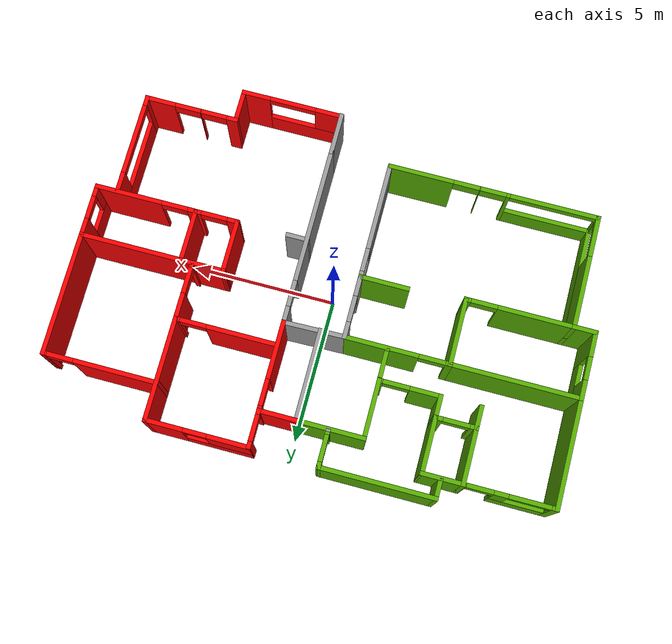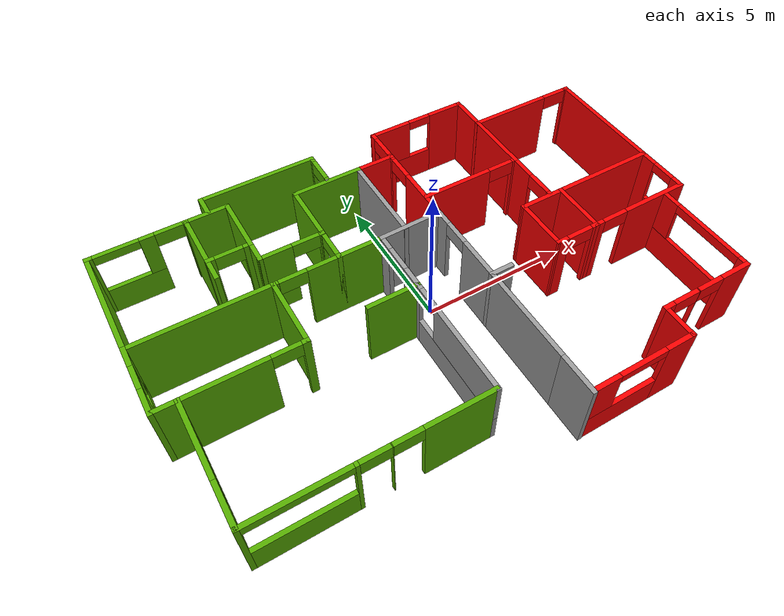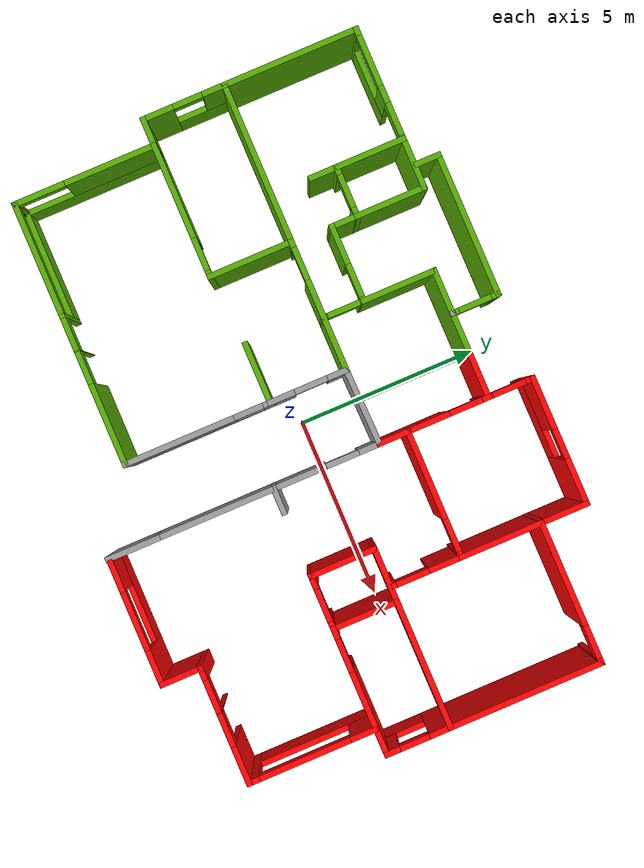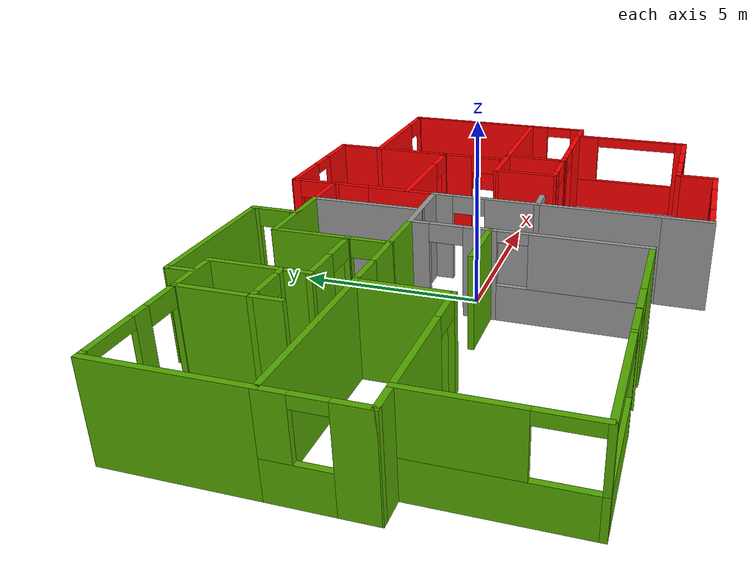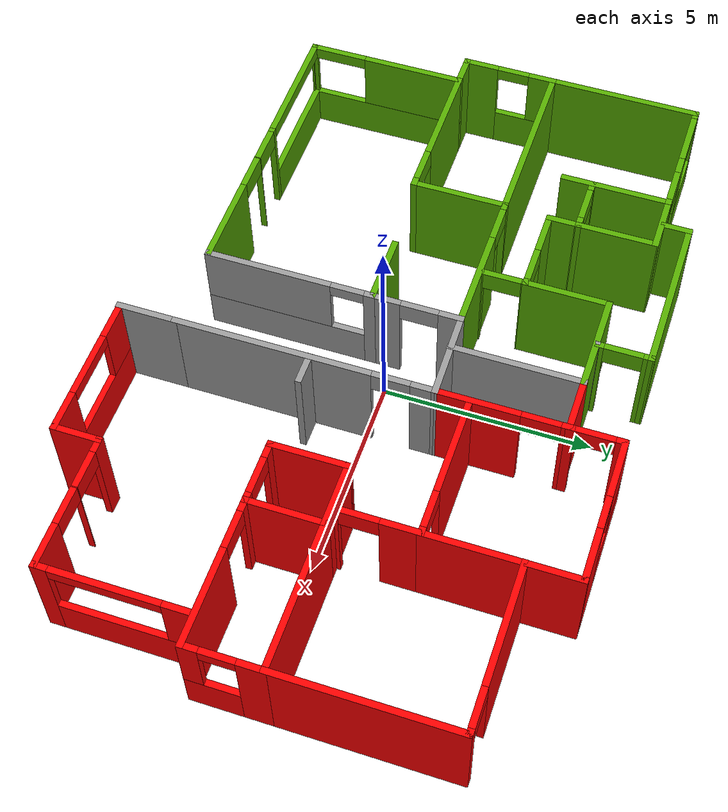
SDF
<?xml version='1.0'?>
<sdf version='1.6'>
  <model name='1floorHouse'>
    <link name='Wall_292'>
      <pose frame=''>-4.3959 -4.53994 0 0 0 -3.14158</pose>
      <self_collide>0</self_collide>
      <kinematic>0</kinematic>
      <visual name='Wall_292_Visual_0'>
        <pose frame=''>-2.52118 0 1.25 0 -0 0</pose>
        <geometry>
          <box>
            <size>2.25743 0.15 2.5</size>
          </box>
        </geometry>
        <material>
          <script>
            <uri>file://media/materials/scripts/gazebo.material</uri>
            <name>Gazebo/Grey</name>
          </script>
          <ambient>0.333333 0.666667 0 1</ambient>
          <diffuse>0.7 0.7 0.7 1</diffuse>
          <specular>0.01 0.01 0.01 1</specular>
          <emissive>0 0 0 1</emissive>
        </material>
        <cast_shadows>1</cast_shadows>
        <transparency>0</transparency>
      </visual>
      <visual name='Wall_292_Visual_1'>
        <pose frame=''>-0.479853 0 1.25 0 -0 0</pose>
        <geometry>
          <box>
            <size>0.025221 0.15 2.5</size>
          </box>
        </geometry>
        <material>
          <script>
            <uri>file://media/materials/scripts/gazebo.material</uri>
            <name>Gazebo/Grey</name>
          </script>
          <ambient>0.333333 0.666667 0 1</ambient>
          <diffuse>0.7 0.7 0.7 1</diffuse>
          <specular>0.01 0.01 0.01 1</specular>
          <emissive>0 0 0 1</emissive>
        </material>
        <cast_shadows>1</cast_shadows>
        <transparency>0</transparency>
      </visual>
      <visual name='Wall_292_Visual_2'>
        <pose frame=''>0.492301 0 1.25 0 -0 0</pose>
        <geometry>
          <box>
            <size>0.119086 0.15 2.5</size>
          </box>
        </geometry>
        <material>
          <script>
            <uri>file://media/materials/scripts/gazebo.material</uri>
            <name>Gazebo/Grey</name>
          </script>
          <ambient>0.333333 0.666667 0 1</ambient>
          <diffuse>0.7 0.7 0.7 1</diffuse>
          <specular>0.01 0.01 0.01 1</specular>
          <emissive>0 0 0 1</emissive>
        </material>
        <cast_shadows>1</cast_shadows>
        <transparency>0</transparency>
      </visual>
      <visual name='Wall_292_Visual_3'>
        <pose frame=''>2.10087 0 0.5 0 -0 0</pose>
        <geometry>
          <box>
            <size>3.09805 0.15 1</size>
          </box>
        </geometry>
        <material>
          <script>
            <uri>file://media/materials/scripts/gazebo.material</uri>
            <name>Gazebo/Grey</name>
          </script>
          <ambient>0.333333 0.666667 0 1</ambient>
          <diffuse>0.7 0.7 0.7 1</diffuse>
          <specular>0.01 0.01 0.01 1</specular>
          <emissive>0 0 0 1</emissive>
        </material>
        <cast_shadows>1</cast_shadows>
        <transparency>0</transparency>
      </visual>
      <visual name='Wall_292_Visual_4'>
        <pose frame=''>3.60087 0 1.75 0 -0 0</pose>
        <geometry>
          <box>
            <size>0.098047 0.15 1.5</size>
          </box>
        </geometry>
        <material>
          <script>
            <uri>file://media/materials/scripts/gazebo.material</uri>
            <name>Gazebo/Grey</name>
          </script>
          <ambient>0.333333 0.666667 0 1</ambient>
          <diffuse>0.7 0.7 0.7 1</diffuse>
          <specular>0.01 0.01 0.01 1</specular>
          <emissive>0 0 0 1</emissive>
        </material>
        <cast_shadows>1</cast_shadows>
        <transparency>0</transparency>
      </visual>
      <visual name='Wall_292_Visual_5'>
        <pose frame=''>-0.942463 0 2.25 0 -0 0</pose>
        <geometry>
          <box>
            <size>0.9 0.15 0.5</size>
          </box>
        </geometry>
        <material>
          <script>
            <uri>file://media/materials/scripts/gazebo.material</uri>
            <name>Gazebo/Grey</name>
          </script>
          <ambient>0.333333 0.666667 0 1</ambient>
          <diffuse>0.7 0.7 0.7 1</diffuse>
          <specular>0.01 0.01 0.01 1</specular>
          <emissive>0 0 0 1</emissive>
        </material>
        <cast_shadows>1</cast_shadows>
        <transparency>0</transparency>
      </visual>
      <visual name='Wall_292_Visual_6'>
        <pose frame=''>-0.017242 0 2.25 0 -0 0</pose>
        <geometry>
          <box>
            <size>0.9 0.15 0.5</size>
          </box>
        </geometry>
        <material>
          <script>
            <uri>file://media/materials/scripts/gazebo.material</uri>
            <name>Gazebo/Grey</name>
          </script>
          <ambient>0.333333 0.666667 0 1</ambient>
          <diffuse>0.7 0.7 0.7 1</diffuse>
          <specular>0.01 0.01 0.01 1</specular>
          <emissive>0 0 0 1</emissive>
        </material>
        <cast_shadows>1</cast_shadows>
        <transparency>0</transparency>
      </visual>
      <visual name='Wall_292_Visual_7'>
        <pose frame=''>2.05184 0 2.35 0 -0 0</pose>
        <geometry>
          <box>
            <size>3 0.15 0.3</size>
          </box>
        </geometry>
        <material>
          <script>
            <uri>file://media/materials/scripts/gazebo.material</uri>
            <name>Gazebo/Grey</name>
          </script>
          <ambient>0.333333 0.666667 0 1</ambient>
          <diffuse>0.7 0.7 0.7 1</diffuse>
          <specular>0.01 0.01 0.01 1</specular>
          <emissive>0 0 0 1</emissive>
        </material>
        <cast_shadows>1</cast_shadows>
        <transparency>0</transparency>
      </visual>
      <collision name='Wall_292_Collision_1'>
        <laser_retro>0</laser_retro>
        <max_contacts>10</max_contacts>
        <pose frame=''>-0.479853 0 1.25 0 -0 0</pose>
        <geometry>
          <box>
            <size>0.025221 0.15 2.5</size>
          </box>
        </geometry>
        <surface>
          <friction>
            <ode>
              <mu>1</mu>
              <mu2>1</mu2>
              <fdir1>0 0 0</fdir1>
              <slip1>0</slip1>
              <slip2>0</slip2>
            </ode>
            <torsional>
              <coefficient>1</coefficient>
              <patch_radius>0</patch_radius>
              <surface_radius>0</surface_radius>
              <use_patch_radius>1</use_patch_radius>
              <ode>
                <slip>0</slip>
              </ode>
            </torsional>
          </friction>
          <bounce>
            <restitution_coefficient>0</restitution_coefficient>
            <threshold>1e+06</threshold>
          </bounce>
          <contact>
            <collide_without_contact>0</collide_without_contact>
            <collide_without_contact_bitmask>1</collide_without_contact_bitmask>
            <collide_bitmask>1</collide_bitmask>
            <ode>
              <soft_cfm>0</soft_cfm>
              <soft_erp>0.2</soft_erp>
              <kp>1e+13</kp>
              <kd>1</kd>
              <max_vel>0.01</max_vel>
              <min_depth>0</min_depth>
            </ode>
            <bullet>
              <split_impulse>1</split_impulse>
              <split_impulse_penetration_threshold>-0.01</split_impulse_penetration_threshold>
              <soft_cfm>0</soft_cfm>
              <soft_erp>0.2</soft_erp>
              <kp>1e+13</kp>
              <kd>1</kd>
            </bullet>
          </contact>
        </surface>
      </collision>
      <collision name='Wall_292_Collision_0'>
        <laser_retro>0</laser_retro>
        <max_contacts>10</max_contacts>
        <pose frame=''>-2.52118 0 1.25 0 -0 0</pose>
        <geometry>
          <box>
            <size>2.25743 0.15 2.5</size>
          </box>
        </geometry>
        <surface>
          <friction>
            <ode>
              <mu>1</mu>
              <mu2>1</mu2>
              <fdir1>0 0 0</fdir1>
              <slip1>0</slip1>
              <slip2>0</slip2>
            </ode>
            <torsional>
              <coefficient>1</coefficient>
              <patch_radius>0</patch_radius>
              <surface_radius>0</surface_radius>
              <use_patch_radius>1</use_patch_radius>
              <ode>
                <slip>0</slip>
              </ode>
            </torsional>
          </friction>
          <bounce>
            <restitution_coefficient>0</restitution_coefficient>
            <threshold>1e+06</threshold>
          </bounce>
          <contact>
            <collide_without_contact>0</collide_without_contact>
            <collide_without_contact_bitmask>1</collide_without_contact_bitmask>
            <collide_bitmask>1</collide_bitmask>
            <ode>
              <soft_cfm>0</soft_cfm>
              <soft_erp>0.2</soft_erp>
              <kp>1e+13</kp>
              <kd>1</kd>
              <max_vel>0.01</max_vel>
              <min_depth>0</min_depth>
            </ode>
            <bullet>
              <split_impulse>1</split_impulse>
              <split_impulse_penetration_threshold>-0.01</split_impulse_penetration_threshold>
              <soft_cfm>0</soft_cfm>
              <soft_erp>0.2</soft_erp>
              <kp>1e+13</kp>
              <kd>1</kd>
            </bullet>
          </contact>
        </surface>
      </collision>
      <collision name='Wall_292_Collision_2'>
        <laser_retro>0</laser_retro>
        <max_contacts>10</max_contacts>
        <pose frame=''>0.492301 0 1.25 0 -0 0</pose>
        <geometry>
          <box>
            <size>0.119086 0.15 2.5</size>
          </box>
        </geometry>
        <surface>
          <friction>
            <ode>
              <mu>1</mu>
              <mu2>1</mu2>
              <fdir1>0 0 0</fdir1>
              <slip1>0</slip1>
              <slip2>0</slip2>
            </ode>
            <torsional>
              <coefficient>1</coefficient>
              <patch_radius>0</patch_radius>
              <surface_radius>0</surface_radius>
              <use_patch_radius>1</use_patch_radius>
              <ode>
                <slip>0</slip>
              </ode>
            </torsional>
          </friction>
          <bounce>
            <restitution_coefficient>0</restitution_coefficient>
            <threshold>1e+06</threshold>
          </bounce>
          <contact>
            <collide_without_contact>0</collide_without_contact>
            <collide_without_contact_bitmask>1</collide_without_contact_bitmask>
            <collide_bitmask>1</collide_bitmask>
            <ode>
              <soft_cfm>0</soft_cfm>
              <soft_erp>0.2</soft_erp>
              <kp>1e+13</kp>
              <kd>1</kd>
              <max_vel>0.01</max_vel>
              <min_depth>0</min_depth>
            </ode>
            <bullet>
              <split_impulse>1</split_impulse>
              <split_impulse_penetration_threshold>-0.01</split_impulse_penetration_threshold>
              <soft_cfm>0</soft_cfm>
              <soft_erp>0.2</soft_erp>
              <kp>1e+13</kp>
              <kd>1</kd>
            </bullet>
          </contact>
        </surface>
      </collision>
      <collision name='Wall_292_Collision_3'>
        <laser_retro>0</laser_retro>
        <max_contacts>10</max_contacts>
        <pose frame=''>2.10087 0 0.5 0 -0 0</pose>
        <geometry>
          <box>
            <size>3.09805 0.15 1</size>
          </box>
        </geometry>
        <surface>
          <friction>
            <ode>
              <mu>1</mu>
              <mu2>1</mu2>
              <fdir1>0 0 0</fdir1>
              <slip1>0</slip1>
              <slip2>0</slip2>
            </ode>
            <torsional>
              <coefficient>1</coefficient>
              <patch_radius>0</patch_radius>
              <surface_radius>0</surface_radius>
              <use_patch_radius>1</use_patch_radius>
              <ode>
                <slip>0</slip>
              </ode>
            </torsional>
          </friction>
          <bounce>
            <restitution_coefficient>0</restitution_coefficient>
            <threshold>1e+06</threshold>
          </bounce>
          <contact>
            <collide_without_contact>0</collide_without_contact>
            <collide_without_contact_bitmask>1</collide_without_contact_bitmask>
            <collide_bitmask>1</collide_bitmask>
            <ode>
              <soft_cfm>0</soft_cfm>
              <soft_erp>0.2</soft_erp>
              <kp>1e+13</kp>
              <kd>1</kd>
              <max_vel>0.01</max_vel>
              <min_depth>0</min_depth>
            </ode>
            <bullet>
              <split_impulse>1</split_impulse>
              <split_impulse_penetration_threshold>-0.01</split_impulse_penetration_threshold>
              <soft_cfm>0</soft_cfm>
              <soft_erp>0.2</soft_erp>
              <kp>1e+13</kp>
              <kd>1</kd>
            </bullet>
          </contact>
        </surface>
      </collision>
      <collision name='Wall_292_Collision_4'>
        <laser_retro>0</laser_retro>
        <max_contacts>10</max_contacts>
        <pose frame=''>3.60087 0 1.75 0 -0 0</pose>
        <geometry>
          <box>
            <size>0.098047 0.15 1.5</size>
          </box>
        </geometry>
        <surface>
          <friction>
            <ode>
              <mu>1</mu>
              <mu2>1</mu2>
              <fdir1>0 0 0</fdir1>
              <slip1>0</slip1>
              <slip2>0</slip2>
            </ode>
            <torsional>
              <coefficient>1</coefficient>
              <patch_radius>0</patch_radius>
              <surface_radius>0</surface_radius>
              <use_patch_radius>1</use_patch_radius>
              <ode>
                <slip>0</slip>
              </ode>
            </torsional>
          </friction>
          <bounce>
            <restitution_coefficient>0</restitution_coefficient>
            <threshold>1e+06</threshold>
          </bounce>
          <contact>
            <collide_without_contact>0</collide_without_contact>
            <collide_without_contact_bitmask>1</collide_without_contact_bitmask>
            <collide_bitmask>1</collide_bitmask>
            <ode>
              <soft_cfm>0</soft_cfm>
              <soft_erp>0.2</soft_erp>
              <kp>1e+13</kp>
              <kd>1</kd>
              <max_vel>0.01</max_vel>
              <min_depth>0</min_depth>
            </ode>
            <bullet>
              <split_impulse>1</split_impulse>
              <split_impulse_penetration_threshold>-0.01</split_impulse_penetration_threshold>
              <soft_cfm>0</soft_cfm>
              <soft_erp>0.2</soft_erp>
              <kp>1e+13</kp>
              <kd>1</kd>
            </bullet>
          </contact>
        </surface>
      </collision>
      <collision name='Wall_292_Collision_5'>
        <laser_retro>0</laser_retro>
        <max_contacts>10</max_contacts>
        <pose frame=''>-0.942463 0 2.25 0 -0 0</pose>
        <geometry>
          <box>
            <size>0.9 0.15 0.5</size>
          </box>
        </geometry>
        <surface>
          <friction>
            <ode>
              <mu>1</mu>
              <mu2>1</mu2>
              <fdir1>0 0 0</fdir1>
              <slip1>0</slip1>
              <slip2>0</slip2>
            </ode>
            <torsional>
              <coefficient>1</coefficient>
              <patch_radius>0</patch_radius>
              <surface_radius>0</surface_radius>
              <use_patch_radius>1</use_patch_radius>
              <ode>
                <slip>0</slip>
              </ode>
            </torsional>
          </friction>
          <bounce>
            <restitution_coefficient>0</restitution_coefficient>
            <threshold>1e+06</threshold>
          </bounce>
          <contact>
            <collide_without_contact>0</collide_without_contact>
            <collide_without_contact_bitmask>1</collide_without_contact_bitmask>
            <collide_bitmask>1</collide_bitmask>
            <ode>
              <soft_cfm>0</soft_cfm>
              <soft_erp>0.2</soft_erp>
              <kp>1e+13</kp>
              <kd>1</kd>
              <max_vel>0.01</max_vel>
              <min_depth>0</min_depth>
            </ode>
            <bullet>
              <split_impulse>1</split_impulse>
              <split_impulse_penetration_threshold>-0.01</split_impulse_penetration_threshold>
              <soft_cfm>0</soft_cfm>
              <soft_erp>0.2</soft_erp>
              <kp>1e+13</kp>
              <kd>1</kd>
            </bullet>
          </contact>
        </surface>
      </collision>
      <collision name='Wall_292_Collision_7'>
        <laser_retro>0</laser_retro>
        <max_contacts>10</max_contacts>
        <pose frame=''>2.05184 0 2.35 0 -0 0</pose>
        <geometry>
          <box>
            <size>3 0.15 0.3</size>
          </box>
        </geometry>
        <surface>
          <friction>
            <ode>
              <mu>1</mu>
              <mu2>1</mu2>
              <fdir1>0 0 0</fdir1>
              <slip1>0</slip1>
              <slip2>0</slip2>
            </ode>
            <torsional>
              <coefficient>1</coefficient>
              <patch_radius>0</patch_radius>
              <surface_radius>0</surface_radius>
              <use_patch_radius>1</use_patch_radius>
              <ode>
                <slip>0</slip>
              </ode>
            </torsional>
          </friction>
          <bounce>
            <restitution_coefficient>0</restitution_coefficient>
            <threshold>1e+06</threshold>
          </bounce>
          <contact>
            <collide_without_contact>0</collide_without_contact>
            <collide_without_contact_bitmask>1</collide_without_contact_bitmask>
            <collide_bitmask>1</collide_bitmask>
            <ode>
              <soft_cfm>0</soft_cfm>
              <soft_erp>0.2</soft_erp>
              <kp>1e+13</kp>
              <kd>1</kd>
              <max_vel>0.01</max_vel>
              <min_depth>0</min_depth>
            </ode>
            <bullet>
              <split_impulse>1</split_impulse>
              <split_impulse_penetration_threshold>-0.01</split_impulse_penetration_threshold>
              <soft_cfm>0</soft_cfm>
              <soft_erp>0.2</soft_erp>
              <kp>1e+13</kp>
              <kd>1</kd>
            </bullet>
          </contact>
        </surface>
      </collision>
      <collision name='Wall_292_Collision_6'>
        <laser_retro>0</laser_retro>
        <max_contacts>10</max_contacts>
        <pose frame=''>-0.017242 0 2.25 0 -0 0</pose>
        <geometry>
          <box>
            <size>0.9 0.15 0.5</size>
          </box>
        </geometry>
        <surface>
          <friction>
            <ode>
              <mu>1</mu>
              <mu2>1</mu2>
              <fdir1>0 0 0</fdir1>
              <slip1>0</slip1>
              <slip2>0</slip2>
            </ode>
            <torsional>
              <coefficient>1</coefficient>
              <patch_radius>0</patch_radius>
              <surface_radius>0</surface_radius>
              <use_patch_radius>1</use_patch_radius>
              <ode>
                <slip>0</slip>
              </ode>
            </torsional>
          </friction>
          <bounce>
            <restitution_coefficient>0</restitution_coefficient>
            <threshold>1e+06</threshold>
          </bounce>
          <contact>
            <collide_without_contact>0</collide_without_contact>
            <collide_without_contact_bitmask>1</collide_without_contact_bitmask>
            <collide_bitmask>1</collide_bitmask>
            <ode>
              <soft_cfm>0</soft_cfm>
              <soft_erp>0.2</soft_erp>
              <kp>1e+13</kp>
              <kd>1</kd>
              <max_vel>0.01</max_vel>
              <min_depth>0</min_depth>
            </ode>
            <bullet>
              <split_impulse>1</split_impulse>
              <split_impulse_penetration_threshold>-0.01</split_impulse_penetration_threshold>
              <soft_cfm>0</soft_cfm>
              <soft_erp>0.2</soft_erp>
              <kp>1e+13</kp>
              <kd>1</kd>
            </bullet>
          </contact>
        </surface>
      </collision>
    </link>
    <link name='Wall_293'>
      <pose frame=''>-7.97079 -2.615 0.0 0 -0 1.5708</pose>
      <self_collide>0</self_collide>
      <kinematic>0</kinematic>
      <visual name='Wall_293_Visual_0'>
        <pose frame=''>-1.97712 0 1.25 0 -0 0</pose>
        <geometry>
          <box>
            <size>0.045764 0.15 2.5</size>
          </box>
        </geometry>
        <material>
          <script>
            <uri>file://media/materials/scripts/gazebo.material</uri>
            <name>Gazebo/Grey</name>
          </script>
          <ambient>0.333333 0.666667 0 1</ambient>
          <diffuse>0.7 0.7 0.7 1</diffuse>
          <specular>0.01 0.01 0.01 1</specular>
          <emissive>0 0 0 1</emissive>
        </material>
        <cast_shadows>1</cast_shadows>
        <transparency>0</transparency>
      </visual>
      <visual name='Wall_293_Visual_1'>
        <pose frame=''>0.022882 0 0.5 0 -0 0</pose>
        <geometry>
          <box>
            <size>3.95424 0.15 1</size>
          </box>
        </geometry>
        <material>
          <script>
            <uri>file://media/materials/scripts/gazebo.material</uri>
            <name>Gazebo/Grey</name>
          </script>
          <ambient>0.333333 0.666667 0 1</ambient>
          <diffuse>0.7 0.7 0.7 1</diffuse>
          <specular>0.01 0.01 0.01 1</specular>
          <emissive>0 0 0 1</emissive>
        </material>
        <cast_shadows>1</cast_shadows>
        <transparency>0</transparency>
      </visual>
      <visual name='Wall_293_Visual_2'>
        <pose frame=''>0.722882 0 1.75 0 -0 0</pose>
        <geometry>
          <box>
            <size>2.55424 0.15 1.5</size>
          </box>
        </geometry>
        <material>
          <script>
            <uri>file://media/materials/scripts/gazebo.material</uri>
            <name>Gazebo/Grey</name>
          </script>
          <ambient>0.333333 0.666667 0 1</ambient>
          <diffuse>0.7 0.7 0.7 1</diffuse>
          <specular>0.01 0.01 0.01 1</specular>
          <emissive>0 0 0 1</emissive>
        </material>
        <cast_shadows>1</cast_shadows>
        <transparency>0</transparency>
      </visual>
      <visual name='Wall_293_Visual_3'>
        <pose frame=''>-1.25424 0 2.35 0 -0 0</pose>
        <geometry>
          <box>
            <size>1.4 0.15 0.3</size>
          </box>
        </geometry>
        <material>
          <script>
            <uri>file://media/materials/scripts/gazebo.material</uri>
            <name>Gazebo/Grey</name>
          </script>
          <ambient>0.333333 0.666667 0 1</ambient>
          <diffuse>0.7 0.7 0.7 1</diffuse>
          <specular>0.01 0.01 0.01 1</specular>
          <emissive>0 0 0 1</emissive>
        </material>
        <cast_shadows>1</cast_shadows>
        <transparency>0</transparency>
      </visual>
      <collision name='Wall_293_Collision_0'>
        <laser_retro>0</laser_retro>
        <max_contacts>10</max_contacts>
        <pose frame=''>-1.97712 0 1.25 0 -0 0</pose>
        <geometry>
          <box>
            <size>0.045764 0.15 2.5</size>
          </box>
        </geometry>
        <surface>
          <friction>
            <ode>
              <mu>1</mu>
              <mu2>1</mu2>
              <fdir1>0 0 0</fdir1>
              <slip1>0</slip1>
              <slip2>0</slip2>
            </ode>
            <torsional>
              <coefficient>1</coefficient>
              <patch_radius>0</patch_radius>
              <surface_radius>0</surface_radius>
              <use_patch_radius>1</use_patch_radius>
              <ode>
                <slip>0</slip>
              </ode>
            </torsional>
          </friction>
          <bounce>
            <restitution_coefficient>0</restitution_coefficient>
            <threshold>1e+06</threshold>
          </bounce>
          <contact>
            <collide_without_contact>0</collide_without_contact>
            <collide_without_contact_bitmask>1</collide_without_contact_bitmask>
            <collide_bitmask>1</collide_bitmask>
            <ode>
              <soft_cfm>0</soft_cfm>
              <soft_erp>0.2</soft_erp>
              <kp>1e+13</kp>
              <kd>1</kd>
              <max_vel>0.01</max_vel>
              <min_depth>0</min_depth>
            </ode>
            <bullet>
              <split_impulse>1</split_impulse>
              <split_impulse_penetration_threshold>-0.01</split_impulse_penetration_threshold>
              <soft_cfm>0</soft_cfm>
              <soft_erp>0.2</soft_erp>
              <kp>1e+13</kp>
              <kd>1</kd>
            </bullet>
          </contact>
        </surface>
      </collision>
      <collision name='Wall_293_Collision_1'>
        <laser_retro>0</laser_retro>
        <max_contacts>10</max_contacts>
        <pose frame=''>0.022882 0 0.5 0 -0 0</pose>
        <geometry>
          <box>
            <size>3.95424 0.15 1</size>
          </box>
        </geometry>
        <surface>
          <friction>
            <ode>
              <mu>1</mu>
              <mu2>1</mu2>
              <fdir1>0 0 0</fdir1>
              <slip1>0</slip1>
              <slip2>0</slip2>
            </ode>
            <torsional>
              <coefficient>1</coefficient>
              <patch_radius>0</patch_radius>
              <surface_radius>0</surface_radius>
              <use_patch_radius>1</use_patch_radius>
              <ode>
                <slip>0</slip>
              </ode>
            </torsional>
          </friction>
          <bounce>
            <restitution_coefficient>0</restitution_coefficient>
            <threshold>1e+06</threshold>
          </bounce>
          <contact>
            <collide_without_contact>0</collide_without_contact>
            <collide_without_contact_bitmask>1</collide_without_contact_bitmask>
            <collide_bitmask>1</collide_bitmask>
            <ode>
              <soft_cfm>0</soft_cfm>
              <soft_erp>0.2</soft_erp>
              <kp>1e+13</kp>
              <kd>1</kd>
              <max_vel>0.01</max_vel>
              <min_depth>0</min_depth>
            </ode>
            <bullet>
              <split_impulse>1</split_impulse>
              <split_impulse_penetration_threshold>-0.01</split_impulse_penetration_threshold>
              <soft_cfm>0</soft_cfm>
              <soft_erp>0.2</soft_erp>
              <kp>1e+13</kp>
              <kd>1</kd>
            </bullet>
          </contact>
        </surface>
      </collision>
      <collision name='Wall_293_Collision_2'>
        <laser_retro>0</laser_retro>
        <max_contacts>10</max_contacts>
        <pose frame=''>0.722882 0 1.75 0 -0 0</pose>
        <geometry>
          <box>
            <size>2.55424 0.15 1.5</size>
          </box>
        </geometry>
        <surface>
          <friction>
            <ode>
              <mu>1</mu>
              <mu2>1</mu2>
              <fdir1>0 0 0</fdir1>
              <slip1>0</slip1>
              <slip2>0</slip2>
            </ode>
            <torsional>
              <coefficient>1</coefficient>
              <patch_radius>0</patch_radius>
              <surface_radius>0</surface_radius>
              <use_patch_radius>1</use_patch_radius>
              <ode>
                <slip>0</slip>
              </ode>
            </torsional>
          </friction>
          <bounce>
            <restitution_coefficient>0</restitution_coefficient>
            <threshold>1e+06</threshold>
          </bounce>
          <contact>
            <collide_without_contact>0</collide_without_contact>
            <collide_without_contact_bitmask>1</collide_without_contact_bitmask>
            <collide_bitmask>1</collide_bitmask>
            <ode>
              <soft_cfm>0</soft_cfm>
              <soft_erp>0.2</soft_erp>
              <kp>1e+13</kp>
              <kd>1</kd>
              <max_vel>0.01</max_vel>
              <min_depth>0</min_depth>
            </ode>
            <bullet>
              <split_impulse>1</split_impulse>
              <split_impulse_penetration_threshold>-0.01</split_impulse_penetration_threshold>
              <soft_cfm>0</soft_cfm>
              <soft_erp>0.2</soft_erp>
              <kp>1e+13</kp>
              <kd>1</kd>
            </bullet>
          </contact>
        </surface>
      </collision>
      <collision name='Wall_293_Collision_3'>
        <laser_retro>0</laser_retro>
        <max_contacts>10</max_contacts>
        <pose frame=''>-1.25424 0 2.35 0 -0 0</pose>
        <geometry>
          <box>
            <size>1.4 0.15 0.3</size>
          </box>
        </geometry>
        <surface>
          <friction>
            <ode>
              <mu>1</mu>
              <mu2>1</mu2>
              <fdir1>0 0 0</fdir1>
              <slip1>0</slip1>
              <slip2>0</slip2>
            </ode>
            <torsional>
              <coefficient>1</coefficient>
              <patch_radius>0</patch_radius>
              <surface_radius>0</surface_radius>
              <use_patch_radius>1</use_patch_radius>
              <ode>
                <slip>0</slip>
              </ode>
            </torsional>
          </friction>
          <bounce>
            <restitution_coefficient>0</restitution_coefficient>
            <threshold>1e+06</threshold>
          </bounce>
          <contact>
            <collide_without_contact>0</collide_without_contact>
            <collide_without_contact_bitmask>1</collide_without_contact_bitmask>
            <collide_bitmask>1</collide_bitmask>
            <ode>
              <soft_cfm>0</soft_cfm>
              <soft_erp>0.2</soft_erp>
              <kp>1e+13</kp>
              <kd>1</kd>
              <max_vel>0.01</max_vel>
              <min_depth>0</min_depth>
            </ode>
            <bullet>
              <split_impulse>1</split_impulse>
              <split_impulse_penetration_threshold>-0.01</split_impulse_penetration_threshold>
              <soft_cfm>0</soft_cfm>
              <soft_erp>0.2</soft_erp>
              <kp>1e+13</kp>
              <kd>1</kd>
            </bullet>
          </contact>
        </surface>
      </collision>
    </link>
    <link name='Wall_294'>
      <pose frame=''>-8.3305 -0.690004 0.0 0 -0 3.14159</pose>
      <self_collide>0</self_collide>
      <kinematic>0</kinematic>
      <visual name='Wall_294_Visual'>
        <pose frame=''>0 0 1.25 0 -0 0</pose>
        <geometry>
          <box>
            <size>0.86941 0.15 2.5</size>
          </box>
        </geometry>
        <material>
          <script>
            <uri>file://media/materials/scripts/gazebo.material</uri>
            <name>Gazebo/Grey</name>
          </script>
          <ambient>0.333333 0.666667 0 1</ambient>
          <diffuse>0.7 0.7 0.7 1</diffuse>
          <specular>0.01 0.01 0.01 1</specular>
          <emissive>0 0 0 1</emissive>
        </material>
        <cast_shadows>1</cast_shadows>
        <transparency>0</transparency>
      </visual>
      <collision name='Wall_294_Collision'>
        <laser_retro>0</laser_retro>
        <max_contacts>10</max_contacts>
        <pose frame=''>0 0 1.25 0 -0 0</pose>
        <geometry>
          <box>
            <size>0.86941 0.15 2.5</size>
          </box>
        </geometry>
        <surface>
          <friction>
            <ode>
              <mu>1</mu>
              <mu2>1</mu2>
              <fdir1>0 0 0</fdir1>
              <slip1>0</slip1>
              <slip2>0</slip2>
            </ode>
            <torsional>
              <coefficient>1</coefficient>
              <patch_radius>0</patch_radius>
              <surface_radius>0</surface_radius>
              <use_patch_radius>1</use_patch_radius>
              <ode>
                <slip>0</slip>
              </ode>
            </torsional>
          </friction>
          <bounce>
            <restitution_coefficient>0</restitution_coefficient>
            <threshold>1e+06</threshold>
          </bounce>
          <contact>
            <collide_without_contact>0</collide_without_contact>
            <collide_without_contact_bitmask>1</collide_without_contact_bitmask>
            <collide_bitmask>1</collide_bitmask>
            <ode>
              <soft_cfm>0</soft_cfm>
              <soft_erp>0.2</soft_erp>
              <kp>1e+13</kp>
              <kd>1</kd>
              <max_vel>0.01</max_vel>
              <min_depth>0</min_depth>
            </ode>
            <bullet>
              <split_impulse>1</split_impulse>
              <split_impulse_penetration_threshold>-0.01</split_impulse_penetration_threshold>
              <soft_cfm>0</soft_cfm>
              <soft_erp>0.2</soft_erp>
              <kp>1e+13</kp>
              <kd>1</kd>
            </bullet>
          </contact>
        </surface>
      </collision>
    </link>
    <link name='Wall_295'>
      <pose frame=''>-8.69021 0.434996 0.0 0 -0 1.5708</pose>
      <self_collide>0</self_collide>
      <kinematic>0</kinematic>
      <visual name='Wall_295_Visual_0'>
        <pose frame=''>-0.748437 0 1.25 0 -0 0</pose>
        <geometry>
          <box>
            <size>0.903127 0.15 2.5</size>
          </box>
        </geometry>
        <material>
          <script>
            <uri>file://media/materials/scripts/gazebo.material</uri>
            <name>Gazebo/Grey</name>
          </script>
          <ambient>0.333333 0.666667 0 1</ambient>
          <diffuse>0.7 0.7 0.7 1</diffuse>
          <specular>0.01 0.01 0.01 1</specular>
          <emissive>0 0 0 1</emissive>
        </material>
        <cast_shadows>1</cast_shadows>
        <transparency>0</transparency>
      </visual>
      <visual name='Wall_295_Visual_1'>
        <pose frame=''>0.451563 0 0.5 0 -0 0</pose>
        <geometry>
          <box>
            <size>1.49687 0.15 1</size>
          </box>
        </geometry>
        <material>
          <script>
            <uri>file://media/materials/scripts/gazebo.material</uri>
            <name>Gazebo/Grey</name>
          </script>
          <ambient>0.333333 0.666667 0 1</ambient>
          <diffuse>0.7 0.7 0.7 1</diffuse>
          <specular>0.01 0.01 0.01 1</specular>
          <emissive>0 0 0 1</emissive>
        </material>
        <cast_shadows>1</cast_shadows>
        <transparency>0</transparency>
      </visual>
      <visual name='Wall_295_Visual_2'>
        <pose frame=''>0.851563 0 1.75 0 -0 0</pose>
        <geometry>
          <box>
            <size>0.696873 0.15 1.5</size>
          </box>
        </geometry>
        <material>
          <script>
            <uri>file://media/materials/scripts/gazebo.material</uri>
            <name>Gazebo/Grey</name>
          </script>
          <ambient>0.333333 0.666667 0 1</ambient>
          <diffuse>0.7 0.7 0.7 1</diffuse>
          <specular>0.01 0.01 0.01 1</specular>
          <emissive>0 0 0 1</emissive>
        </material>
        <cast_shadows>1</cast_shadows>
        <transparency>0</transparency>
      </visual>
      <visual name='Wall_295_Visual_3'>
        <pose frame=''>0.103127 0 2.35 0 -0 0</pose>
        <geometry>
          <box>
            <size>0.8 0.15 0.3</size>
          </box>
        </geometry>
        <material>
          <script>
            <uri>file://media/materials/scripts/gazebo.material</uri>
            <name>Gazebo/Grey</name>
          </script>
          <ambient>0.333333 0.666667 0 1</ambient>
          <diffuse>0.7 0.7 0.7 1</diffuse>
          <specular>0.01 0.01 0.01 1</specular>
          <emissive>0 0 0 1</emissive>
        </material>
        <cast_shadows>1</cast_shadows>
        <transparency>0</transparency>
      </visual>
      <collision name='Wall_295_Collision_0'>
        <laser_retro>0</laser_retro>
        <max_contacts>10</max_contacts>
        <pose frame=''>-0.748437 0 1.25 0 -0 0</pose>
        <geometry>
          <box>
            <size>0.903127 0.15 2.5</size>
          </box>
        </geometry>
        <surface>
          <friction>
            <ode>
              <mu>1</mu>
              <mu2>1</mu2>
              <fdir1>0 0 0</fdir1>
              <slip1>0</slip1>
              <slip2>0</slip2>
            </ode>
            <torsional>
              <coefficient>1</coefficient>
              <patch_radius>0</patch_radius>
              <surface_radius>0</surface_radius>
              <use_patch_radius>1</use_patch_radius>
              <ode>
                <slip>0</slip>
              </ode>
            </torsional>
          </friction>
          <bounce>
            <restitution_coefficient>0</restitution_coefficient>
            <threshold>1e+06</threshold>
          </bounce>
          <contact>
            <collide_without_contact>0</collide_without_contact>
            <collide_without_contact_bitmask>1</collide_without_contact_bitmask>
            <collide_bitmask>1</collide_bitmask>
            <ode>
              <soft_cfm>0</soft_cfm>
              <soft_erp>0.2</soft_erp>
              <kp>1e+13</kp>
              <kd>1</kd>
              <max_vel>0.01</max_vel>
              <min_depth>0</min_depth>
            </ode>
            <bullet>
              <split_impulse>1</split_impulse>
              <split_impulse_penetration_threshold>-0.01</split_impulse_penetration_threshold>
              <soft_cfm>0</soft_cfm>
              <soft_erp>0.2</soft_erp>
              <kp>1e+13</kp>
              <kd>1</kd>
            </bullet>
          </contact>
        </surface>
      </collision>
      <collision name='Wall_295_Collision_1'>
        <laser_retro>0</laser_retro>
        <max_contacts>10</max_contacts>
        <pose frame=''>0.451563 0 0.5 0 -0 0</pose>
        <geometry>
          <box>
            <size>1.49687 0.15 1</size>
          </box>
        </geometry>
        <surface>
          <friction>
            <ode>
              <mu>1</mu>
              <mu2>1</mu2>
              <fdir1>0 0 0</fdir1>
              <slip1>0</slip1>
              <slip2>0</slip2>
            </ode>
            <torsional>
              <coefficient>1</coefficient>
              <patch_radius>0</patch_radius>
              <surface_radius>0</surface_radius>
              <use_patch_radius>1</use_patch_radius>
              <ode>
                <slip>0</slip>
              </ode>
            </torsional>
          </friction>
          <bounce>
            <restitution_coefficient>0</restitution_coefficient>
            <threshold>1e+06</threshold>
          </bounce>
          <contact>
            <collide_without_contact>0</collide_without_contact>
            <collide_without_contact_bitmask>1</collide_without_contact_bitmask>
            <collide_bitmask>1</collide_bitmask>
            <ode>
              <soft_cfm>0</soft_cfm>
              <soft_erp>0.2</soft_erp>
              <kp>1e+13</kp>
              <kd>1</kd>
              <max_vel>0.01</max_vel>
              <min_depth>0</min_depth>
            </ode>
            <bullet>
              <split_impulse>1</split_impulse>
              <split_impulse_penetration_threshold>-0.01</split_impulse_penetration_threshold>
              <soft_cfm>0</soft_cfm>
              <soft_erp>0.2</soft_erp>
              <kp>1e+13</kp>
              <kd>1</kd>
            </bullet>
          </contact>
        </surface>
      </collision>
      <collision name='Wall_295_Collision_2'>
        <laser_retro>0</laser_retro>
        <max_contacts>10</max_contacts>
        <pose frame=''>0.851563 0 1.75 0 -0 0</pose>
        <geometry>
          <box>
            <size>0.696873 0.15 1.5</size>
          </box>
        </geometry>
        <surface>
          <friction>
            <ode>
              <mu>1</mu>
              <mu2>1</mu2>
              <fdir1>0 0 0</fdir1>
              <slip1>0</slip1>
              <slip2>0</slip2>
            </ode>
            <torsional>
              <coefficient>1</coefficient>
              <patch_radius>0</patch_radius>
              <surface_radius>0</surface_radius>
              <use_patch_radius>1</use_patch_radius>
              <ode>
                <slip>0</slip>
              </ode>
            </torsional>
          </friction>
          <bounce>
            <restitution_coefficient>0</restitution_coefficient>
            <threshold>1e+06</threshold>
          </bounce>
          <contact>
            <collide_without_contact>0</collide_without_contact>
            <collide_without_contact_bitmask>1</collide_without_contact_bitmask>
            <collide_bitmask>1</collide_bitmask>
            <ode>
              <soft_cfm>0</soft_cfm>
              <soft_erp>0.2</soft_erp>
              <kp>1e+13</kp>
              <kd>1</kd>
              <max_vel>0.01</max_vel>
              <min_depth>0</min_depth>
            </ode>
            <bullet>
              <split_impulse>1</split_impulse>
              <split_impulse_penetration_threshold>-0.01</split_impulse_penetration_threshold>
              <soft_cfm>0</soft_cfm>
              <soft_erp>0.2</soft_erp>
              <kp>1e+13</kp>
              <kd>1</kd>
            </bullet>
          </contact>
        </surface>
      </collision>
      <collision name='Wall_295_Collision_3'>
        <laser_retro>0</laser_retro>
        <max_contacts>10</max_contacts>
        <pose frame=''>0.103127 0 2.35 0 -0 0</pose>
        <geometry>
          <box>
            <size>0.8 0.15 0.3</size>
          </box>
        </geometry>
        <surface>
          <friction>
            <ode>
              <mu>1</mu>
              <mu2>1</mu2>
              <fdir1>0 0 0</fdir1>
              <slip1>0</slip1>
              <slip2>0</slip2>
            </ode>
            <torsional>
              <coefficient>1</coefficient>
              <patch_radius>0</patch_radius>
              <surface_radius>0</surface_radius>
              <use_patch_radius>1</use_patch_radius>
              <ode>
                <slip>0</slip>
              </ode>
            </torsional>
          </friction>
          <bounce>
            <restitution_coefficient>0</restitution_coefficient>
            <threshold>1e+06</threshold>
          </bounce>
          <contact>
            <collide_without_contact>0</collide_without_contact>
            <collide_without_contact_bitmask>1</collide_without_contact_bitmask>
            <collide_bitmask>1</collide_bitmask>
            <ode>
              <soft_cfm>0</soft_cfm>
              <soft_erp>0.2</soft_erp>
              <kp>1e+13</kp>
              <kd>1</kd>
              <max_vel>0.01</max_vel>
              <min_depth>0</min_depth>
            </ode>
            <bullet>
              <split_impulse>1</split_impulse>
              <split_impulse_penetration_threshold>-0.01</split_impulse_penetration_threshold>
              <soft_cfm>0</soft_cfm>
              <soft_erp>0.2</soft_erp>
              <kp>1e+13</kp>
              <kd>1</kd>
            </bullet>
          </contact>
        </surface>
      </collision>
    </link>
    <link name='Wall_296'>
      <pose frame=''>-6.5152 1.56 0.0 0 -0 0</pose>
      <self_collide>0</self_collide>
      <kinematic>0</kinematic>
      <visual name='Wall_296_Visual'>
        <pose frame=''>0 0 1.25 0 -0 0</pose>
        <geometry>
          <box>
            <size>4.5 0.15 2.5</size>
          </box>
        </geometry>
        <material>
          <script>
            <uri>file://media/materials/scripts/gazebo.material</uri>
            <name>Gazebo/Grey</name>
          </script>
          <ambient>0.333333 0.666667 0 1</ambient>
          <diffuse>0.7 0.7 0.7 1</diffuse>
          <specular>0.01 0.01 0.01 1</specular>
          <emissive>0 0 0 1</emissive>
        </material>
        <cast_shadows>1</cast_shadows>
        <transparency>0</transparency>
      </visual>
      <collision name='Wall_296_Collision'>
        <laser_retro>0</laser_retro>
        <max_contacts>10</max_contacts>
        <pose frame=''>0 0 1.25 0 -0 0</pose>
        <geometry>
          <box>
            <size>4.5 0.15 2.5</size>
          </box>
        </geometry>
        <surface>
          <friction>
            <ode>
              <mu>1</mu>
              <mu2>1</mu2>
              <fdir1>0 0 0</fdir1>
              <slip1>0</slip1>
              <slip2>0</slip2>
            </ode>
            <torsional>
              <coefficient>1</coefficient>
              <patch_radius>0</patch_radius>
              <surface_radius>0</surface_radius>
              <use_patch_radius>1</use_patch_radius>
              <ode>
                <slip>0</slip>
              </ode>
            </torsional>
          </friction>
          <bounce>
            <restitution_coefficient>0</restitution_coefficient>
            <threshold>1e+06</threshold>
          </bounce>
          <contact>
            <collide_without_contact>0</collide_without_contact>
            <collide_without_contact_bitmask>1</collide_without_contact_bitmask>
            <collide_bitmask>1</collide_bitmask>
            <ode>
              <soft_cfm>0</soft_cfm>
              <soft_erp>0.2</soft_erp>
              <kp>1e+13</kp>
              <kd>1</kd>
              <max_vel>0.01</max_vel>
              <min_depth>0</min_depth>
            </ode>
            <bullet>
              <split_impulse>1</split_impulse>
              <split_impulse_penetration_threshold>-0.01</split_impulse_penetration_threshold>
              <soft_cfm>0</soft_cfm>
              <soft_erp>0.2</soft_erp>
              <kp>1e+13</kp>
              <kd>1</kd>
            </bullet>
          </contact>
        </surface>
      </collision>
    </link>
    <link name='Wall_297'>
      <pose frame=''>-4.34021 0.434996 0.0 0 0 -1.5708</pose>
      <self_collide>0</self_collide>
      <kinematic>0</kinematic>
      <visual name='Wall_297_Visual'>
        <pose frame=''>0 0 1.25 0 -0 0</pose>
        <geometry>
          <box>
            <size>2.4 0.15 2.5</size>
          </box>
        </geometry>
        <material>
          <script>
            <uri>file://media/materials/scripts/gazebo.material</uri>
            <name>Gazebo/Grey</name>
          </script>
          <ambient>0.333333 0.666667 0 1</ambient>
          <diffuse>0.7 0.7 0.7 1</diffuse>
          <specular>0.01 0.01 0.01 1</specular>
          <emissive>0 0 0 1</emissive>
        </material>
        <cast_shadows>1</cast_shadows>
        <transparency>0</transparency>
      </visual>
      <collision name='Wall_297_Collision'>
        <laser_retro>0</laser_retro>
        <max_contacts>10</max_contacts>
        <pose frame=''>0 0 1.25 0 -0 0</pose>
        <geometry>
          <box>
            <size>2.4 0.15 2.5</size>
          </box>
        </geometry>
        <surface>
          <friction>
            <ode>
              <mu>1</mu>
              <mu2>1</mu2>
              <fdir1>0 0 0</fdir1>
              <slip1>0</slip1>
              <slip2>0</slip2>
            </ode>
            <torsional>
              <coefficient>1</coefficient>
              <patch_radius>0</patch_radius>
              <surface_radius>0</surface_radius>
              <use_patch_radius>1</use_patch_radius>
              <ode>
                <slip>0</slip>
              </ode>
            </torsional>
          </friction>
          <bounce>
            <restitution_coefficient>0</restitution_coefficient>
            <threshold>1e+06</threshold>
          </bounce>
          <contact>
            <collide_without_contact>0</collide_without_contact>
            <collide_without_contact_bitmask>1</collide_without_contact_bitmask>
            <collide_bitmask>1</collide_bitmask>
            <ode>
              <soft_cfm>0</soft_cfm>
              <soft_erp>0.2</soft_erp>
              <kp>1e+13</kp>
              <kd>1</kd>
              <max_vel>0.01</max_vel>
              <min_depth>0</min_depth>
            </ode>
            <bullet>
              <split_impulse>1</split_impulse>
              <split_impulse_penetration_threshold>-0.01</split_impulse_penetration_threshold>
              <soft_cfm>0</soft_cfm>
              <soft_erp>0.2</soft_erp>
              <kp>1e+13</kp>
              <kd>1</kd>
            </bullet>
          </contact>
        </surface>
      </collision>
    </link>
    <link name='Wall_298'>
      <pose frame=''>-6.1555 -0.690004 0.0 0 -0 3.14159</pose>
      <self_collide>0</self_collide>
      <kinematic>0</kinematic>
      <visual name='Wall_298_Visual_0'>
        <pose frame=''>-1.77022 0 1.25 0 -0 0</pose>
        <geometry>
          <box>
            <size>0.240159 0.15 2.5</size>
          </box>
        </geometry>
        <material>
          <script>
            <uri>file://media/materials/scripts/gazebo.material</uri>
            <name>Gazebo/Grey</name>
          </script>
          <ambient>0.333333 0.666667 0 1</ambient>
          <diffuse>0.7 0.7 0.7 1</diffuse>
          <specular>0.01 0.01 0.01 1</specular>
          <emissive>0 0 0 1</emissive>
        </material>
        <cast_shadows>1</cast_shadows>
        <transparency>0</transparency>
      </visual>
      <visual name='Wall_298_Visual_1'>
        <pose frame=''>0.570079 0 1.25 0 -0 0</pose>
        <geometry>
          <box>
            <size>2.64043 0.15 2.5</size>
          </box>
        </geometry>
        <material>
          <script>
            <uri>file://media/materials/scripts/gazebo.material</uri>
            <name>Gazebo/Grey</name>
          </script>
          <ambient>0.333333 0.666667 0 1</ambient>
          <diffuse>0.7 0.7 0.7 1</diffuse>
          <specular>0.01 0.01 0.01 1</specular>
          <emissive>0 0 0 1</emissive>
        </material>
        <cast_shadows>1</cast_shadows>
        <transparency>0</transparency>
      </visual>
      <visual name='Wall_298_Visual_2'>
        <pose frame=''>-1.20014 0 2.25 0 -0 0</pose>
        <geometry>
          <box>
            <size>0.9 0.15 0.5</size>
          </box>
        </geometry>
        <material>
          <script>
            <uri>file://media/materials/scripts/gazebo.material</uri>
            <name>Gazebo/Grey</name>
          </script>
          <ambient>0.333333 0.666667 0 1</ambient>
          <diffuse>0.7 0.7 0.7 1</diffuse>
          <specular>0.01 0.01 0.01 1</specular>
          <emissive>0 0 0 1</emissive>
        </material>
        <cast_shadows>1</cast_shadows>
        <transparency>0</transparency>
      </visual>
      <collision name='Wall_298_Collision_0'>
        <laser_retro>0</laser_retro>
        <max_contacts>10</max_contacts>
        <pose frame=''>-1.77022 0 1.25 0 -0 0</pose>
        <geometry>
          <box>
            <size>0.240159 0.15 2.5</size>
          </box>
        </geometry>
        <surface>
          <friction>
            <ode>
              <mu>1</mu>
              <mu2>1</mu2>
              <fdir1>0 0 0</fdir1>
              <slip1>0</slip1>
              <slip2>0</slip2>
            </ode>
            <torsional>
              <coefficient>1</coefficient>
              <patch_radius>0</patch_radius>
              <surface_radius>0</surface_radius>
              <use_patch_radius>1</use_patch_radius>
              <ode>
                <slip>0</slip>
              </ode>
            </torsional>
          </friction>
          <bounce>
            <restitution_coefficient>0</restitution_coefficient>
            <threshold>1e+06</threshold>
          </bounce>
          <contact>
            <collide_without_contact>0</collide_without_contact>
            <collide_without_contact_bitmask>1</collide_without_contact_bitmask>
            <collide_bitmask>1</collide_bitmask>
            <ode>
              <soft_cfm>0</soft_cfm>
              <soft_erp>0.2</soft_erp>
              <kp>1e+13</kp>
              <kd>1</kd>
              <max_vel>0.01</max_vel>
              <min_depth>0</min_depth>
            </ode>
            <bullet>
              <split_impulse>1</split_impulse>
              <split_impulse_penetration_threshold>-0.01</split_impulse_penetration_threshold>
              <soft_cfm>0</soft_cfm>
              <soft_erp>0.2</soft_erp>
              <kp>1e+13</kp>
              <kd>1</kd>
            </bullet>
          </contact>
        </surface>
      </collision>
      <collision name='Wall_298_Collision_1'>
        <laser_retro>0</laser_retro>
        <max_contacts>10</max_contacts>
        <pose frame=''>0.570079 0 1.25 0 -0 0</pose>
        <geometry>
          <box>
            <size>2.64043 0.15 2.5</size>
          </box>
        </geometry>
        <surface>
          <friction>
            <ode>
              <mu>1</mu>
              <mu2>1</mu2>
              <fdir1>0 0 0</fdir1>
              <slip1>0</slip1>
              <slip2>0</slip2>
            </ode>
            <torsional>
              <coefficient>1</coefficient>
              <patch_radius>0</patch_radius>
              <surface_radius>0</surface_radius>
              <use_patch_radius>1</use_patch_radius>
              <ode>
                <slip>0</slip>
              </ode>
            </torsional>
          </friction>
          <bounce>
            <restitution_coefficient>0</restitution_coefficient>
            <threshold>1e+06</threshold>
          </bounce>
          <contact>
            <collide_without_contact>0</collide_without_contact>
            <collide_without_contact_bitmask>1</collide_without_contact_bitmask>
            <collide_bitmask>1</collide_bitmask>
            <ode>
              <soft_cfm>0</soft_cfm>
              <soft_erp>0.2</soft_erp>
              <kp>1e+13</kp>
              <kd>1</kd>
              <max_vel>0.01</max_vel>
              <min_depth>0</min_depth>
            </ode>
            <bullet>
              <split_impulse>1</split_impulse>
              <split_impulse_penetration_threshold>-0.01</split_impulse_penetration_threshold>
              <soft_cfm>0</soft_cfm>
              <soft_erp>0.2</soft_erp>
              <kp>1e+13</kp>
              <kd>1</kd>
            </bullet>
          </contact>
        </surface>
      </collision>
      <collision name='Wall_298_Collision_2'>
        <laser_retro>0</laser_retro>
        <max_contacts>10</max_contacts>
        <pose frame=''>-1.20014 0 2.25 0 -0 0</pose>
        <geometry>
          <box>
            <size>0.9 0.15 0.5</size>
          </box>
        </geometry>
        <surface>
          <friction>
            <ode>
              <mu>1</mu>
              <mu2>1</mu2>
              <fdir1>0 0 0</fdir1>
              <slip1>0</slip1>
              <slip2>0</slip2>
            </ode>
            <torsional>
              <coefficient>1</coefficient>
              <patch_radius>0</patch_radius>
              <surface_radius>0</surface_radius>
              <use_patch_radius>1</use_patch_radius>
              <ode>
                <slip>0</slip>
              </ode>
            </torsional>
          </friction>
          <bounce>
            <restitution_coefficient>0</restitution_coefficient>
            <threshold>1e+06</threshold>
          </bounce>
          <contact>
            <collide_without_contact>0</collide_without_contact>
            <collide_without_contact_bitmask>1</collide_without_contact_bitmask>
            <collide_bitmask>1</collide_bitmask>
            <ode>
              <soft_cfm>0</soft_cfm>
              <soft_erp>0.2</soft_erp>
              <kp>1e+13</kp>
              <kd>1</kd>
              <max_vel>0.01</max_vel>
              <min_depth>0</min_depth>
            </ode>
            <bullet>
              <split_impulse>1</split_impulse>
              <split_impulse_penetration_threshold>-0.01</split_impulse_penetration_threshold>
              <soft_cfm>0</soft_cfm>
              <soft_erp>0.2</soft_erp>
              <kp>1e+13</kp>
              <kd>1</kd>
            </bullet>
          </contact>
        </surface>
      </collision>
    </link>
    <link name='Wall_299'>
      <pose frame=''>-2.565 1.56 0.0 0 -0 0</pose>
      <self_collide>0</self_collide>
      <kinematic>0</kinematic>
      <visual name='Wall_299_Visual_0'>
        <pose frame=''>-1.73627 0 1.25 0 -0 0</pose>
        <geometry>
          <box>
            <size>0.227865 0.15 2.5</size>
          </box>
        </geometry>
        <material>
          <script>
            <uri>file://media/materials/scripts/gazebo.material</uri>
            <name>Gazebo/Grey</name>
          </script>
          <ambient>0.333333 0.666667 0 1</ambient>
          <diffuse>0.7 0.7 0.7 1</diffuse>
          <specular>0.01 0.01 0.01 1</specular>
          <emissive>0 0 0 1</emissive>
        </material>
        <cast_shadows>1</cast_shadows>
        <transparency>0</transparency>
      </visual>
      <visual name='Wall_299_Visual_1'>
        <pose frame=''>0.563933 0 1.25 0 -0 0</pose>
        <geometry>
          <box>
            <size>2.57254 0.15 2.5</size>
          </box>
        </geometry>
        <material>
          <script>
            <uri>file://media/materials/scripts/gazebo.material</uri>
            <name>Gazebo/Grey</name>
          </script>
          <ambient>0.333333 0.666667 0 1</ambient>
          <diffuse>0.7 0.7 0.7 1</diffuse>
          <specular>0.01 0.01 0.01 1</specular>
          <emissive>0 0 0 1</emissive>
        </material>
        <cast_shadows>1</cast_shadows>
        <transparency>0</transparency>
      </visual>
      <visual name='Wall_299_Visual_2'>
        <pose frame=''>-1.17234 0 2.25 0 -0 0</pose>
        <geometry>
          <box>
            <size>0.9 0.15 0.5</size>
          </box>
        </geometry>
        <material>
          <script>
            <uri>file://media/materials/scripts/gazebo.material</uri>
            <name>Gazebo/Grey</name>
          </script>
          <ambient>0.333333 0.666667 0 1</ambient>
          <diffuse>0.7 0.7 0.7 1</diffuse>
          <specular>0.01 0.01 0.01 1</specular>
          <emissive>0 0 0 1</emissive>
        </material>
        <cast_shadows>1</cast_shadows>
        <transparency>0</transparency>
      </visual>
      <collision name='Wall_299_Collision_0'>
        <laser_retro>0</laser_retro>
        <max_contacts>10</max_contacts>
        <pose frame=''>-1.73627 0 1.25 0 -0 0</pose>
        <geometry>
          <box>
            <size>0.227865 0.15 2.5</size>
          </box>
        </geometry>
        <surface>
          <friction>
            <ode>
              <mu>1</mu>
              <mu2>1</mu2>
              <fdir1>0 0 0</fdir1>
              <slip1>0</slip1>
              <slip2>0</slip2>
            </ode>
            <torsional>
              <coefficient>1</coefficient>
              <patch_radius>0</patch_radius>
              <surface_radius>0</surface_radius>
              <use_patch_radius>1</use_patch_radius>
              <ode>
                <slip>0</slip>
              </ode>
            </torsional>
          </friction>
          <bounce>
            <restitution_coefficient>0</restitution_coefficient>
            <threshold>1e+06</threshold>
          </bounce>
          <contact>
            <collide_without_contact>0</collide_without_contact>
            <collide_without_contact_bitmask>1</collide_without_contact_bitmask>
            <collide_bitmask>1</collide_bitmask>
            <ode>
              <soft_cfm>0</soft_cfm>
              <soft_erp>0.2</soft_erp>
              <kp>1e+13</kp>
              <kd>1</kd>
              <max_vel>0.01</max_vel>
              <min_depth>0</min_depth>
            </ode>
            <bullet>
              <split_impulse>1</split_impulse>
              <split_impulse_penetration_threshold>-0.01</split_impulse_penetration_threshold>
              <soft_cfm>0</soft_cfm>
              <soft_erp>0.2</soft_erp>
              <kp>1e+13</kp>
              <kd>1</kd>
            </bullet>
          </contact>
        </surface>
      </collision>
      <collision name='Wall_299_Collision_1'>
        <laser_retro>0</laser_retro>
        <max_contacts>10</max_contacts>
        <pose frame=''>0.563933 0 1.25 0 -0 0</pose>
        <geometry>
          <box>
            <size>2.57254 0.15 2.5</size>
          </box>
        </geometry>
        <surface>
          <friction>
            <ode>
              <mu>1</mu>
              <mu2>1</mu2>
              <fdir1>0 0 0</fdir1>
              <slip1>0</slip1>
              <slip2>0</slip2>
            </ode>
            <torsional>
              <coefficient>1</coefficient>
              <patch_radius>0</patch_radius>
              <surface_radius>0</surface_radius>
              <use_patch_radius>1</use_patch_radius>
              <ode>
                <slip>0</slip>
              </ode>
            </torsional>
          </friction>
          <bounce>
            <restitution_coefficient>0</restitution_coefficient>
            <threshold>1e+06</threshold>
          </bounce>
          <contact>
            <collide_without_contact>0</collide_without_contact>
            <collide_without_contact_bitmask>1</collide_without_contact_bitmask>
            <collide_bitmask>1</collide_bitmask>
            <ode>
              <soft_cfm>0</soft_cfm>
              <soft_erp>0.2</soft_erp>
              <kp>1e+13</kp>
              <kd>1</kd>
              <max_vel>0.01</max_vel>
              <min_depth>0</min_depth>
            </ode>
            <bullet>
              <split_impulse>1</split_impulse>
              <split_impulse_penetration_threshold>-0.01</split_impulse_penetration_threshold>
              <soft_cfm>0</soft_cfm>
              <soft_erp>0.2</soft_erp>
              <kp>1e+13</kp>
              <kd>1</kd>
            </bullet>
          </contact>
        </surface>
      </collision>
      <collision name='Wall_299_Collision_2'>
        <laser_retro>0</laser_retro>
        <max_contacts>10</max_contacts>
        <pose frame=''>-1.17234 0 2.25 0 -0 0</pose>
        <geometry>
          <box>
            <size>0.9 0.15 0.5</size>
          </box>
        </geometry>
        <surface>
          <friction>
            <ode>
              <mu>1</mu>
              <mu2>1</mu2>
              <fdir1>0 0 0</fdir1>
              <slip1>0</slip1>
              <slip2>0</slip2>
            </ode>
            <torsional>
              <coefficient>1</coefficient>
              <patch_radius>0</patch_radius>
              <surface_radius>0</surface_radius>
              <use_patch_radius>1</use_patch_radius>
              <ode>
                <slip>0</slip>
              </ode>
            </torsional>
          </friction>
          <bounce>
            <restitution_coefficient>0</restitution_coefficient>
            <threshold>1e+06</threshold>
          </bounce>
          <contact>
            <collide_without_contact>0</collide_without_contact>
            <collide_without_contact_bitmask>1</collide_without_contact_bitmask>
            <collide_bitmask>1</collide_bitmask>
            <ode>
              <soft_cfm>0</soft_cfm>
              <soft_erp>0.2</soft_erp>
              <kp>1e+13</kp>
              <kd>1</kd>
              <max_vel>0.01</max_vel>
              <min_depth>0</min_depth>
            </ode>
            <bullet>
              <split_impulse>1</split_impulse>
              <split_impulse_penetration_threshold>-0.01</split_impulse_penetration_threshold>
              <soft_cfm>0</soft_cfm>
              <soft_erp>0.2</soft_erp>
              <kp>1e+13</kp>
              <kd>1</kd>
            </bullet>
          </contact>
        </surface>
      </collision>
    </link>
    <link name='Wall_300'>
      <pose frame=''>-0.789795 0.509996 0.0 0 0 -1.5708</pose>
      <self_collide>0</self_collide>
      <kinematic>0</kinematic>
      <visual name='Wall_300_Visual_0'>
        <pose frame=''>-0.8265 0 1.25 0 -0 0</pose>
        <geometry>
          <box>
            <size>0.597 0.15 2.5</size>
          </box>
        </geometry>
        <material>
          <script>
            <uri>file://media/materials/scripts/gazebo.material</uri>
            <name>Gazebo/Grey</name>
          </script>
          <ambient>1 1 1 1</ambient>
          <diffuse>0.7 0.7 0.7 1</diffuse>
          <specular>0.01 0.01 0.01 1</specular>
          <emissive>0 0 0 1</emissive>
        </material>
        <cast_shadows>1</cast_shadows>
        <transparency>0</transparency>
      </visual>
      <visual name='Wall_300_Visual_1'>
        <pose frame=''>0.7485 0 1.25 0 -0 0</pose>
        <geometry>
          <box>
            <size>0.753 0.15 2.5</size>
          </box>
        </geometry>
        <material>
          <script>
            <uri>file://media/materials/scripts/gazebo.material</uri>
            <name>Gazebo/Grey</name>
          </script>
          <ambient>1 1 1 1</ambient>
          <diffuse>0.7 0.7 0.7 1</diffuse>
          <specular>0.01 0.01 0.01 1</specular>
          <emissive>0 0 0 1</emissive>
        </material>
        <cast_shadows>1</cast_shadows>
        <transparency>0</transparency>
      </visual>
      <visual name='Wall_300_Visual_2'>
        <pose frame=''>-0.078 0 2.25 0 -0 0</pose>
        <geometry>
          <box>
            <size>0.9 0.15 0.5</size>
          </box>
        </geometry>
        <material>
          <script>
            <uri>file://media/materials/scripts/gazebo.material</uri>
            <name>Gazebo/Grey</name>
          </script>
          <ambient>1 1 1 1</ambient>
          <diffuse>0.7 0.7 0.7 1</diffuse>
          <specular>0.01 0.01 0.01 1</specular>
          <emissive>0 0 0 1</emissive>
        </material>
        <cast_shadows>1</cast_shadows>
        <transparency>0</transparency>
      </visual>
      <collision name='Wall_300_Collision_0'>
        <laser_retro>0</laser_retro>
        <max_contacts>10</max_contacts>
        <pose frame=''>-0.8265 0 1.25 0 -0 0</pose>
        <geometry>
          <box>
            <size>0.597 0.15 2.5</size>
          </box>
        </geometry>
        <surface>
          <friction>
            <ode>
              <mu>1</mu>
              <mu2>1</mu2>
              <fdir1>0 0 0</fdir1>
              <slip1>0</slip1>
              <slip2>0</slip2>
            </ode>
            <torsional>
              <coefficient>1</coefficient>
              <patch_radius>0</patch_radius>
              <surface_radius>0</surface_radius>
              <use_patch_radius>1</use_patch_radius>
              <ode>
                <slip>0</slip>
              </ode>
            </torsional>
          </friction>
          <bounce>
            <restitution_coefficient>0</restitution_coefficient>
            <threshold>1e+06</threshold>
          </bounce>
          <contact>
            <collide_without_contact>0</collide_without_contact>
            <collide_without_contact_bitmask>1</collide_without_contact_bitmask>
            <collide_bitmask>1</collide_bitmask>
            <ode>
              <soft_cfm>0</soft_cfm>
              <soft_erp>0.2</soft_erp>
              <kp>1e+13</kp>
              <kd>1</kd>
              <max_vel>0.01</max_vel>
              <min_depth>0</min_depth>
            </ode>
            <bullet>
              <split_impulse>1</split_impulse>
              <split_impulse_penetration_threshold>-0.01</split_impulse_penetration_threshold>
              <soft_cfm>0</soft_cfm>
              <soft_erp>0.2</soft_erp>
              <kp>1e+13</kp>
              <kd>1</kd>
            </bullet>
          </contact>
        </surface>
      </collision>
      <collision name='Wall_300_Collision_1'>
        <laser_retro>0</laser_retro>
        <max_contacts>10</max_contacts>
        <pose frame=''>0.7485 0 1.25 0 -0 0</pose>
        <geometry>
          <box>
            <size>0.753 0.15 2.5</size>
          </box>
        </geometry>
        <surface>
          <friction>
            <ode>
              <mu>1</mu>
              <mu2>1</mu2>
              <fdir1>0 0 0</fdir1>
              <slip1>0</slip1>
              <slip2>0</slip2>
            </ode>
            <torsional>
              <coefficient>1</coefficient>
              <patch_radius>0</patch_radius>
              <surface_radius>0</surface_radius>
              <use_patch_radius>1</use_patch_radius>
              <ode>
                <slip>0</slip>
              </ode>
            </torsional>
          </friction>
          <bounce>
            <restitution_coefficient>0</restitution_coefficient>
            <threshold>1e+06</threshold>
          </bounce>
          <contact>
            <collide_without_contact>0</collide_without_contact>
            <collide_without_contact_bitmask>1</collide_without_contact_bitmask>
            <collide_bitmask>1</collide_bitmask>
            <ode>
              <soft_cfm>0</soft_cfm>
              <soft_erp>0.2</soft_erp>
              <kp>1e+13</kp>
              <kd>1</kd>
              <max_vel>0.01</max_vel>
              <min_depth>0</min_depth>
            </ode>
            <bullet>
              <split_impulse>1</split_impulse>
              <split_impulse_penetration_threshold>-0.01</split_impulse_penetration_threshold>
              <soft_cfm>0</soft_cfm>
              <soft_erp>0.2</soft_erp>
              <kp>1e+13</kp>
              <kd>1</kd>
            </bullet>
          </contact>
        </surface>
      </collision>
      <collision name='Wall_300_Collision_2'>
        <laser_retro>0</laser_retro>
        <max_contacts>10</max_contacts>
        <pose frame=''>-0.078 0 2.25 0 -0 0</pose>
        <geometry>
          <box>
            <size>0.9 0.15 0.5</size>
          </box>
        </geometry>
        <surface>
          <friction>
            <ode>
              <mu>1</mu>
              <mu2>1</mu2>
              <fdir1>0 0 0</fdir1>
              <slip1>0</slip1>
              <slip2>0</slip2>
            </ode>
            <torsional>
              <coefficient>1</coefficient>
              <patch_radius>0</patch_radius>
              <surface_radius>0</surface_radius>
              <use_patch_radius>1</use_patch_radius>
              <ode>
                <slip>0</slip>
              </ode>
            </torsional>
          </friction>
          <bounce>
            <restitution_coefficient>0</restitution_coefficient>
            <threshold>1e+06</threshold>
          </bounce>
          <contact>
            <collide_without_contact>0</collide_without_contact>
            <collide_without_contact_bitmask>1</collide_without_contact_bitmask>
            <collide_bitmask>1</collide_bitmask>
            <ode>
              <soft_cfm>0</soft_cfm>
              <soft_erp>0.2</soft_erp>
              <kp>1e+13</kp>
              <kd>1</kd>
              <max_vel>0.01</max_vel>
              <min_depth>0</min_depth>
            </ode>
            <bullet>
              <split_impulse>1</split_impulse>
              <split_impulse_penetration_threshold>-0.01</split_impulse_penetration_threshold>
              <soft_cfm>0</soft_cfm>
              <soft_erp>0.2</soft_erp>
              <kp>1e+13</kp>
              <kd>1</kd>
            </bullet>
          </contact>
        </surface>
      </collision>
    </link>
    <link name='Wall_301'>
      <pose frame=''>-1.5898 -0.540004 0.0 0 -0 3.14159</pose>
      <self_collide>0</self_collide>
      <kinematic>0</kinematic>
      <visual name='Wall_301_Visual'>
        <pose frame=''>0 0 1.25 0 -0 0</pose>
        <geometry>
          <box>
            <size>1.75 0.15 2.5</size>
          </box>
        </geometry>
        <material>
          <script>
            <uri>file://media/materials/scripts/gazebo.material</uri>
            <name>Gazebo/Grey</name>
          </script>
          <ambient>0.333333 0.666667 0 1</ambient>
          <diffuse>0.7 0.7 0.7 1</diffuse>
          <specular>0.01 0.01 0.01 1</specular>
          <emissive>0 0 0 1</emissive>
        </material>
        <cast_shadows>1</cast_shadows>
        <transparency>0</transparency>
      </visual>
      <collision name='Wall_301_Collision'>
        <laser_retro>0</laser_retro>
        <max_contacts>10</max_contacts>
        <pose frame=''>0 0 1.25 0 -0 0</pose>
        <geometry>
          <box>
            <size>1.75 0.15 2.5</size>
          </box>
        </geometry>
        <surface>
          <friction>
            <ode>
              <mu>1</mu>
              <mu2>1</mu2>
              <fdir1>0 0 0</fdir1>
              <slip1>0</slip1>
              <slip2>0</slip2>
            </ode>
            <torsional>
              <coefficient>1</coefficient>
              <patch_radius>0</patch_radius>
              <surface_radius>0</surface_radius>
              <use_patch_radius>1</use_patch_radius>
              <ode>
                <slip>0</slip>
              </ode>
            </torsional>
          </friction>
          <bounce>
            <restitution_coefficient>0</restitution_coefficient>
            <threshold>1e+06</threshold>
          </bounce>
          <contact>
            <collide_without_contact>0</collide_without_contact>
            <collide_without_contact_bitmask>1</collide_without_contact_bitmask>
            <collide_bitmask>1</collide_bitmask>
            <ode>
              <soft_cfm>0</soft_cfm>
              <soft_erp>0.2</soft_erp>
              <kp>1e+13</kp>
              <kd>1</kd>
              <max_vel>0.01</max_vel>
              <min_depth>0</min_depth>
            </ode>
            <bullet>
              <split_impulse>1</split_impulse>
              <split_impulse_penetration_threshold>-0.01</split_impulse_penetration_threshold>
              <soft_cfm>0</soft_cfm>
              <soft_erp>0.2</soft_erp>
              <kp>1e+13</kp>
              <kd>1</kd>
            </bullet>
          </contact>
        </surface>
      </collision>
    </link>
    <link name='Wall_302'>
      <pose frame=''>-0.789795 -2.54 0.0 0 0 -1.5708</pose>
      <self_collide>0</self_collide>
      <kinematic>0</kinematic>
      <visual name='Wall_302_Visual_0'>
        <pose frame=''>-1.93765 0 1.25 0 -0 0</pose>
        <geometry>
          <box>
            <size>0.274706 0.15 2.5</size>
          </box>
        </geometry>
        <material>
          <script>
            <uri>file://media/materials/scripts/gazebo.material</uri>
            <name>Gazebo/Grey</name>
          </script>
          <ambient>1 1 1 1</ambient>
          <diffuse>0.7 0.7 0.7 1</diffuse>
          <specular>0.01 0.01 0.01 1</specular>
          <emissive>0 0 0 1</emissive>
        </material>
        <cast_shadows>1</cast_shadows>
        <transparency>0</transparency>
      </visual>
      <visual name='Wall_302_Visual_1'>
        <pose frame=''>0.137353 0 0.5 0 -0 0</pose>
        <geometry>
          <box>
            <size>3.87529 0.15 1</size>
          </box>
        </geometry>
        <material>
          <script>
            <uri>file://media/materials/scripts/gazebo.material</uri>
            <name>Gazebo/Grey</name>
          </script>
          <ambient>1 1 1 1</ambient>
          <diffuse>0.7 0.7 0.7 1</diffuse>
          <specular>0.01 0.01 0.01 1</specular>
          <emissive>0 0 0 1</emissive>
        </material>
        <cast_shadows>1</cast_shadows>
        <transparency>0</transparency>
      </visual>
      <visual name='Wall_302_Visual_2'>
        <pose frame=''>0.537353 0 1.75 0 -0 0</pose>
        <geometry>
          <box>
            <size>3.07529 0.15 1.5</size>
          </box>
        </geometry>
        <material>
          <script>
            <uri>file://media/materials/scripts/gazebo.material</uri>
            <name>Gazebo/Grey</name>
          </script>
          <ambient>1 1 1 1</ambient>
          <diffuse>0.7 0.7 0.7 1</diffuse>
          <specular>0.01 0.01 0.01 1</specular>
          <emissive>0 0 0 1</emissive>
        </material>
        <cast_shadows>1</cast_shadows>
        <transparency>0</transparency>
      </visual>
      <visual name='Wall_302_Visual_3'>
        <pose frame=''>-1.40029 0 2.35 0 -0 0</pose>
        <geometry>
          <box>
            <size>0.8 0.15 0.3</size>
          </box>
        </geometry>
        <material>
          <script>
            <uri>file://media/materials/scripts/gazebo.material</uri>
            <name>Gazebo/Grey</name>
          </script>
          <ambient>1 1 1 1</ambient>
          <diffuse>0.7 0.7 0.7 1</diffuse>
          <specular>0.01 0.01 0.01 1</specular>
          <emissive>0 0 0 1</emissive>
        </material>
        <cast_shadows>1</cast_shadows>
        <transparency>0</transparency>
      </visual>
      <collision name='Wall_302_Collision_0'>
        <laser_retro>0</laser_retro>
        <max_contacts>10</max_contacts>
        <pose frame=''>-1.93765 0 1.25 0 -0 0</pose>
        <geometry>
          <box>
            <size>0.274706 0.15 2.5</size>
          </box>
        </geometry>
        <surface>
          <friction>
            <ode>
              <mu>1</mu>
              <mu2>1</mu2>
              <fdir1>0 0 0</fdir1>
              <slip1>0</slip1>
              <slip2>0</slip2>
            </ode>
            <torsional>
              <coefficient>1</coefficient>
              <patch_radius>0</patch_radius>
              <surface_radius>0</surface_radius>
              <use_patch_radius>1</use_patch_radius>
              <ode>
                <slip>0</slip>
              </ode>
            </torsional>
          </friction>
          <bounce>
            <restitution_coefficient>0</restitution_coefficient>
            <threshold>1e+06</threshold>
          </bounce>
          <contact>
            <collide_without_contact>0</collide_without_contact>
            <collide_without_contact_bitmask>1</collide_without_contact_bitmask>
            <collide_bitmask>1</collide_bitmask>
            <ode>
              <soft_cfm>0</soft_cfm>
              <soft_erp>0.2</soft_erp>
              <kp>1e+13</kp>
              <kd>1</kd>
              <max_vel>0.01</max_vel>
              <min_depth>0</min_depth>
            </ode>
            <bullet>
              <split_impulse>1</split_impulse>
              <split_impulse_penetration_threshold>-0.01</split_impulse_penetration_threshold>
              <soft_cfm>0</soft_cfm>
              <soft_erp>0.2</soft_erp>
              <kp>1e+13</kp>
              <kd>1</kd>
            </bullet>
          </contact>
        </surface>
      </collision>
      <collision name='Wall_302_Collision_3'>
        <laser_retro>0</laser_retro>
        <max_contacts>10</max_contacts>
        <pose frame=''>-1.40029 0 2.35 0 -0 0</pose>
        <geometry>
          <box>
            <size>0.8 0.15 0.3</size>
          </box>
        </geometry>
        <surface>
          <friction>
            <ode>
              <mu>1</mu>
              <mu2>1</mu2>
              <fdir1>0 0 0</fdir1>
              <slip1>0</slip1>
              <slip2>0</slip2>
            </ode>
            <torsional>
              <coefficient>1</coefficient>
              <patch_radius>0</patch_radius>
              <surface_radius>0</surface_radius>
              <use_patch_radius>1</use_patch_radius>
              <ode>
                <slip>0</slip>
              </ode>
            </torsional>
          </friction>
          <bounce>
            <restitution_coefficient>0</restitution_coefficient>
            <threshold>1e+06</threshold>
          </bounce>
          <contact>
            <collide_without_contact>0</collide_without_contact>
            <collide_without_contact_bitmask>1</collide_without_contact_bitmask>
            <collide_bitmask>1</collide_bitmask>
            <ode>
              <soft_cfm>0</soft_cfm>
              <soft_erp>0.2</soft_erp>
              <kp>1e+13</kp>
              <kd>1</kd>
              <max_vel>0.01</max_vel>
              <min_depth>0</min_depth>
            </ode>
            <bullet>
              <split_impulse>1</split_impulse>
              <split_impulse_penetration_threshold>-0.01</split_impulse_penetration_threshold>
              <soft_cfm>0</soft_cfm>
              <soft_erp>0.2</soft_erp>
              <kp>1e+13</kp>
              <kd>1</kd>
            </bullet>
          </contact>
        </surface>
      </collision>
      <collision name='Wall_302_Collision_1'>
        <laser_retro>0</laser_retro>
        <max_contacts>10</max_contacts>
        <pose frame=''>0.137353 0 0.5 0 -0 0</pose>
        <geometry>
          <box>
            <size>3.87529 0.15 1</size>
          </box>
        </geometry>
        <surface>
          <friction>
            <ode>
              <mu>1</mu>
              <mu2>1</mu2>
              <fdir1>0 0 0</fdir1>
              <slip1>0</slip1>
              <slip2>0</slip2>
            </ode>
            <torsional>
              <coefficient>1</coefficient>
              <patch_radius>0</patch_radius>
              <surface_radius>0</surface_radius>
              <use_patch_radius>1</use_patch_radius>
              <ode>
                <slip>0</slip>
              </ode>
            </torsional>
          </friction>
          <bounce>
            <restitution_coefficient>0</restitution_coefficient>
            <threshold>1e+06</threshold>
          </bounce>
          <contact>
            <collide_without_contact>0</collide_without_contact>
            <collide_without_contact_bitmask>1</collide_without_contact_bitmask>
            <collide_bitmask>1</collide_bitmask>
            <ode>
              <soft_cfm>0</soft_cfm>
              <soft_erp>0.2</soft_erp>
              <kp>1e+13</kp>
              <kd>1</kd>
              <max_vel>0.01</max_vel>
              <min_depth>0</min_depth>
            </ode>
            <bullet>
              <split_impulse>1</split_impulse>
              <split_impulse_penetration_threshold>-0.01</split_impulse_penetration_threshold>
              <soft_cfm>0</soft_cfm>
              <soft_erp>0.2</soft_erp>
              <kp>1e+13</kp>
              <kd>1</kd>
            </bullet>
          </contact>
        </surface>
      </collision>
      <collision name='Wall_302_Collision_2'>
        <laser_retro>0</laser_retro>
        <max_contacts>10</max_contacts>
        <pose frame=''>0.537353 0 1.75 0 -0 0</pose>
        <geometry>
          <box>
            <size>3.07529 0.15 1.5</size>
          </box>
        </geometry>
        <surface>
          <friction>
            <ode>
              <mu>1</mu>
              <mu2>1</mu2>
              <fdir1>0 0 0</fdir1>
              <slip1>0</slip1>
              <slip2>0</slip2>
            </ode>
            <torsional>
              <coefficient>1</coefficient>
              <patch_radius>0</patch_radius>
              <surface_radius>0</surface_radius>
              <use_patch_radius>1</use_patch_radius>
              <ode>
                <slip>0</slip>
              </ode>
            </torsional>
          </friction>
          <bounce>
            <restitution_coefficient>0</restitution_coefficient>
            <threshold>1e+06</threshold>
          </bounce>
          <contact>
            <collide_without_contact>0</collide_without_contact>
            <collide_without_contact_bitmask>1</collide_without_contact_bitmask>
            <collide_bitmask>1</collide_bitmask>
            <ode>
              <soft_cfm>0</soft_cfm>
              <soft_erp>0.2</soft_erp>
              <kp>1e+13</kp>
              <kd>1</kd>
              <max_vel>0.01</max_vel>
              <min_depth>0</min_depth>
            </ode>
            <bullet>
              <split_impulse>1</split_impulse>
              <split_impulse_penetration_threshold>-0.01</split_impulse_penetration_threshold>
              <soft_cfm>0</soft_cfm>
              <soft_erp>0.2</soft_erp>
              <kp>1e+13</kp>
              <kd>1</kd>
            </bullet>
          </contact>
        </surface>
      </collision>
    </link>
    <link name='Wall_303'>
      <pose frame=''>-8.69021 3.385 0.0 0 -0 1.5708</pose>
      <self_collide>0</self_collide>
      <kinematic>0</kinematic>
      <visual name='Wall_303_Visual'>
        <pose frame=''>0 0 1.25 0 -0 0</pose>
        <geometry>
          <box>
            <size>3.8 0.15 2.5</size>
          </box>
        </geometry>
        <material>
          <script>
            <uri>file://media/materials/scripts/gazebo.material</uri>
            <name>Gazebo/Grey</name>
          </script>
          <ambient>0.333333 0.666667 0 1</ambient>
          <diffuse>0.7 0.7 0.7 1</diffuse>
          <specular>0.01 0.01 0.01 1</specular>
          <emissive>0 0 0 1</emissive>
        </material>
        <cast_shadows>1</cast_shadows>
        <transparency>0</transparency>
      </visual>
      <collision name='Wall_303_Collision'>
        <laser_retro>0</laser_retro>
        <max_contacts>10</max_contacts>
        <pose frame=''>0 0 1.25 0 -0 0</pose>
        <geometry>
          <box>
            <size>3.8 0.15 2.5</size>
          </box>
        </geometry>
        <surface>
          <friction>
            <ode>
              <mu>1</mu>
              <mu2>1</mu2>
              <fdir1>0 0 0</fdir1>
              <slip1>0</slip1>
              <slip2>0</slip2>
            </ode>
            <torsional>
              <coefficient>1</coefficient>
              <patch_radius>0</patch_radius>
              <surface_radius>0</surface_radius>
              <use_patch_radius>1</use_patch_radius>
              <ode>
                <slip>0</slip>
              </ode>
            </torsional>
          </friction>
          <bounce>
            <restitution_coefficient>0</restitution_coefficient>
            <threshold>1e+06</threshold>
          </bounce>
          <contact>
            <collide_without_contact>0</collide_without_contact>
            <collide_without_contact_bitmask>1</collide_without_contact_bitmask>
            <collide_bitmask>1</collide_bitmask>
            <ode>
              <soft_cfm>0</soft_cfm>
              <soft_erp>0.2</soft_erp>
              <kp>1e+13</kp>
              <kd>1</kd>
              <max_vel>0.01</max_vel>
              <min_depth>0</min_depth>
            </ode>
            <bullet>
              <split_impulse>1</split_impulse>
              <split_impulse_penetration_threshold>-0.01</split_impulse_penetration_threshold>
              <soft_cfm>0</soft_cfm>
              <soft_erp>0.2</soft_erp>
              <kp>1e+13</kp>
              <kd>1</kd>
            </bullet>
          </contact>
        </surface>
      </collision>
    </link>
    <link name='Wall_304'>
      <pose frame=''>-7.16521 5.21 0.0 0 -0 0</pose>
      <self_collide>0</self_collide>
      <kinematic>0</kinematic>
      <visual name='Wall_304_Visual_0'>
        <pose frame=''>-1.47576 0 1.25 0 -0 0</pose>
        <geometry>
          <box>
            <size>0.248475 0.15 2.5</size>
          </box>
        </geometry>
        <material>
          <script>
            <uri>file://media/materials/scripts/gazebo.material</uri>
            <name>Gazebo/Grey</name>
          </script>
          <ambient>0.333333 0.666667 0 1</ambient>
          <diffuse>0.7 0.7 0.7 1</diffuse>
          <specular>0.01 0.01 0.01 1</specular>
          <emissive>0 0 0 1</emissive>
        </material>
        <cast_shadows>1</cast_shadows>
        <transparency>0</transparency>
      </visual>
      <visual name='Wall_304_Visual_2'>
        <pose frame=''>-0.414623 0 0.5 0 -0 0</pose>
        <geometry>
          <box>
            <size>1.8738 0.15 1</size>
          </box>
        </geometry>
        <material>
          <script>
            <uri>file://media/materials/scripts/gazebo.material</uri>
            <name>Gazebo/Grey</name>
          </script>
          <ambient>0.333333 0.666667 0 1</ambient>
          <diffuse>0.7 0.7 0.7 1</diffuse>
          <specular>0.01 0.01 0.01 1</specular>
          <emissive>0 0 0 1</emissive>
        </material>
        <cast_shadows>1</cast_shadows>
        <transparency>0</transparency>
      </visual>
      <visual name='Wall_304_Visual_1'>
        <pose frame=''>1.51114 0 1.25 0 -0 0</pose>
        <geometry>
          <box>
            <size>0.177722 0.15 2.5</size>
          </box>
        </geometry>
        <material>
          <script>
            <uri>file://media/materials/scripts/gazebo.material</uri>
            <name>Gazebo/Grey</name>
          </script>
          <ambient>0.333333 0.666667 0 1</ambient>
          <diffuse>0.7 0.7 0.7 1</diffuse>
          <specular>0.01 0.01 0.01 1</specular>
          <emissive>0 0 0 1</emissive>
        </material>
        <cast_shadows>1</cast_shadows>
        <transparency>0</transparency>
      </visual>
      <visual name='Wall_304_Visual_3'>
        <pose frame=''>0.285377 0 1.75 0 -0 0</pose>
        <geometry>
          <box>
            <size>0.473803 0.15 1.5</size>
          </box>
        </geometry>
        <material>
          <script>
            <uri>file://media/materials/scripts/gazebo.material</uri>
            <name>Gazebo/Grey</name>
          </script>
          <ambient>0.333333 0.666667 0 1</ambient>
          <diffuse>0.7 0.7 0.7 1</diffuse>
          <specular>0.01 0.01 0.01 1</specular>
          <emissive>0 0 0 1</emissive>
        </material>
        <cast_shadows>1</cast_shadows>
        <transparency>0</transparency>
      </visual>
      <visual name='Wall_304_Visual_4'>
        <pose frame=''>0.972278 0 2.25 0 -0 0</pose>
        <geometry>
          <box>
            <size>0.9 0.15 0.5</size>
          </box>
        </geometry>
        <material>
          <script>
            <uri>file://media/materials/scripts/gazebo.material</uri>
            <name>Gazebo/Grey</name>
          </script>
          <ambient>0.333333 0.666667 0 1</ambient>
          <diffuse>0.7 0.7 0.7 1</diffuse>
          <specular>0.01 0.01 0.01 1</specular>
          <emissive>0 0 0 1</emissive>
        </material>
        <cast_shadows>1</cast_shadows>
        <transparency>0</transparency>
      </visual>
      <visual name='Wall_304_Visual_5'>
        <pose frame=''>-0.651525 0 2.35 0 -0 0</pose>
        <geometry>
          <box>
            <size>1.4 0.15 0.3</size>
          </box>
        </geometry>
        <material>
          <script>
            <uri>file://media/materials/scripts/gazebo.material</uri>
            <name>Gazebo/Grey</name>
          </script>
          <ambient>0.333333 0.666667 0 1</ambient>
          <diffuse>0.7 0.7 0.7 1</diffuse>
          <specular>0.01 0.01 0.01 1</specular>
          <emissive>0 0 0 1</emissive>
        </material>
        <cast_shadows>1</cast_shadows>
        <transparency>0</transparency>
      </visual>
      <collision name='Wall_304_Collision_0'>
        <laser_retro>0</laser_retro>
        <max_contacts>10</max_contacts>
        <pose frame=''>-1.47576 0 1.25 0 -0 0</pose>
        <geometry>
          <box>
            <size>0.248475 0.15 2.5</size>
          </box>
        </geometry>
        <surface>
          <friction>
            <ode>
              <mu>1</mu>
              <mu2>1</mu2>
              <fdir1>0 0 0</fdir1>
              <slip1>0</slip1>
              <slip2>0</slip2>
            </ode>
            <torsional>
              <coefficient>1</coefficient>
              <patch_radius>0</patch_radius>
              <surface_radius>0</surface_radius>
              <use_patch_radius>1</use_patch_radius>
              <ode>
                <slip>0</slip>
              </ode>
            </torsional>
          </friction>
          <bounce>
            <restitution_coefficient>0</restitution_coefficient>
            <threshold>1e+06</threshold>
          </bounce>
          <contact>
            <collide_without_contact>0</collide_without_contact>
            <collide_without_contact_bitmask>1</collide_without_contact_bitmask>
            <collide_bitmask>1</collide_bitmask>
            <ode>
              <soft_cfm>0</soft_cfm>
              <soft_erp>0.2</soft_erp>
              <kp>1e+13</kp>
              <kd>1</kd>
              <max_vel>0.01</max_vel>
              <min_depth>0</min_depth>
            </ode>
            <bullet>
              <split_impulse>1</split_impulse>
              <split_impulse_penetration_threshold>-0.01</split_impulse_penetration_threshold>
              <soft_cfm>0</soft_cfm>
              <soft_erp>0.2</soft_erp>
              <kp>1e+13</kp>
              <kd>1</kd>
            </bullet>
          </contact>
        </surface>
      </collision>
      <collision name='Wall_304_Collision_1'>
        <laser_retro>0</laser_retro>
        <max_contacts>10</max_contacts>
        <pose frame=''>1.51114 0 1.25 0 -0 0</pose>
        <geometry>
          <box>
            <size>0.177722 0.15 2.5</size>
          </box>
        </geometry>
        <surface>
          <friction>
            <ode>
              <mu>1</mu>
              <mu2>1</mu2>
              <fdir1>0 0 0</fdir1>
              <slip1>0</slip1>
              <slip2>0</slip2>
            </ode>
            <torsional>
              <coefficient>1</coefficient>
              <patch_radius>0</patch_radius>
              <surface_radius>0</surface_radius>
              <use_patch_radius>1</use_patch_radius>
              <ode>
                <slip>0</slip>
              </ode>
            </torsional>
          </friction>
          <bounce>
            <restitution_coefficient>0</restitution_coefficient>
            <threshold>1e+06</threshold>
          </bounce>
          <contact>
            <collide_without_contact>0</collide_without_contact>
            <collide_without_contact_bitmask>1</collide_without_contact_bitmask>
            <collide_bitmask>1</collide_bitmask>
            <ode>
              <soft_cfm>0</soft_cfm>
              <soft_erp>0.2</soft_erp>
              <kp>1e+13</kp>
              <kd>1</kd>
              <max_vel>0.01</max_vel>
              <min_depth>0</min_depth>
            </ode>
            <bullet>
              <split_impulse>1</split_impulse>
              <split_impulse_penetration_threshold>-0.01</split_impulse_penetration_threshold>
              <soft_cfm>0</soft_cfm>
              <soft_erp>0.2</soft_erp>
              <kp>1e+13</kp>
              <kd>1</kd>
            </bullet>
          </contact>
        </surface>
      </collision>
      <collision name='Wall_304_Collision_2'>
        <laser_retro>0</laser_retro>
        <max_contacts>10</max_contacts>
        <pose frame=''>-0.414623 0 0.5 0 -0 0</pose>
        <geometry>
          <box>
            <size>1.8738 0.15 1</size>
          </box>
        </geometry>
        <surface>
          <friction>
            <ode>
              <mu>1</mu>
              <mu2>1</mu2>
              <fdir1>0 0 0</fdir1>
              <slip1>0</slip1>
              <slip2>0</slip2>
            </ode>
            <torsional>
              <coefficient>1</coefficient>
              <patch_radius>0</patch_radius>
              <surface_radius>0</surface_radius>
              <use_patch_radius>1</use_patch_radius>
              <ode>
                <slip>0</slip>
              </ode>
            </torsional>
          </friction>
          <bounce>
            <restitution_coefficient>0</restitution_coefficient>
            <threshold>1e+06</threshold>
          </bounce>
          <contact>
            <collide_without_contact>0</collide_without_contact>
            <collide_without_contact_bitmask>1</collide_without_contact_bitmask>
            <collide_bitmask>1</collide_bitmask>
            <ode>
              <soft_cfm>0</soft_cfm>
              <soft_erp>0.2</soft_erp>
              <kp>1e+13</kp>
              <kd>1</kd>
              <max_vel>0.01</max_vel>
              <min_depth>0</min_depth>
            </ode>
            <bullet>
              <split_impulse>1</split_impulse>
              <split_impulse_penetration_threshold>-0.01</split_impulse_penetration_threshold>
              <soft_cfm>0</soft_cfm>
              <soft_erp>0.2</soft_erp>
              <kp>1e+13</kp>
              <kd>1</kd>
            </bullet>
          </contact>
        </surface>
      </collision>
      <collision name='Wall_304_Collision_3'>
        <laser_retro>0</laser_retro>
        <max_contacts>10</max_contacts>
        <pose frame=''>0.285377 0 1.75 0 -0 0</pose>
        <geometry>
          <box>
            <size>0.473803 0.15 1.5</size>
          </box>
        </geometry>
        <surface>
          <friction>
            <ode>
              <mu>1</mu>
              <mu2>1</mu2>
              <fdir1>0 0 0</fdir1>
              <slip1>0</slip1>
              <slip2>0</slip2>
            </ode>
            <torsional>
              <coefficient>1</coefficient>
              <patch_radius>0</patch_radius>
              <surface_radius>0</surface_radius>
              <use_patch_radius>1</use_patch_radius>
              <ode>
                <slip>0</slip>
              </ode>
            </torsional>
          </friction>
          <bounce>
            <restitution_coefficient>0</restitution_coefficient>
            <threshold>1e+06</threshold>
          </bounce>
          <contact>
            <collide_without_contact>0</collide_without_contact>
            <collide_without_contact_bitmask>1</collide_without_contact_bitmask>
            <collide_bitmask>1</collide_bitmask>
            <ode>
              <soft_cfm>0</soft_cfm>
              <soft_erp>0.2</soft_erp>
              <kp>1e+13</kp>
              <kd>1</kd>
              <max_vel>0.01</max_vel>
              <min_depth>0</min_depth>
            </ode>
            <bullet>
              <split_impulse>1</split_impulse>
              <split_impulse_penetration_threshold>-0.01</split_impulse_penetration_threshold>
              <soft_cfm>0</soft_cfm>
              <soft_erp>0.2</soft_erp>
              <kp>1e+13</kp>
              <kd>1</kd>
            </bullet>
          </contact>
        </surface>
      </collision>
      <collision name='Wall_304_Collision_4'>
        <laser_retro>0</laser_retro>
        <max_contacts>10</max_contacts>
        <pose frame=''>0.972278 0 2.25 0 -0 0</pose>
        <geometry>
          <box>
            <size>0.9 0.15 0.5</size>
          </box>
        </geometry>
        <surface>
          <friction>
            <ode>
              <mu>1</mu>
              <mu2>1</mu2>
              <fdir1>0 0 0</fdir1>
              <slip1>0</slip1>
              <slip2>0</slip2>
            </ode>
            <torsional>
              <coefficient>1</coefficient>
              <patch_radius>0</patch_radius>
              <surface_radius>0</surface_radius>
              <use_patch_radius>1</use_patch_radius>
              <ode>
                <slip>0</slip>
              </ode>
            </torsional>
          </friction>
          <bounce>
            <restitution_coefficient>0</restitution_coefficient>
            <threshold>1e+06</threshold>
          </bounce>
          <contact>
            <collide_without_contact>0</collide_without_contact>
            <collide_without_contact_bitmask>1</collide_without_contact_bitmask>
            <collide_bitmask>1</collide_bitmask>
            <ode>
              <soft_cfm>0</soft_cfm>
              <soft_erp>0.2</soft_erp>
              <kp>1e+13</kp>
              <kd>1</kd>
              <max_vel>0.01</max_vel>
              <min_depth>0</min_depth>
            </ode>
            <bullet>
              <split_impulse>1</split_impulse>
              <split_impulse_penetration_threshold>-0.01</split_impulse_penetration_threshold>
              <soft_cfm>0</soft_cfm>
              <soft_erp>0.2</soft_erp>
              <kp>1e+13</kp>
              <kd>1</kd>
            </bullet>
          </contact>
        </surface>
      </collision>
      <collision name='Wall_304_Collision_5'>
        <laser_retro>0</laser_retro>
        <max_contacts>10</max_contacts>
        <pose frame=''>-0.651525 0 2.35 0 -0 0</pose>
        <geometry>
          <box>
            <size>1.4 0.15 0.3</size>
          </box>
        </geometry>
        <surface>
          <friction>
            <ode>
              <mu>1</mu>
              <mu2>1</mu2>
              <fdir1>0 0 0</fdir1>
              <slip1>0</slip1>
              <slip2>0</slip2>
            </ode>
            <torsional>
              <coefficient>1</coefficient>
              <patch_radius>0</patch_radius>
              <surface_radius>0</surface_radius>
              <use_patch_radius>1</use_patch_radius>
              <ode>
                <slip>0</slip>
              </ode>
            </torsional>
          </friction>
          <bounce>
            <restitution_coefficient>0</restitution_coefficient>
            <threshold>1e+06</threshold>
          </bounce>
          <contact>
            <collide_without_contact>0</collide_without_contact>
            <collide_without_contact_bitmask>1</collide_without_contact_bitmask>
            <collide_bitmask>1</collide_bitmask>
            <ode>
              <soft_cfm>0</soft_cfm>
              <soft_erp>0.2</soft_erp>
              <kp>1e+13</kp>
              <kd>1</kd>
              <max_vel>0.01</max_vel>
              <min_depth>0</min_depth>
            </ode>
            <bullet>
              <split_impulse>1</split_impulse>
              <split_impulse_penetration_threshold>-0.01</split_impulse_penetration_threshold>
              <soft_cfm>0</soft_cfm>
              <soft_erp>0.2</soft_erp>
              <kp>1e+13</kp>
              <kd>1</kd>
            </bullet>
          </contact>
        </surface>
      </collision>
    </link>
    <link name='Wall_305'>
      <pose frame=''>-5.6402 3.935 0.0 0 0 -1.5708</pose>
      <self_collide>0</self_collide>
      <kinematic>0</kinematic>
      <visual name='Wall_305_Visual'>
        <pose frame=''>0 0 1.25 0 -0 0</pose>
        <geometry>
          <box>
            <size>2.7 0.15 2.5</size>
          </box>
        </geometry>
        <material>
          <script>
            <uri>file://media/materials/scripts/gazebo.material</uri>
            <name>Gazebo/Grey</name>
          </script>
          <ambient>0.333333 0.666667 0 1</ambient>
          <diffuse>0.7 0.7 0.7 1</diffuse>
          <specular>0.01 0.01 0.01 1</specular>
          <emissive>0 0 0 1</emissive>
        </material>
        <cast_shadows>1</cast_shadows>
        <transparency>0</transparency>
      </visual>
      <collision name='Wall_305_Collision'>
        <laser_retro>0</laser_retro>
        <max_contacts>10</max_contacts>
        <pose frame=''>0 0 1.25 0 -0 0</pose>
        <geometry>
          <box>
            <size>2.7 0.15 2.5</size>
          </box>
        </geometry>
        <surface>
          <friction>
            <ode>
              <mu>1</mu>
              <mu2>1</mu2>
              <fdir1>0 0 0</fdir1>
              <slip1>0</slip1>
              <slip2>0</slip2>
            </ode>
            <torsional>
              <coefficient>1</coefficient>
              <patch_radius>0</patch_radius>
              <surface_radius>0</surface_radius>
              <use_patch_radius>1</use_patch_radius>
              <ode>
                <slip>0</slip>
              </ode>
            </torsional>
          </friction>
          <bounce>
            <restitution_coefficient>0</restitution_coefficient>
            <threshold>1e+06</threshold>
          </bounce>
          <contact>
            <collide_without_contact>0</collide_without_contact>
            <collide_without_contact_bitmask>1</collide_without_contact_bitmask>
            <collide_bitmask>1</collide_bitmask>
            <ode>
              <soft_cfm>0</soft_cfm>
              <soft_erp>0.2</soft_erp>
              <kp>1e+13</kp>
              <kd>1</kd>
              <max_vel>0.01</max_vel>
              <min_depth>0</min_depth>
            </ode>
            <bullet>
              <split_impulse>1</split_impulse>
              <split_impulse_penetration_threshold>-0.01</split_impulse_penetration_threshold>
              <soft_cfm>0</soft_cfm>
              <soft_erp>0.2</soft_erp>
              <kp>1e+13</kp>
              <kd>1</kd>
            </bullet>
          </contact>
        </surface>
      </collision>
    </link>
    <link name='Wall_306'>
      <pose frame=''>-4.96521 5.21 0.0 0 -0 0</pose>
      <self_collide>0</self_collide>
      <kinematic>0</kinematic>
      <visual name='Wall_306_Visual'>
        <pose frame=''>0 0 1.25 0 -0 0</pose>
        <geometry>
          <box>
            <size>1.5 0.15 2.5</size>
          </box>
        </geometry>
        <material>
          <script>
            <uri>file://media/materials/scripts/gazebo.material</uri>
            <name>Gazebo/Grey</name>
          </script>
          <ambient>0.333333 0.666667 0 1</ambient>
          <diffuse>0.7 0.7 0.7 1</diffuse>
          <specular>0.01 0.01 0.01 1</specular>
          <emissive>0 0 0 1</emissive>
        </material>
        <cast_shadows>1</cast_shadows>
        <transparency>0</transparency>
      </visual>
      <collision name='Wall_306_Collision'>
        <laser_retro>0</laser_retro>
        <max_contacts>10</max_contacts>
        <pose frame=''>0 0 1.25 0 -0 0</pose>
        <geometry>
          <box>
            <size>1.5 0.15 2.5</size>
          </box>
        </geometry>
        <surface>
          <friction>
            <ode>
              <mu>1</mu>
              <mu2>1</mu2>
              <fdir1>0 0 0</fdir1>
              <slip1>0</slip1>
              <slip2>0</slip2>
            </ode>
            <torsional>
              <coefficient>1</coefficient>
              <patch_radius>0</patch_radius>
              <surface_radius>0</surface_radius>
              <use_patch_radius>1</use_patch_radius>
              <ode>
                <slip>0</slip>
              </ode>
            </torsional>
          </friction>
          <bounce>
            <restitution_coefficient>0</restitution_coefficient>
            <threshold>1e+06</threshold>
          </bounce>
          <contact>
            <collide_without_contact>0</collide_without_contact>
            <collide_without_contact_bitmask>1</collide_without_contact_bitmask>
            <collide_bitmask>1</collide_bitmask>
            <ode>
              <soft_cfm>0</soft_cfm>
              <soft_erp>0.2</soft_erp>
              <kp>1e+13</kp>
              <kd>1</kd>
              <max_vel>0.01</max_vel>
              <min_depth>0</min_depth>
            </ode>
            <bullet>
              <split_impulse>1</split_impulse>
              <split_impulse_penetration_threshold>-0.01</split_impulse_penetration_threshold>
              <soft_cfm>0</soft_cfm>
              <soft_erp>0.2</soft_erp>
              <kp>1e+13</kp>
              <kd>1</kd>
            </bullet>
          </contact>
        </surface>
      </collision>
    </link>
    <link name='Wall_307'>
      <pose frame=''>-4.29 4.285 0.0 0 0 -1.57058</pose>
      <self_collide>0</self_collide>
      <kinematic>0</kinematic>
      <visual name='Wall_307_Visual'>
        <pose frame=''>0 0 1.25 0 -0 0</pose>
        <geometry>
          <box>
            <size>2 0.15 2.5</size>
          </box>
        </geometry>
        <material>
          <script>
            <uri>file://media/materials/scripts/gazebo.material</uri>
            <name>Gazebo/Grey</name>
          </script>
          <ambient>0.333333 0.666667 0 1</ambient>
          <diffuse>0.7 0.7 0.7 1</diffuse>
          <specular>0.01 0.01 0.01 1</specular>
          <emissive>0 0 0 1</emissive>
        </material>
        <cast_shadows>1</cast_shadows>
        <transparency>0</transparency>
      </visual>
      <collision name='Wall_307_Collision'>
        <laser_retro>0</laser_retro>
        <max_contacts>10</max_contacts>
        <pose frame=''>0 0 1.25 0 -0 0</pose>
        <geometry>
          <box>
            <size>2 0.15 2.5</size>
          </box>
        </geometry>
        <surface>
          <friction>
            <ode>
              <mu>1</mu>
              <mu2>1</mu2>
              <fdir1>0 0 0</fdir1>
              <slip1>0</slip1>
              <slip2>0</slip2>
            </ode>
            <torsional>
              <coefficient>1</coefficient>
              <patch_radius>0</patch_radius>
              <surface_radius>0</surface_radius>
              <use_patch_radius>1</use_patch_radius>
              <ode>
                <slip>0</slip>
              </ode>
            </torsional>
          </friction>
          <bounce>
            <restitution_coefficient>0</restitution_coefficient>
            <threshold>1e+06</threshold>
          </bounce>
          <contact>
            <collide_without_contact>0</collide_without_contact>
            <collide_without_contact_bitmask>1</collide_without_contact_bitmask>
            <collide_bitmask>1</collide_bitmask>
            <ode>
              <soft_cfm>0</soft_cfm>
              <soft_erp>0.2</soft_erp>
              <kp>1e+13</kp>
              <kd>1</kd>
              <max_vel>0.01</max_vel>
              <min_depth>0</min_depth>
            </ode>
            <bullet>
              <split_impulse>1</split_impulse>
              <split_impulse_penetration_threshold>-0.01</split_impulse_penetration_threshold>
              <soft_cfm>0</soft_cfm>
              <soft_erp>0.2</soft_erp>
              <kp>1e+13</kp>
              <kd>1</kd>
            </bullet>
          </contact>
        </surface>
      </collision>
    </link>
    <link name='Wall_308'>
      <pose frame=''>-4.965 3.36 0.0 0 -0 3.14159</pose>
      <self_collide>0</self_collide>
      <kinematic>0</kinematic>
      <visual name='Wall_308_Visual_0'>
        <pose frame=''>-0.593035 0 1.25 0 -0 0</pose>
        <geometry>
          <box>
            <size>0.314339 0.15 2.5</size>
          </box>
        </geometry>
        <material>
          <script>
            <uri>file://media/materials/scripts/gazebo.material</uri>
            <name>Gazebo/Grey</name>
          </script>
          <ambient>0.333333 0.666667 0 1</ambient>
          <diffuse>0.7 0.7 0.7 1</diffuse>
          <specular>0.01 0.01 0.01 1</specular>
          <emissive>0 0 0 1</emissive>
        </material>
        <cast_shadows>1</cast_shadows>
        <transparency>0</transparency>
      </visual>
      <visual name='Wall_308_Visual_1'>
        <pose frame=''>0.607169 0 1.25 0 -0 0</pose>
        <geometry>
          <box>
            <size>0.286071 0.15 2.5</size>
          </box>
        </geometry>
        <material>
          <script>
            <uri>file://media/materials/scripts/gazebo.material</uri>
            <name>Gazebo/Grey</name>
          </script>
          <ambient>0.333333 0.666667 0 1</ambient>
          <diffuse>0.7 0.7 0.7 1</diffuse>
          <specular>0.01 0.01 0.01 1</specular>
          <emissive>0 0 0 1</emissive>
        </material>
        <cast_shadows>1</cast_shadows>
        <transparency>0</transparency>
      </visual>
      <visual name='Wall_308_Visual_2'>
        <pose frame=''>0.014134 0 2.25 0 -0 0</pose>
        <geometry>
          <box>
            <size>0.9 0.15 0.5</size>
          </box>
        </geometry>
        <material>
          <script>
            <uri>file://media/materials/scripts/gazebo.material</uri>
            <name>Gazebo/Grey</name>
          </script>
          <ambient>0.333333 0.666667 0 1</ambient>
          <diffuse>0.7 0.7 0.7 1</diffuse>
          <specular>0.01 0.01 0.01 1</specular>
          <emissive>0 0 0 1</emissive>
        </material>
        <cast_shadows>1</cast_shadows>
        <transparency>0</transparency>
      </visual>
      <collision name='Wall_308_Collision_0'>
        <laser_retro>0</laser_retro>
        <max_contacts>10</max_contacts>
        <pose frame=''>-0.593035 0 1.25 0 -0 0</pose>
        <geometry>
          <box>
            <size>0.314339 0.15 2.5</size>
          </box>
        </geometry>
        <surface>
          <friction>
            <ode>
              <mu>1</mu>
              <mu2>1</mu2>
              <fdir1>0 0 0</fdir1>
              <slip1>0</slip1>
              <slip2>0</slip2>
            </ode>
            <torsional>
              <coefficient>1</coefficient>
              <patch_radius>0</patch_radius>
              <surface_radius>0</surface_radius>
              <use_patch_radius>1</use_patch_radius>
              <ode>
                <slip>0</slip>
              </ode>
            </torsional>
          </friction>
          <bounce>
            <restitution_coefficient>0</restitution_coefficient>
            <threshold>1e+06</threshold>
          </bounce>
          <contact>
            <collide_without_contact>0</collide_without_contact>
            <collide_without_contact_bitmask>1</collide_without_contact_bitmask>
            <collide_bitmask>1</collide_bitmask>
            <ode>
              <soft_cfm>0</soft_cfm>
              <soft_erp>0.2</soft_erp>
              <kp>1e+13</kp>
              <kd>1</kd>
              <max_vel>0.01</max_vel>
              <min_depth>0</min_depth>
            </ode>
            <bullet>
              <split_impulse>1</split_impulse>
              <split_impulse_penetration_threshold>-0.01</split_impulse_penetration_threshold>
              <soft_cfm>0</soft_cfm>
              <soft_erp>0.2</soft_erp>
              <kp>1e+13</kp>
              <kd>1</kd>
            </bullet>
          </contact>
        </surface>
      </collision>
      <collision name='Wall_308_Collision_1'>
        <laser_retro>0</laser_retro>
        <max_contacts>10</max_contacts>
        <pose frame=''>0.607169 0 1.25 0 -0 0</pose>
        <geometry>
          <box>
            <size>0.286071 0.15 2.5</size>
          </box>
        </geometry>
        <surface>
          <friction>
            <ode>
              <mu>1</mu>
              <mu2>1</mu2>
              <fdir1>0 0 0</fdir1>
              <slip1>0</slip1>
              <slip2>0</slip2>
            </ode>
            <torsional>
              <coefficient>1</coefficient>
              <patch_radius>0</patch_radius>
              <surface_radius>0</surface_radius>
              <use_patch_radius>1</use_patch_radius>
              <ode>
                <slip>0</slip>
              </ode>
            </torsional>
          </friction>
          <bounce>
            <restitution_coefficient>0</restitution_coefficient>
            <threshold>1e+06</threshold>
          </bounce>
          <contact>
            <collide_without_contact>0</collide_without_contact>
            <collide_without_contact_bitmask>1</collide_without_contact_bitmask>
            <collide_bitmask>1</collide_bitmask>
            <ode>
              <soft_cfm>0</soft_cfm>
              <soft_erp>0.2</soft_erp>
              <kp>1e+13</kp>
              <kd>1</kd>
              <max_vel>0.01</max_vel>
              <min_depth>0</min_depth>
            </ode>
            <bullet>
              <split_impulse>1</split_impulse>
              <split_impulse_penetration_threshold>-0.01</split_impulse_penetration_threshold>
              <soft_cfm>0</soft_cfm>
              <soft_erp>0.2</soft_erp>
              <kp>1e+13</kp>
              <kd>1</kd>
            </bullet>
          </contact>
        </surface>
      </collision>
      <collision name='Wall_308_Collision_2'>
        <laser_retro>0</laser_retro>
        <max_contacts>10</max_contacts>
        <pose frame=''>0.014134 0 2.25 0 -0 0</pose>
        <geometry>
          <box>
            <size>0.9 0.15 0.5</size>
          </box>
        </geometry>
        <surface>
          <friction>
            <ode>
              <mu>1</mu>
              <mu2>1</mu2>
              <fdir1>0 0 0</fdir1>
              <slip1>0</slip1>
              <slip2>0</slip2>
            </ode>
            <torsional>
              <coefficient>1</coefficient>
              <patch_radius>0</patch_radius>
              <surface_radius>0</surface_radius>
              <use_patch_radius>1</use_patch_radius>
              <ode>
                <slip>0</slip>
              </ode>
            </torsional>
          </friction>
          <bounce>
            <restitution_coefficient>0</restitution_coefficient>
            <threshold>1e+06</threshold>
          </bounce>
          <contact>
            <collide_without_contact>0</collide_without_contact>
            <collide_without_contact_bitmask>1</collide_without_contact_bitmask>
            <collide_bitmask>1</collide_bitmask>
            <ode>
              <soft_cfm>0</soft_cfm>
              <soft_erp>0.2</soft_erp>
              <kp>1e+13</kp>
              <kd>1</kd>
              <max_vel>0.01</max_vel>
              <min_depth>0</min_depth>
            </ode>
            <bullet>
              <split_impulse>1</split_impulse>
              <split_impulse_penetration_threshold>-0.01</split_impulse_penetration_threshold>
              <soft_cfm>0</soft_cfm>
              <soft_erp>0.2</soft_erp>
              <kp>1e+13</kp>
              <kd>1</kd>
            </bullet>
          </contact>
        </surface>
      </collision>
    </link>
    <link name='Wall_309'>
      <pose frame=''>-4.28979 3.01 0.0 0 0 -1.5708</pose>
      <self_collide>0</self_collide>
      <kinematic>0</kinematic>
      <visual name='Wall_309_Visual'>
        <pose frame=''>0 0 1.25 0 -0 0</pose>
        <geometry>
          <box>
            <size>0.85 0.15 2.5</size>
          </box>
        </geometry>
        <material>
          <script>
            <uri>file://media/materials/scripts/gazebo.material</uri>
            <name>Gazebo/Grey</name>
          </script>
          <ambient>0.333333 0.666667 0 1</ambient>
          <diffuse>0.7 0.7 0.7 1</diffuse>
          <specular>0.01 0.01 0.01 1</specular>
          <emissive>0 0 0 1</emissive>
        </material>
        <cast_shadows>1</cast_shadows>
        <transparency>0</transparency>
      </visual>
      <collision name='Wall_309_Collision'>
        <laser_retro>0</laser_retro>
        <max_contacts>10</max_contacts>
        <pose frame=''>0 0 1.25 0 -0 0</pose>
        <geometry>
          <box>
            <size>0.85 0.15 2.5</size>
          </box>
        </geometry>
        <surface>
          <friction>
            <ode>
              <mu>1</mu>
              <mu2>1</mu2>
              <fdir1>0 0 0</fdir1>
              <slip1>0</slip1>
              <slip2>0</slip2>
            </ode>
            <torsional>
              <coefficient>1</coefficient>
              <patch_radius>0</patch_radius>
              <surface_radius>0</surface_radius>
              <use_patch_radius>1</use_patch_radius>
              <ode>
                <slip>0</slip>
              </ode>
            </torsional>
          </friction>
          <bounce>
            <restitution_coefficient>0</restitution_coefficient>
            <threshold>1e+06</threshold>
          </bounce>
          <contact>
            <collide_without_contact>0</collide_without_contact>
            <collide_without_contact_bitmask>1</collide_without_contact_bitmask>
            <collide_bitmask>1</collide_bitmask>
            <ode>
              <soft_cfm>0</soft_cfm>
              <soft_erp>0.2</soft_erp>
              <kp>1e+13</kp>
              <kd>1</kd>
              <max_vel>0.01</max_vel>
              <min_depth>0</min_depth>
            </ode>
            <bullet>
              <split_impulse>1</split_impulse>
              <split_impulse_penetration_threshold>-0.01</split_impulse_penetration_threshold>
              <soft_cfm>0</soft_cfm>
              <soft_erp>0.2</soft_erp>
              <kp>1e+13</kp>
              <kd>1</kd>
            </bullet>
          </contact>
        </surface>
      </collision>
    </link>
    <link name='Wall_310'>
      <pose frame=''>-3.2648 2.66 0.0 0 -0 0</pose>
      <self_collide>0</self_collide>
      <kinematic>0</kinematic>
      <visual name='Wall_310_Visual_0'>
        <pose frame=''>-0.547035 0 1.25 0 -0 0</pose>
        <geometry>
          <box>
            <size>1.10593 0.15 2.5</size>
          </box>
        </geometry>
        <material>
          <script>
            <uri>file://media/materials/scripts/gazebo.material</uri>
            <name>Gazebo/Grey</name>
          </script>
          <ambient>0.333333 0.666667 0 1</ambient>
          <diffuse>0.7 0.7 0.7 1</diffuse>
          <specular>0.01 0.01 0.01 1</specular>
          <emissive>0 0 0 1</emissive>
        </material>
        <cast_shadows>1</cast_shadows>
        <transparency>0</transparency>
      </visual>
      <visual name='Wall_310_Visual_1'>
        <pose frame=''>1.00297 0 1.25 0 -0 0</pose>
        <geometry>
          <box>
            <size>0.194069 0.15 2.5</size>
          </box>
        </geometry>
        <material>
          <script>
            <uri>file://media/materials/scripts/gazebo.material</uri>
            <name>Gazebo/Grey</name>
          </script>
          <ambient>0.333333 0.666667 0 1</ambient>
          <diffuse>0.7 0.7 0.7 1</diffuse>
          <specular>0.01 0.01 0.01 1</specular>
          <emissive>0 0 0 1</emissive>
        </material>
        <cast_shadows>1</cast_shadows>
        <transparency>0</transparency>
      </visual>
      <visual name='Wall_310_Visual_2'>
        <pose frame=''>0.455931 0 2.25 0 -0 0</pose>
        <geometry>
          <box>
            <size>0.9 0.15 0.5</size>
          </box>
        </geometry>
        <material>
          <script>
            <uri>file://media/materials/scripts/gazebo.material</uri>
            <name>Gazebo/Grey</name>
          </script>
          <ambient>0.333333 0.666667 0 1</ambient>
          <diffuse>0.7 0.7 0.7 1</diffuse>
          <specular>0.01 0.01 0.01 1</specular>
          <emissive>0 0 0 1</emissive>
        </material>
        <cast_shadows>1</cast_shadows>
        <transparency>0</transparency>
      </visual>
      <collision name='Wall_310_Collision_0'>
        <laser_retro>0</laser_retro>
        <max_contacts>10</max_contacts>
        <pose frame=''>-0.547035 0 1.25 0 -0 0</pose>
        <geometry>
          <box>
            <size>1.10593 0.15 2.5</size>
          </box>
        </geometry>
        <surface>
          <friction>
            <ode>
              <mu>1</mu>
              <mu2>1</mu2>
              <fdir1>0 0 0</fdir1>
              <slip1>0</slip1>
              <slip2>0</slip2>
            </ode>
            <torsional>
              <coefficient>1</coefficient>
              <patch_radius>0</patch_radius>
              <surface_radius>0</surface_radius>
              <use_patch_radius>1</use_patch_radius>
              <ode>
                <slip>0</slip>
              </ode>
            </torsional>
          </friction>
          <bounce>
            <restitution_coefficient>0</restitution_coefficient>
            <threshold>1e+06</threshold>
          </bounce>
          <contact>
            <collide_without_contact>0</collide_without_contact>
            <collide_without_contact_bitmask>1</collide_without_contact_bitmask>
            <collide_bitmask>1</collide_bitmask>
            <ode>
              <soft_cfm>0</soft_cfm>
              <soft_erp>0.2</soft_erp>
              <kp>1e+13</kp>
              <kd>1</kd>
              <max_vel>0.01</max_vel>
              <min_depth>0</min_depth>
            </ode>
            <bullet>
              <split_impulse>1</split_impulse>
              <split_impulse_penetration_threshold>-0.01</split_impulse_penetration_threshold>
              <soft_cfm>0</soft_cfm>
              <soft_erp>0.2</soft_erp>
              <kp>1e+13</kp>
              <kd>1</kd>
            </bullet>
          </contact>
        </surface>
      </collision>
      <collision name='Wall_310_Collision_1'>
        <laser_retro>0</laser_retro>
        <max_contacts>10</max_contacts>
        <pose frame=''>1.00297 0 1.25 0 -0 0</pose>
        <geometry>
          <box>
            <size>0.194069 0.15 2.5</size>
          </box>
        </geometry>
        <surface>
          <friction>
            <ode>
              <mu>1</mu>
              <mu2>1</mu2>
              <fdir1>0 0 0</fdir1>
              <slip1>0</slip1>
              <slip2>0</slip2>
            </ode>
            <torsional>
              <coefficient>1</coefficient>
              <patch_radius>0</patch_radius>
              <surface_radius>0</surface_radius>
              <use_patch_radius>1</use_patch_radius>
              <ode>
                <slip>0</slip>
              </ode>
            </torsional>
          </friction>
          <bounce>
            <restitution_coefficient>0</restitution_coefficient>
            <threshold>1e+06</threshold>
          </bounce>
          <contact>
            <collide_without_contact>0</collide_without_contact>
            <collide_without_contact_bitmask>1</collide_without_contact_bitmask>
            <collide_bitmask>1</collide_bitmask>
            <ode>
              <soft_cfm>0</soft_cfm>
              <soft_erp>0.2</soft_erp>
              <kp>1e+13</kp>
              <kd>1</kd>
              <max_vel>0.01</max_vel>
              <min_depth>0</min_depth>
            </ode>
            <bullet>
              <split_impulse>1</split_impulse>
              <split_impulse_penetration_threshold>-0.01</split_impulse_penetration_threshold>
              <soft_cfm>0</soft_cfm>
              <soft_erp>0.2</soft_erp>
              <kp>1e+13</kp>
              <kd>1</kd>
            </bullet>
          </contact>
        </surface>
      </collision>
      <collision name='Wall_310_Collision_2'>
        <laser_retro>0</laser_retro>
        <max_contacts>10</max_contacts>
        <pose frame=''>0.455931 0 2.25 0 -0 0</pose>
        <geometry>
          <box>
            <size>0.9 0.15 0.5</size>
          </box>
        </geometry>
        <surface>
          <friction>
            <ode>
              <mu>1</mu>
              <mu2>1</mu2>
              <fdir1>0 0 0</fdir1>
              <slip1>0</slip1>
              <slip2>0</slip2>
            </ode>
            <torsional>
              <coefficient>1</coefficient>
              <patch_radius>0</patch_radius>
              <surface_radius>0</surface_radius>
              <use_patch_radius>1</use_patch_radius>
              <ode>
                <slip>0</slip>
              </ode>
            </torsional>
          </friction>
          <bounce>
            <restitution_coefficient>0</restitution_coefficient>
            <threshold>1e+06</threshold>
          </bounce>
          <contact>
            <collide_without_contact>0</collide_without_contact>
            <collide_without_contact_bitmask>1</collide_without_contact_bitmask>
            <collide_bitmask>1</collide_bitmask>
            <ode>
              <soft_cfm>0</soft_cfm>
              <soft_erp>0.2</soft_erp>
              <kp>1e+13</kp>
              <kd>1</kd>
              <max_vel>0.01</max_vel>
              <min_depth>0</min_depth>
            </ode>
            <bullet>
              <split_impulse>1</split_impulse>
              <split_impulse_penetration_threshold>-0.01</split_impulse_penetration_threshold>
              <soft_cfm>0</soft_cfm>
              <soft_erp>0.2</soft_erp>
              <kp>1e+13</kp>
              <kd>1</kd>
            </bullet>
          </contact>
        </surface>
      </collision>
    </link>
    <link name='Wall_311'>
      <pose frame=''>-2.23979 2.11 0.0 0 0 -1.5708</pose>
      <self_collide>0</self_collide>
      <kinematic>0</kinematic>
      <visual name='Wall_311_Visual_0'>
        <pose frame=''>-0.539157 0 1.25 0 -0 0</pose>
        <geometry>
          <box>
            <size>0.171686 0.15 2.5</size>
          </box>
        </geometry>
        <material>
          <script>
            <uri>file://media/materials/scripts/gazebo.material</uri>
            <name>Gazebo/Grey</name>
          </script>
          <ambient>0.333333 0.666667 0 1</ambient>
          <diffuse>0.7 0.7 0.7 1</diffuse>
          <specular>0.01 0.01 0.01 1</specular>
          <emissive>0 0 0 1</emissive>
        </material>
        <cast_shadows>1</cast_shadows>
        <transparency>0</transparency>
      </visual>
      <visual name='Wall_311_Visual_1'>
        <pose frame=''>0.535843 0 1.25 0 -0 0</pose>
        <geometry>
          <box>
            <size>0.178314 0.15 2.5</size>
          </box>
        </geometry>
        <material>
          <script>
            <uri>file://media/materials/scripts/gazebo.material</uri>
            <name>Gazebo/Grey</name>
          </script>
          <ambient>0.333333 0.666667 0 1</ambient>
          <diffuse>0.7 0.7 0.7 1</diffuse>
          <specular>0.01 0.01 0.01 1</specular>
          <emissive>0 0 0 1</emissive>
        </material>
        <cast_shadows>1</cast_shadows>
        <transparency>0</transparency>
      </visual>
      <visual name='Wall_311_Visual_2'>
        <pose frame=''>-0.003314 0 2.25 0 -0 0</pose>
        <geometry>
          <box>
            <size>0.9 0.15 0.5</size>
          </box>
        </geometry>
        <material>
          <script>
            <uri>file://media/materials/scripts/gazebo.material</uri>
            <name>Gazebo/Grey</name>
          </script>
          <ambient>0.333333 0.666667 0 1</ambient>
          <diffuse>0.7 0.7 0.7 1</diffuse>
          <specular>0.01 0.01 0.01 1</specular>
          <emissive>0 0 0 1</emissive>
        </material>
        <cast_shadows>1</cast_shadows>
        <transparency>0</transparency>
      </visual>
      <collision name='Wall_311_Collision_1'>
        <laser_retro>0</laser_retro>
        <max_contacts>10</max_contacts>
        <pose frame=''>0.535843 0 1.25 0 -0 0</pose>
        <geometry>
          <box>
            <size>0.178314 0.15 2.5</size>
          </box>
        </geometry>
        <surface>
          <friction>
            <ode>
              <mu>1</mu>
              <mu2>1</mu2>
              <fdir1>0 0 0</fdir1>
              <slip1>0</slip1>
              <slip2>0</slip2>
            </ode>
            <torsional>
              <coefficient>1</coefficient>
              <patch_radius>0</patch_radius>
              <surface_radius>0</surface_radius>
              <use_patch_radius>1</use_patch_radius>
              <ode>
                <slip>0</slip>
              </ode>
            </torsional>
          </friction>
          <bounce>
            <restitution_coefficient>0</restitution_coefficient>
            <threshold>1e+06</threshold>
          </bounce>
          <contact>
            <collide_without_contact>0</collide_without_contact>
            <collide_without_contact_bitmask>1</collide_without_contact_bitmask>
            <collide_bitmask>1</collide_bitmask>
            <ode>
              <soft_cfm>0</soft_cfm>
              <soft_erp>0.2</soft_erp>
              <kp>1e+13</kp>
              <kd>1</kd>
              <max_vel>0.01</max_vel>
              <min_depth>0</min_depth>
            </ode>
            <bullet>
              <split_impulse>1</split_impulse>
              <split_impulse_penetration_threshold>-0.01</split_impulse_penetration_threshold>
              <soft_cfm>0</soft_cfm>
              <soft_erp>0.2</soft_erp>
              <kp>1e+13</kp>
              <kd>1</kd>
            </bullet>
          </contact>
        </surface>
      </collision>
      <collision name='Wall_311_Collision_0'>
        <laser_retro>0</laser_retro>
        <max_contacts>10</max_contacts>
        <pose frame=''>-0.539157 0 1.25 0 -0 0</pose>
        <geometry>
          <box>
            <size>0.171686 0.15 2.5</size>
          </box>
        </geometry>
        <surface>
          <friction>
            <ode>
              <mu>1</mu>
              <mu2>1</mu2>
              <fdir1>0 0 0</fdir1>
              <slip1>0</slip1>
              <slip2>0</slip2>
            </ode>
            <torsional>
              <coefficient>1</coefficient>
              <patch_radius>0</patch_radius>
              <surface_radius>0</surface_radius>
              <use_patch_radius>1</use_patch_radius>
              <ode>
                <slip>0</slip>
              </ode>
            </torsional>
          </friction>
          <bounce>
            <restitution_coefficient>0</restitution_coefficient>
            <threshold>1e+06</threshold>
          </bounce>
          <contact>
            <collide_without_contact>0</collide_without_contact>
            <collide_without_contact_bitmask>1</collide_without_contact_bitmask>
            <collide_bitmask>1</collide_bitmask>
            <ode>
              <soft_cfm>0</soft_cfm>
              <soft_erp>0.2</soft_erp>
              <kp>1e+13</kp>
              <kd>1</kd>
              <max_vel>0.01</max_vel>
              <min_depth>0</min_depth>
            </ode>
            <bullet>
              <split_impulse>1</split_impulse>
              <split_impulse_penetration_threshold>-0.01</split_impulse_penetration_threshold>
              <soft_cfm>0</soft_cfm>
              <soft_erp>0.2</soft_erp>
              <kp>1e+13</kp>
              <kd>1</kd>
            </bullet>
          </contact>
        </surface>
      </collision>
      <collision name='Wall_311_Collision_2'>
        <laser_retro>0</laser_retro>
        <max_contacts>10</max_contacts>
        <pose frame=''>-0.003314 0 2.25 0 -0 0</pose>
        <geometry>
          <box>
            <size>0.9 0.15 0.5</size>
          </box>
        </geometry>
        <surface>
          <friction>
            <ode>
              <mu>1</mu>
              <mu2>1</mu2>
              <fdir1>0 0 0</fdir1>
              <slip1>0</slip1>
              <slip2>0</slip2>
            </ode>
            <torsional>
              <coefficient>1</coefficient>
              <patch_radius>0</patch_radius>
              <surface_radius>0</surface_radius>
              <use_patch_radius>1</use_patch_radius>
              <ode>
                <slip>0</slip>
              </ode>
            </torsional>
          </friction>
          <bounce>
            <restitution_coefficient>0</restitution_coefficient>
            <threshold>1e+06</threshold>
          </bounce>
          <contact>
            <collide_without_contact>0</collide_without_contact>
            <collide_without_contact_bitmask>1</collide_without_contact_bitmask>
            <collide_bitmask>1</collide_bitmask>
            <ode>
              <soft_cfm>0</soft_cfm>
              <soft_erp>0.2</soft_erp>
              <kp>1e+13</kp>
              <kd>1</kd>
              <max_vel>0.01</max_vel>
              <min_depth>0</min_depth>
            </ode>
            <bullet>
              <split_impulse>1</split_impulse>
              <split_impulse_penetration_threshold>-0.01</split_impulse_penetration_threshold>
              <soft_cfm>0</soft_cfm>
              <soft_erp>0.2</soft_erp>
              <kp>1e+13</kp>
              <kd>1</kd>
            </bullet>
          </contact>
        </surface>
      </collision>
    </link>
    <link name='Wall_312'>
      <pose frame=''>0.235204 1.58011 0.0 0 -0 0.01962</pose>
      <self_collide>0</self_collide>
      <kinematic>0</kinematic>
      <visual name='Wall_312_Visual'>
        <pose frame=''>0 0 1.25 0 -0 0</pose>
        <geometry>
          <box>
            <size>2.20039 0.15 2.5</size>
          </box>
        </geometry>
        <material>
          <script>
            <uri>file://media/materials/scripts/gazebo.material</uri>
            <name>Gazebo/Grey</name>
          </script>
          <ambient>1 1 1 1</ambient>
          <diffuse>0.7 0.7 0.7 1</diffuse>
          <specular>0.01 0.01 0.01 1</specular>
          <emissive>0 0 0 1</emissive>
        </material>
        <cast_shadows>1</cast_shadows>
        <transparency>0</transparency>
      </visual>
      <collision name='Wall_312_Collision'>
        <laser_retro>0</laser_retro>
        <max_contacts>10</max_contacts>
        <pose frame=''>0 0 1.25 0 -0 0</pose>
        <geometry>
          <box>
            <size>2.20039 0.15 2.5</size>
          </box>
        </geometry>
        <surface>
          <friction>
            <ode>
              <mu>1</mu>
              <mu2>1</mu2>
              <fdir1>0 0 0</fdir1>
              <slip1>0</slip1>
              <slip2>0</slip2>
            </ode>
            <torsional>
              <coefficient>1</coefficient>
              <patch_radius>0</patch_radius>
              <surface_radius>0</surface_radius>
              <use_patch_radius>1</use_patch_radius>
              <ode>
                <slip>0</slip>
              </ode>
            </torsional>
          </friction>
          <bounce>
            <restitution_coefficient>0</restitution_coefficient>
            <threshold>1e+06</threshold>
          </bounce>
          <contact>
            <collide_without_contact>0</collide_without_contact>
            <collide_without_contact_bitmask>1</collide_without_contact_bitmask>
            <collide_bitmask>1</collide_bitmask>
            <ode>
              <soft_cfm>0</soft_cfm>
              <soft_erp>0.2</soft_erp>
              <kp>1e+13</kp>
              <kd>1</kd>
              <max_vel>0.01</max_vel>
              <min_depth>0</min_depth>
            </ode>
            <bullet>
              <split_impulse>1</split_impulse>
              <split_impulse_penetration_threshold>-0.01</split_impulse_penetration_threshold>
              <soft_cfm>0</soft_cfm>
              <soft_erp>0.2</soft_erp>
              <kp>1e+13</kp>
              <kd>1</kd>
            </bullet>
          </contact>
        </surface>
      </collision>
    </link>
    <link name='Wall_313'>
      <pose frame=''>1.26021 3.10511 0.0 0 -0 1.5708</pose>
      <self_collide>0</self_collide>
      <kinematic>0</kinematic>
      <visual name='Wall_313_Visual_0'>
        <pose frame=''>-0.572109 0 1.25 0 -0 0</pose>
        <geometry>
          <box>
            <size>2.01555 0.15 2.5</size>
          </box>
        </geometry>
        <material>
          <script>
            <uri>file://media/materials/scripts/gazebo.material</uri>
            <name>Gazebo/Grey</name>
          </script>
          <ambient>1 0 0 1</ambient>
          <diffuse>0.7 0.7 0.7 1</diffuse>
          <specular>0.01 0.01 0.01 1</specular>
          <emissive>0 0 0 1</emissive>
        </material>
        <cast_shadows>1</cast_shadows>
        <transparency>0</transparency>
      </visual>
      <visual name='Wall_313_Visual_2'>
        <pose frame=''>0.885669 0 2.25 0 -0 0</pose>
        <geometry>
          <box>
            <size>0.9 0.15 0.5</size>
          </box>
        </geometry>
        <material>
          <script>
            <uri>file://media/materials/scripts/gazebo.material</uri>
            <name>Gazebo/Grey</name>
          </script>
          <ambient>1 0 0 1</ambient>
          <diffuse>0.7 0.7 0.7 1</diffuse>
          <specular>0.01 0.01 0.01 1</specular>
          <emissive>0 0 0 1</emissive>
        </material>
        <cast_shadows>1</cast_shadows>
        <transparency>0</transparency>
      </visual>
      <visual name='Wall_313_Visual_1'>
        <pose frame=''>1.45778 0 1.25 0 -0 0</pose>
        <geometry>
          <box>
            <size>0.244218 0.15 2.5</size>
          </box>
        </geometry>
        <material>
          <script>
            <uri>file://media/materials/scripts/gazebo.material</uri>
            <name>Gazebo/Grey</name>
          </script>
          <ambient>1 0 0 1</ambient>
          <diffuse>0.7 0.7 0.7 1</diffuse>
          <specular>0.01 0.01 0.01 1</specular>
          <emissive>0 0 0 1</emissive>
        </material>
        <cast_shadows>1</cast_shadows>
        <transparency>0</transparency>
      </visual>
      <collision name='Wall_313_Collision_1'>
        <laser_retro>0</laser_retro>
        <max_contacts>10</max_contacts>
        <pose frame=''>1.45778 0 1.25 0 -0 0</pose>
        <geometry>
          <box>
            <size>0.244218 0.15 2.5</size>
          </box>
        </geometry>
        <surface>
          <friction>
            <ode>
              <mu>1</mu>
              <mu2>1</mu2>
              <fdir1>0 0 0</fdir1>
              <slip1>0</slip1>
              <slip2>0</slip2>
            </ode>
            <torsional>
              <coefficient>1</coefficient>
              <patch_radius>0</patch_radius>
              <surface_radius>0</surface_radius>
              <use_patch_radius>1</use_patch_radius>
              <ode>
                <slip>0</slip>
              </ode>
            </torsional>
          </friction>
          <bounce>
            <restitution_coefficient>0</restitution_coefficient>
            <threshold>1e+06</threshold>
          </bounce>
          <contact>
            <collide_without_contact>0</collide_without_contact>
            <collide_without_contact_bitmask>1</collide_without_contact_bitmask>
            <collide_bitmask>1</collide_bitmask>
            <ode>
              <soft_cfm>0</soft_cfm>
              <soft_erp>0.2</soft_erp>
              <kp>1e+13</kp>
              <kd>1</kd>
              <max_vel>0.01</max_vel>
              <min_depth>0</min_depth>
            </ode>
            <bullet>
              <split_impulse>1</split_impulse>
              <split_impulse_penetration_threshold>-0.01</split_impulse_penetration_threshold>
              <soft_cfm>0</soft_cfm>
              <soft_erp>0.2</soft_erp>
              <kp>1e+13</kp>
              <kd>1</kd>
            </bullet>
          </contact>
        </surface>
      </collision>
      <collision name='Wall_313_Collision_0'>
        <laser_retro>0</laser_retro>
        <max_contacts>10</max_contacts>
        <pose frame=''>-0.572109 0 1.25 0 -0 0</pose>
        <geometry>
          <box>
            <size>2.01555 0.15 2.5</size>
          </box>
        </geometry>
        <surface>
          <friction>
            <ode>
              <mu>1</mu>
              <mu2>1</mu2>
              <fdir1>0 0 0</fdir1>
              <slip1>0</slip1>
              <slip2>0</slip2>
            </ode>
            <torsional>
              <coefficient>1</coefficient>
              <patch_radius>0</patch_radius>
              <surface_radius>0</surface_radius>
              <use_patch_radius>1</use_patch_radius>
              <ode>
                <slip>0</slip>
              </ode>
            </torsional>
          </friction>
          <bounce>
            <restitution_coefficient>0</restitution_coefficient>
            <threshold>1e+06</threshold>
          </bounce>
          <contact>
            <collide_without_contact>0</collide_without_contact>
            <collide_without_contact_bitmask>1</collide_without_contact_bitmask>
            <collide_bitmask>1</collide_bitmask>
            <ode>
              <soft_cfm>0</soft_cfm>
              <soft_erp>0.2</soft_erp>
              <kp>1e+13</kp>
              <kd>1</kd>
              <max_vel>0.01</max_vel>
              <min_depth>0</min_depth>
            </ode>
            <bullet>
              <split_impulse>1</split_impulse>
              <split_impulse_penetration_threshold>-0.01</split_impulse_penetration_threshold>
              <soft_cfm>0</soft_cfm>
              <soft_erp>0.2</soft_erp>
              <kp>1e+13</kp>
              <kd>1</kd>
            </bullet>
          </contact>
        </surface>
      </collision>
      <collision name='Wall_313_Collision_2'>
        <laser_retro>0</laser_retro>
        <max_contacts>10</max_contacts>
        <pose frame=''>0.885669 0 2.25 0 -0 0</pose>
        <geometry>
          <box>
            <size>0.9 0.15 0.5</size>
          </box>
        </geometry>
        <surface>
          <friction>
            <ode>
              <mu>1</mu>
              <mu2>1</mu2>
              <fdir1>0 0 0</fdir1>
              <slip1>0</slip1>
              <slip2>0</slip2>
            </ode>
            <torsional>
              <coefficient>1</coefficient>
              <patch_radius>0</patch_radius>
              <surface_radius>0</surface_radius>
              <use_patch_radius>1</use_patch_radius>
              <ode>
                <slip>0</slip>
              </ode>
            </torsional>
          </friction>
          <bounce>
            <restitution_coefficient>0</restitution_coefficient>
            <threshold>1e+06</threshold>
          </bounce>
          <contact>
            <collide_without_contact>0</collide_without_contact>
            <collide_without_contact_bitmask>1</collide_without_contact_bitmask>
            <collide_bitmask>1</collide_bitmask>
            <ode>
              <soft_cfm>0</soft_cfm>
              <soft_erp>0.2</soft_erp>
              <kp>1e+13</kp>
              <kd>1</kd>
              <max_vel>0.01</max_vel>
              <min_depth>0</min_depth>
            </ode>
            <bullet>
              <split_impulse>1</split_impulse>
              <split_impulse_penetration_threshold>-0.01</split_impulse_penetration_threshold>
              <soft_cfm>0</soft_cfm>
              <soft_erp>0.2</soft_erp>
              <kp>1e+13</kp>
              <kd>1</kd>
            </bullet>
          </contact>
        </surface>
      </collision>
    </link>
    <link name='Wall_314'>
      <pose frame=''>0.641704 4.61 0.0 0 -0 3.14159</pose>
      <self_collide>0</self_collide>
      <kinematic>0</kinematic>
      <visual name='Wall_314_Visual'>
        <pose frame=''>0 0 1.25 0 -0 0</pose>
        <geometry>
          <box>
            <size>1.387 0.15 2.5</size>
          </box>
        </geometry>
        <material>
          <script>
            <uri>file://media/materials/scripts/gazebo.material</uri>
            <name>Gazebo/Grey</name>
          </script>
          <ambient>1 0 0 1</ambient>
          <diffuse>0.7 0.7 0.7 1</diffuse>
          <specular>0.01 0.01 0.01 1</specular>
          <emissive>0 0 0 1</emissive>
        </material>
        <cast_shadows>1</cast_shadows>
        <transparency>0</transparency>
      </visual>
      <collision name='Wall_314_Collision'>
        <laser_retro>0</laser_retro>
        <max_contacts>10</max_contacts>
        <pose frame=''>0 0 1.25 0 -0 0</pose>
        <geometry>
          <box>
            <size>1.387 0.15 2.5</size>
          </box>
        </geometry>
        <surface>
          <friction>
            <ode>
              <mu>1</mu>
              <mu2>1</mu2>
              <fdir1>0 0 0</fdir1>
              <slip1>0</slip1>
              <slip2>0</slip2>
            </ode>
            <torsional>
              <coefficient>1</coefficient>
              <patch_radius>0</patch_radius>
              <surface_radius>0</surface_radius>
              <use_patch_radius>1</use_patch_radius>
              <ode>
                <slip>0</slip>
              </ode>
            </torsional>
          </friction>
          <bounce>
            <restitution_coefficient>0</restitution_coefficient>
            <threshold>1e+06</threshold>
          </bounce>
          <contact>
            <collide_without_contact>0</collide_without_contact>
            <collide_without_contact_bitmask>1</collide_without_contact_bitmask>
            <collide_bitmask>1</collide_bitmask>
            <ode>
              <soft_cfm>0</soft_cfm>
              <soft_erp>0.2</soft_erp>
              <kp>1e+13</kp>
              <kd>1</kd>
              <max_vel>0.01</max_vel>
              <min_depth>0</min_depth>
            </ode>
            <bullet>
              <split_impulse>1</split_impulse>
              <split_impulse_penetration_threshold>-0.01</split_impulse_penetration_threshold>
              <soft_cfm>0</soft_cfm>
              <soft_erp>0.2</soft_erp>
              <kp>1e+13</kp>
              <kd>1</kd>
            </bullet>
          </contact>
        </surface>
      </collision>
    </link>
    <link name='Wall_315'>
      <pose frame=''>0.023205 3.085 0.0 0 0 -1.5708</pose>
      <self_collide>0</self_collide>
      <kinematic>0</kinematic>
      <visual name='Wall_315_Visual'>
        <pose frame=''>0 0 1.25 0 -0 0</pose>
        <geometry>
          <box>
            <size>3.2 0.15 2.5</size>
          </box>
        </geometry>
        <material>
          <script>
            <uri>file://media/materials/scripts/gazebo.material</uri>
            <name>Gazebo/Grey</name>
          </script>
          <ambient>1 1 1 1</ambient>
          <diffuse>0.7 0.7 0.7 1</diffuse>
          <specular>0.01 0.01 0.01 1</specular>
          <emissive>0 0 0 1</emissive>
        </material>
        <cast_shadows>1</cast_shadows>
        <transparency>0</transparency>
      </visual>
      <collision name='Wall_315_Collision'>
        <laser_retro>0</laser_retro>
        <max_contacts>10</max_contacts>
        <pose frame=''>0 0 1.25 0 -0 0</pose>
        <geometry>
          <box>
            <size>3.2 0.15 2.5</size>
          </box>
        </geometry>
        <surface>
          <friction>
            <ode>
              <mu>1</mu>
              <mu2>1</mu2>
              <fdir1>0 0 0</fdir1>
              <slip1>0</slip1>
              <slip2>0</slip2>
            </ode>
            <torsional>
              <coefficient>1</coefficient>
              <patch_radius>0</patch_radius>
              <surface_radius>0</surface_radius>
              <use_patch_radius>1</use_patch_radius>
              <ode>
                <slip>0</slip>
              </ode>
            </torsional>
          </friction>
          <bounce>
            <restitution_coefficient>0</restitution_coefficient>
            <threshold>1e+06</threshold>
          </bounce>
          <contact>
            <collide_without_contact>0</collide_without_contact>
            <collide_without_contact_bitmask>1</collide_without_contact_bitmask>
            <collide_bitmask>1</collide_bitmask>
            <ode>
              <soft_cfm>0</soft_cfm>
              <soft_erp>0.2</soft_erp>
              <kp>1e+13</kp>
              <kd>1</kd>
              <max_vel>0.01</max_vel>
              <min_depth>0</min_depth>
            </ode>
            <bullet>
              <split_impulse>1</split_impulse>
              <split_impulse_penetration_threshold>-0.01</split_impulse_penetration_threshold>
              <soft_cfm>0</soft_cfm>
              <soft_erp>0.2</soft_erp>
              <kp>1e+13</kp>
              <kd>1</kd>
            </bullet>
          </contact>
        </surface>
      </collision>
    </link>
    <link name='Wall_316'>
      <pose frame=''>-1.1018 4.61 0.0 0 -0 3.14159</pose>
      <self_collide>0</self_collide>
      <kinematic>0</kinematic>
      <visual name='Wall_316_Visual'>
        <pose frame=''>0 0 1.25 0 -0 0</pose>
        <geometry>
          <box>
            <size>2.4 0.15 2.5</size>
          </box>
        </geometry>
        <material>
          <script>
            <uri>file://media/materials/scripts/gazebo.material</uri>
            <name>Gazebo/Grey</name>
          </script>
          <ambient>0.333333 0.666667 0 1</ambient>
          <diffuse>0.7 0.7 0.7 1</diffuse>
          <specular>0.01 0.01 0.01 1</specular>
          <emissive>0 0 0 1</emissive>
        </material>
        <cast_shadows>1</cast_shadows>
        <transparency>0</transparency>
      </visual>
      <collision name='Wall_316_Collision'>
        <laser_retro>0</laser_retro>
        <max_contacts>10</max_contacts>
        <pose frame=''>0 0 1.25 0 -0 0</pose>
        <geometry>
          <box>
            <size>2.4 0.15 2.5</size>
          </box>
        </geometry>
        <surface>
          <friction>
            <ode>
              <mu>1</mu>
              <mu2>1</mu2>
              <fdir1>0 0 0</fdir1>
              <slip1>0</slip1>
              <slip2>0</slip2>
            </ode>
            <torsional>
              <coefficient>1</coefficient>
              <patch_radius>0</patch_radius>
              <surface_radius>0</surface_radius>
              <use_patch_radius>1</use_patch_radius>
              <ode>
                <slip>0</slip>
              </ode>
            </torsional>
          </friction>
          <bounce>
            <restitution_coefficient>0</restitution_coefficient>
            <threshold>1e+06</threshold>
          </bounce>
          <contact>
            <collide_without_contact>0</collide_without_contact>
            <collide_without_contact_bitmask>1</collide_without_contact_bitmask>
            <collide_bitmask>1</collide_bitmask>
            <ode>
              <soft_cfm>0</soft_cfm>
              <soft_erp>0.2</soft_erp>
              <kp>1e+13</kp>
              <kd>1</kd>
              <max_vel>0.01</max_vel>
              <min_depth>0</min_depth>
            </ode>
            <bullet>
              <split_impulse>1</split_impulse>
              <split_impulse_penetration_threshold>-0.01</split_impulse_penetration_threshold>
              <soft_cfm>0</soft_cfm>
              <soft_erp>0.2</soft_erp>
              <kp>1e+13</kp>
              <kd>1</kd>
            </bullet>
          </contact>
        </surface>
      </collision>
    </link>
    <link name='Wall_317'>
      <pose frame=''>-2.23979 3.635 0.0 0 -0 1.5708</pose>
      <self_collide>0</self_collide>
      <kinematic>0</kinematic>
      <visual name='Wall_317_Visual'>
        <pose frame=''>0 0 1.25 0 -0 0</pose>
        <geometry>
          <box>
            <size>2.1 0.15 2.5</size>
          </box>
        </geometry>
        <material>
          <script>
            <uri>file://media/materials/scripts/gazebo.material</uri>
            <name>Gazebo/Grey</name>
          </script>
          <ambient>0.333333 0.666667 0 1</ambient>
          <diffuse>0.7 0.7 0.7 1</diffuse>
          <specular>0.01 0.01 0.01 1</specular>
          <emissive>0 0 0 1</emissive>
        </material>
        <cast_shadows>1</cast_shadows>
        <transparency>0</transparency>
      </visual>
      <collision name='Wall_317_Collision'>
        <laser_retro>0</laser_retro>
        <max_contacts>10</max_contacts>
        <pose frame=''>0 0 1.25 0 -0 0</pose>
        <geometry>
          <box>
            <size>2.1 0.15 2.5</size>
          </box>
        </geometry>
        <surface>
          <friction>
            <ode>
              <mu>1</mu>
              <mu2>1</mu2>
              <fdir1>0 0 0</fdir1>
              <slip1>0</slip1>
              <slip2>0</slip2>
            </ode>
            <torsional>
              <coefficient>1</coefficient>
              <patch_radius>0</patch_radius>
              <surface_radius>0</surface_radius>
              <use_patch_radius>1</use_patch_radius>
              <ode>
                <slip>0</slip>
              </ode>
            </torsional>
          </friction>
          <bounce>
            <restitution_coefficient>0</restitution_coefficient>
            <threshold>1e+06</threshold>
          </bounce>
          <contact>
            <collide_without_contact>0</collide_without_contact>
            <collide_without_contact_bitmask>1</collide_without_contact_bitmask>
            <collide_bitmask>1</collide_bitmask>
            <ode>
              <soft_cfm>0</soft_cfm>
              <soft_erp>0.2</soft_erp>
              <kp>1e+13</kp>
              <kd>1</kd>
              <max_vel>0.01</max_vel>
              <min_depth>0</min_depth>
            </ode>
            <bullet>
              <split_impulse>1</split_impulse>
              <split_impulse_penetration_threshold>-0.01</split_impulse_penetration_threshold>
              <soft_cfm>0</soft_cfm>
              <soft_erp>0.2</soft_erp>
              <kp>1e+13</kp>
              <kd>1</kd>
            </bullet>
          </contact>
        </surface>
      </collision>
    </link>
    <link name='Wall_318'>
      <pose frame=''>-2.98475 5.8698 0.0 0 0 -3.14149</pose>
      <self_collide>0</self_collide>
      <kinematic>0</kinematic>
      <visual name='Wall_318_Visual'>
        <pose frame=''>0 0 1.25 0 -0 0</pose>
        <geometry>
          <box>
            <size>3.99991 0.15 2.5</size>
          </box>
        </geometry>
        <material>
          <script>
            <uri>file://media/materials/scripts/gazebo.material</uri>
            <name>Gazebo/Grey</name>
          </script>
          <ambient>0.333333 0.666667 0 1</ambient>
          <diffuse>0.7 0.7 0.7 1</diffuse>
          <specular>0.01 0.01 0.01 1</specular>
          <emissive>0 0 0 1</emissive>
        </material>
        <cast_shadows>1</cast_shadows>
        <transparency>0</transparency>
      </visual>
      <collision name='Wall_318_Collision'>
        <laser_retro>0</laser_retro>
        <max_contacts>10</max_contacts>
        <pose frame=''>0 0 1.25 0 -0 0</pose>
        <geometry>
          <box>
            <size>3.99991 0.15 2.5</size>
          </box>
        </geometry>
        <surface>
          <friction>
            <ode>
              <mu>1</mu>
              <mu2>1</mu2>
              <fdir1>0 0 0</fdir1>
              <slip1>0</slip1>
              <slip2>0</slip2>
            </ode>
            <torsional>
              <coefficient>1</coefficient>
              <patch_radius>0</patch_radius>
              <surface_radius>0</surface_radius>
              <use_patch_radius>1</use_patch_radius>
              <ode>
                <slip>0</slip>
              </ode>
            </torsional>
          </friction>
          <bounce>
            <restitution_coefficient>0</restitution_coefficient>
            <threshold>1e+06</threshold>
          </bounce>
          <contact>
            <collide_without_contact>0</collide_without_contact>
            <collide_without_contact_bitmask>1</collide_without_contact_bitmask>
            <collide_bitmask>1</collide_bitmask>
            <ode>
              <soft_cfm>0</soft_cfm>
              <soft_erp>0.2</soft_erp>
              <kp>1e+13</kp>
              <kd>1</kd>
              <max_vel>0.01</max_vel>
              <min_depth>0</min_depth>
            </ode>
            <bullet>
              <split_impulse>1</split_impulse>
              <split_impulse_penetration_threshold>-0.01</split_impulse_penetration_threshold>
              <soft_cfm>0</soft_cfm>
              <soft_erp>0.2</soft_erp>
              <kp>1e+13</kp>
              <kd>1</kd>
            </bullet>
          </contact>
        </surface>
      </collision>
    </link>
    <link name='Wall_319'>
      <pose frame=''>-4.90971 5.56961 0.0 0 0 -1.5708</pose>
      <self_collide>0</self_collide>
      <kinematic>0</kinematic>
      <visual name='Wall_319_Visual'>
        <pose frame=''>0 0 1.25 0 -0 0</pose>
        <geometry>
          <box>
            <size>0.75 0.15 2.5</size>
          </box>
        </geometry>
        <material>
          <script>
            <uri>file://media/materials/scripts/gazebo.material</uri>
            <name>Gazebo/Grey</name>
          </script>
          <ambient>0.333333 0.666667 0 1</ambient>
          <diffuse>0.7 0.7 0.7 1</diffuse>
          <specular>0.01 0.01 0.01 1</specular>
          <emissive>0 0 0 1</emissive>
        </material>
        <cast_shadows>1</cast_shadows>
        <transparency>0</transparency>
      </visual>
      <collision name='Wall_319_Collision'>
        <laser_retro>0</laser_retro>
        <max_contacts>10</max_contacts>
        <pose frame=''>0 0 1.25 0 -0 0</pose>
        <geometry>
          <box>
            <size>0.75 0.15 2.5</size>
          </box>
        </geometry>
        <surface>
          <friction>
            <ode>
              <mu>1</mu>
              <mu2>1</mu2>
              <fdir1>0 0 0</fdir1>
              <slip1>0</slip1>
              <slip2>0</slip2>
            </ode>
            <torsional>
              <coefficient>1</coefficient>
              <patch_radius>0</patch_radius>
              <surface_radius>0</surface_radius>
              <use_patch_radius>1</use_patch_radius>
              <ode>
                <slip>0</slip>
              </ode>
            </torsional>
          </friction>
          <bounce>
            <restitution_coefficient>0</restitution_coefficient>
            <threshold>1e+06</threshold>
          </bounce>
          <contact>
            <collide_without_contact>0</collide_without_contact>
            <collide_without_contact_bitmask>1</collide_without_contact_bitmask>
            <collide_bitmask>1</collide_bitmask>
            <ode>
              <soft_cfm>0</soft_cfm>
              <soft_erp>0.2</soft_erp>
              <kp>1e+13</kp>
              <kd>1</kd>
              <max_vel>0.01</max_vel>
              <min_depth>0</min_depth>
            </ode>
            <bullet>
              <split_impulse>1</split_impulse>
              <split_impulse_penetration_threshold>-0.01</split_impulse_penetration_threshold>
              <soft_cfm>0</soft_cfm>
              <soft_erp>0.2</soft_erp>
              <kp>1e+13</kp>
              <kd>1</kd>
            </bullet>
          </contact>
        </surface>
      </collision>
    </link>
    <link name='Wall_320'>
      <pose frame=''>-1.0598 5.245 0.0 0 0 -1.5708</pose>
      <self_collide>0</self_collide>
      <kinematic>0</kinematic>
      <visual name='Wall_320_Visual_0'>
        <pose frame=''>-0.572184 0 1.25 0 -0 0</pose>
        <geometry>
          <box>
            <size>0.255633 0.15 2.5</size>
          </box>
        </geometry>
        <material>
          <script>
            <uri>file://media/materials/scripts/gazebo.material</uri>
            <name>Gazebo/Grey</name>
          </script>
          <ambient>0.333333 0.666667 0 1</ambient>
          <diffuse>0.7 0.7 0.7 1</diffuse>
          <specular>0.01 0.01 0.01 1</specular>
          <emissive>0 0 0 1</emissive>
        </material>
        <cast_shadows>1</cast_shadows>
        <transparency>0</transparency>
      </visual>
      <visual name='Wall_320_Visual_1'>
        <pose frame=''>0.577816 0 1.25 0 -0 0</pose>
        <geometry>
          <box>
            <size>0.244367 0.15 2.5</size>
          </box>
        </geometry>
        <material>
          <script>
            <uri>file://media/materials/scripts/gazebo.material</uri>
            <name>Gazebo/Grey</name>
          </script>
          <ambient>0.333333 0.666667 0 1</ambient>
          <diffuse>0.7 0.7 0.7 1</diffuse>
          <specular>0.01 0.01 0.01 1</specular>
          <emissive>0 0 0 1</emissive>
        </material>
        <cast_shadows>1</cast_shadows>
        <transparency>0</transparency>
      </visual>
      <visual name='Wall_320_Visual_2'>
        <pose frame=''>0.005633 0 2.25 0 -0 0</pose>
        <geometry>
          <box>
            <size>0.9 0.15 0.5</size>
          </box>
        </geometry>
        <material>
          <script>
            <uri>file://media/materials/scripts/gazebo.material</uri>
            <name>Gazebo/Grey</name>
          </script>
          <ambient>0.333333 0.666667 0 1</ambient>
          <diffuse>0.7 0.7 0.7 1</diffuse>
          <specular>0.01 0.01 0.01 1</specular>
          <emissive>0 0 0 1</emissive>
        </material>
        <cast_shadows>1</cast_shadows>
        <transparency>0</transparency>
      </visual>
      <collision name='Wall_320_Collision_0'>
        <laser_retro>0</laser_retro>
        <max_contacts>10</max_contacts>
        <pose frame=''>-0.572184 0 1.25 0 -0 0</pose>
        <geometry>
          <box>
            <size>0.255633 0.15 2.5</size>
          </box>
        </geometry>
        <surface>
          <friction>
            <ode>
              <mu>1</mu>
              <mu2>1</mu2>
              <fdir1>0 0 0</fdir1>
              <slip1>0</slip1>
              <slip2>0</slip2>
            </ode>
            <torsional>
              <coefficient>1</coefficient>
              <patch_radius>0</patch_radius>
              <surface_radius>0</surface_radius>
              <use_patch_radius>1</use_patch_radius>
              <ode>
                <slip>0</slip>
              </ode>
            </torsional>
          </friction>
          <bounce>
            <restitution_coefficient>0</restitution_coefficient>
            <threshold>1e+06</threshold>
          </bounce>
          <contact>
            <collide_without_contact>0</collide_without_contact>
            <collide_without_contact_bitmask>1</collide_without_contact_bitmask>
            <collide_bitmask>1</collide_bitmask>
            <ode>
              <soft_cfm>0</soft_cfm>
              <soft_erp>0.2</soft_erp>
              <kp>1e+13</kp>
              <kd>1</kd>
              <max_vel>0.01</max_vel>
              <min_depth>0</min_depth>
            </ode>
            <bullet>
              <split_impulse>1</split_impulse>
              <split_impulse_penetration_threshold>-0.01</split_impulse_penetration_threshold>
              <soft_cfm>0</soft_cfm>
              <soft_erp>0.2</soft_erp>
              <kp>1e+13</kp>
              <kd>1</kd>
            </bullet>
          </contact>
        </surface>
      </collision>
      <collision name='Wall_320_Collision_2'>
        <laser_retro>0</laser_retro>
        <max_contacts>10</max_contacts>
        <pose frame=''>0.005633 0 2.25 0 -0 0</pose>
        <geometry>
          <box>
            <size>0.9 0.15 0.5</size>
          </box>
        </geometry>
        <surface>
          <friction>
            <ode>
              <mu>1</mu>
              <mu2>1</mu2>
              <fdir1>0 0 0</fdir1>
              <slip1>0</slip1>
              <slip2>0</slip2>
            </ode>
            <torsional>
              <coefficient>1</coefficient>
              <patch_radius>0</patch_radius>
              <surface_radius>0</surface_radius>
              <use_patch_radius>1</use_patch_radius>
              <ode>
                <slip>0</slip>
              </ode>
            </torsional>
          </friction>
          <bounce>
            <restitution_coefficient>0</restitution_coefficient>
            <threshold>1e+06</threshold>
          </bounce>
          <contact>
            <collide_without_contact>0</collide_without_contact>
            <collide_without_contact_bitmask>1</collide_without_contact_bitmask>
            <collide_bitmask>1</collide_bitmask>
            <ode>
              <soft_cfm>0</soft_cfm>
              <soft_erp>0.2</soft_erp>
              <kp>1e+13</kp>
              <kd>1</kd>
              <max_vel>0.01</max_vel>
              <min_depth>0</min_depth>
            </ode>
            <bullet>
              <split_impulse>1</split_impulse>
              <split_impulse_penetration_threshold>-0.01</split_impulse_penetration_threshold>
              <soft_cfm>0</soft_cfm>
              <soft_erp>0.2</soft_erp>
              <kp>1e+13</kp>
              <kd>1</kd>
            </bullet>
          </contact>
        </surface>
      </collision>
      <collision name='Wall_320_Collision_1'>
        <laser_retro>0</laser_retro>
        <max_contacts>10</max_contacts>
        <pose frame=''>0.577816 0 1.25 0 -0 0</pose>
        <geometry>
          <box>
            <size>0.244367 0.15 2.5</size>
          </box>
        </geometry>
        <surface>
          <friction>
            <ode>
              <mu>1</mu>
              <mu2>1</mu2>
              <fdir1>0 0 0</fdir1>
              <slip1>0</slip1>
              <slip2>0</slip2>
            </ode>
            <torsional>
              <coefficient>1</coefficient>
              <patch_radius>0</patch_radius>
              <surface_radius>0</surface_radius>
              <use_patch_radius>1</use_patch_radius>
              <ode>
                <slip>0</slip>
              </ode>
            </torsional>
          </friction>
          <bounce>
            <restitution_coefficient>0</restitution_coefficient>
            <threshold>1e+06</threshold>
          </bounce>
          <contact>
            <collide_without_contact>0</collide_without_contact>
            <collide_without_contact_bitmask>1</collide_without_contact_bitmask>
            <collide_bitmask>1</collide_bitmask>
            <ode>
              <soft_cfm>0</soft_cfm>
              <soft_erp>0.2</soft_erp>
              <kp>1e+13</kp>
              <kd>1</kd>
              <max_vel>0.01</max_vel>
              <min_depth>0</min_depth>
            </ode>
            <bullet>
              <split_impulse>1</split_impulse>
              <split_impulse_penetration_threshold>-0.01</split_impulse_penetration_threshold>
              <soft_cfm>0</soft_cfm>
              <soft_erp>0.2</soft_erp>
              <kp>1e+13</kp>
              <kd>1</kd>
            </bullet>
          </contact>
        </surface>
      </collision>
    </link>
    <link name='Wall_321'>
      <pose frame=''>-1.0598 4.62 0.0 0 -0 0</pose>
      <self_collide>0</self_collide>
      <kinematic>0</kinematic>
      <visual name='Wall_321_Visual'>
        <pose frame=''>0 0 1.25 0 -0 0</pose>
        <geometry>
          <box>
            <size>0.15 0.15 2.5</size>
          </box>
        </geometry>
        <material>
          <script>
            <uri>file://media/materials/scripts/gazebo.material</uri>
            <name>Gazebo/Grey</name>
          </script>
          <ambient>1 1 1 1</ambient>
          <diffuse>0.7 0.7 0.7 1</diffuse>
          <specular>0.01 0.01 0.01 1</specular>
          <emissive>0 0 0 1</emissive>
        </material>
        <cast_shadows>1</cast_shadows>
        <transparency>0</transparency>
      </visual>
      <collision name='Wall_321_Collision'>
        <laser_retro>0</laser_retro>
        <max_contacts>10</max_contacts>
        <pose frame=''>0 0 1.25 0 -0 0</pose>
        <geometry>
          <box>
            <size>0.15 0.15 2.5</size>
          </box>
        </geometry>
        <surface>
          <friction>
            <ode>
              <mu>1</mu>
              <mu2>1</mu2>
              <fdir1>0 0 0</fdir1>
              <slip1>0</slip1>
              <slip2>0</slip2>
            </ode>
            <torsional>
              <coefficient>1</coefficient>
              <patch_radius>0</patch_radius>
              <surface_radius>0</surface_radius>
              <use_patch_radius>1</use_patch_radius>
              <ode>
                <slip>0</slip>
              </ode>
            </torsional>
          </friction>
          <bounce>
            <restitution_coefficient>0</restitution_coefficient>
            <threshold>1e+06</threshold>
          </bounce>
          <contact>
            <collide_without_contact>0</collide_without_contact>
            <collide_without_contact_bitmask>1</collide_without_contact_bitmask>
            <collide_bitmask>1</collide_bitmask>
            <ode>
              <soft_cfm>0</soft_cfm>
              <soft_erp>0.2</soft_erp>
              <kp>1e+13</kp>
              <kd>1</kd>
              <max_vel>0.01</max_vel>
              <min_depth>0</min_depth>
            </ode>
            <bullet>
              <split_impulse>1</split_impulse>
              <split_impulse_penetration_threshold>-0.01</split_impulse_penetration_threshold>
              <soft_cfm>0</soft_cfm>
              <soft_erp>0.2</soft_erp>
              <kp>1e+13</kp>
              <kd>1</kd>
            </bullet>
          </contact>
        </surface>
      </collision>
    </link>
    <link name='Wall_322'>
      <pose frame=''>2.9912 2.388 0.0 0 -0 0</pose>
      <self_collide>0</self_collide>
      <kinematic>0</kinematic>
      <visual name='Wall_322_Visual_0'>
        <pose frame=''>-0.562525 0 1.25 0 -0 0</pose>
        <geometry>
          <box>
            <size>2.47495 0.15 2.5</size>
          </box>
        </geometry>
        <material>
          <script>
            <uri>file://media/materials/scripts/gazebo.material</uri>
            <name>Gazebo/Grey</name>
          </script>
          <ambient>1 0 0 1</ambient>
          <diffuse>0.7 0.7 0.7 1</diffuse>
          <specular>0.01 0.01 0.01 1</specular>
          <emissive>0 0 0 1</emissive>
        </material>
        <cast_shadows>1</cast_shadows>
        <transparency>0</transparency>
      </visual>
      <visual name='Wall_322_Visual_1'>
        <pose frame=''>1.68748 0 1.25 0 -0 0</pose>
        <geometry>
          <box>
            <size>0.225051 0.15 2.5</size>
          </box>
        </geometry>
        <material>
          <script>
            <uri>file://media/materials/scripts/gazebo.material</uri>
            <name>Gazebo/Grey</name>
          </script>
          <ambient>1 0 0 1</ambient>
          <diffuse>0.7 0.7 0.7 1</diffuse>
          <specular>0.01 0.01 0.01 1</specular>
          <emissive>0 0 0 1</emissive>
        </material>
        <cast_shadows>1</cast_shadows>
        <transparency>0</transparency>
      </visual>
      <visual name='Wall_322_Visual_2'>
        <pose frame=''>1.12495 0 2.25 0 -0 0</pose>
        <geometry>
          <box>
            <size>0.9 0.15 0.5</size>
          </box>
        </geometry>
        <material>
          <script>
            <uri>file://media/materials/scripts/gazebo.material</uri>
            <name>Gazebo/Grey</name>
          </script>
          <ambient>1 0 0 1</ambient>
          <diffuse>0.7 0.7 0.7 1</diffuse>
          <specular>0.01 0.01 0.01 1</specular>
          <emissive>0 0 0 1</emissive>
        </material>
        <cast_shadows>1</cast_shadows>
        <transparency>0</transparency>
      </visual>
      <collision name='Wall_322_Collision_0'>
        <laser_retro>0</laser_retro>
        <max_contacts>10</max_contacts>
        <pose frame=''>-0.562525 0 1.25 0 -0 0</pose>
        <geometry>
          <box>
            <size>2.47495 0.15 2.5</size>
          </box>
        </geometry>
        <surface>
          <friction>
            <ode>
              <mu>1</mu>
              <mu2>1</mu2>
              <fdir1>0 0 0</fdir1>
              <slip1>0</slip1>
              <slip2>0</slip2>
            </ode>
            <torsional>
              <coefficient>1</coefficient>
              <patch_radius>0</patch_radius>
              <surface_radius>0</surface_radius>
              <use_patch_radius>1</use_patch_radius>
              <ode>
                <slip>0</slip>
              </ode>
            </torsional>
          </friction>
          <bounce>
            <restitution_coefficient>0</restitution_coefficient>
            <threshold>1e+06</threshold>
          </bounce>
          <contact>
            <collide_without_contact>0</collide_without_contact>
            <collide_without_contact_bitmask>1</collide_without_contact_bitmask>
            <collide_bitmask>1</collide_bitmask>
            <ode>
              <soft_cfm>0</soft_cfm>
              <soft_erp>0.2</soft_erp>
              <kp>1e+13</kp>
              <kd>1</kd>
              <max_vel>0.01</max_vel>
              <min_depth>0</min_depth>
            </ode>
            <bullet>
              <split_impulse>1</split_impulse>
              <split_impulse_penetration_threshold>-0.01</split_impulse_penetration_threshold>
              <soft_cfm>0</soft_cfm>
              <soft_erp>0.2</soft_erp>
              <kp>1e+13</kp>
              <kd>1</kd>
            </bullet>
          </contact>
        </surface>
      </collision>
      <collision name='Wall_322_Collision_2'>
        <laser_retro>0</laser_retro>
        <max_contacts>10</max_contacts>
        <pose frame=''>1.12495 0 2.25 0 -0 0</pose>
        <geometry>
          <box>
            <size>0.9 0.15 0.5</size>
          </box>
        </geometry>
        <surface>
          <friction>
            <ode>
              <mu>1</mu>
              <mu2>1</mu2>
              <fdir1>0 0 0</fdir1>
              <slip1>0</slip1>
              <slip2>0</slip2>
            </ode>
            <torsional>
              <coefficient>1</coefficient>
              <patch_radius>0</patch_radius>
              <surface_radius>0</surface_radius>
              <use_patch_radius>1</use_patch_radius>
              <ode>
                <slip>0</slip>
              </ode>
            </torsional>
          </friction>
          <bounce>
            <restitution_coefficient>0</restitution_coefficient>
            <threshold>1e+06</threshold>
          </bounce>
          <contact>
            <collide_without_contact>0</collide_without_contact>
            <collide_without_contact_bitmask>1</collide_without_contact_bitmask>
            <collide_bitmask>1</collide_bitmask>
            <ode>
              <soft_cfm>0</soft_cfm>
              <soft_erp>0.2</soft_erp>
              <kp>1e+13</kp>
              <kd>1</kd>
              <max_vel>0.01</max_vel>
              <min_depth>0</min_depth>
            </ode>
            <bullet>
              <split_impulse>1</split_impulse>
              <split_impulse_penetration_threshold>-0.01</split_impulse_penetration_threshold>
              <soft_cfm>0</soft_cfm>
              <soft_erp>0.2</soft_erp>
              <kp>1e+13</kp>
              <kd>1</kd>
            </bullet>
          </contact>
        </surface>
      </collision>
      <collision name='Wall_322_Collision_1'>
        <laser_retro>0</laser_retro>
        <max_contacts>10</max_contacts>
        <pose frame=''>1.68748 0 1.25 0 -0 0</pose>
        <geometry>
          <box>
            <size>0.225051 0.15 2.5</size>
          </box>
        </geometry>
        <surface>
          <friction>
            <ode>
              <mu>1</mu>
              <mu2>1</mu2>
              <fdir1>0 0 0</fdir1>
              <slip1>0</slip1>
              <slip2>0</slip2>
            </ode>
            <torsional>
              <coefficient>1</coefficient>
              <patch_radius>0</patch_radius>
              <surface_radius>0</surface_radius>
              <use_patch_radius>1</use_patch_radius>
              <ode>
                <slip>0</slip>
              </ode>
            </torsional>
          </friction>
          <bounce>
            <restitution_coefficient>0</restitution_coefficient>
            <threshold>1e+06</threshold>
          </bounce>
          <contact>
            <collide_without_contact>0</collide_without_contact>
            <collide_without_contact_bitmask>1</collide_without_contact_bitmask>
            <collide_bitmask>1</collide_bitmask>
            <ode>
              <soft_cfm>0</soft_cfm>
              <soft_erp>0.2</soft_erp>
              <kp>1e+13</kp>
              <kd>1</kd>
              <max_vel>0.01</max_vel>
              <min_depth>0</min_depth>
            </ode>
            <bullet>
              <split_impulse>1</split_impulse>
              <split_impulse_penetration_threshold>-0.01</split_impulse_penetration_threshold>
              <soft_cfm>0</soft_cfm>
              <soft_erp>0.2</soft_erp>
              <kp>1e+13</kp>
              <kd>1</kd>
            </bullet>
          </contact>
        </surface>
      </collision>
    </link>
    <link name='Wall_323'>
      <pose frame=''>4.71621 4.113 0.0 0 -0 1.5708</pose>
      <self_collide>0</self_collide>
      <kinematic>0</kinematic>
      <visual name='Wall_323_Visual'>
        <pose frame=''>0 0 1.25 0 -0 0</pose>
        <geometry>
          <box>
            <size>3.6 0.15 2.5</size>
          </box>
        </geometry>
        <material>
          <script>
            <uri>file://media/materials/scripts/gazebo.material</uri>
            <name>Gazebo/Grey</name>
          </script>
          <ambient>1 0 0 1</ambient>
          <diffuse>0.7 0.7 0.7 1</diffuse>
          <specular>0.01 0.01 0.01 1</specular>
          <emissive>0 0 0 1</emissive>
        </material>
        <cast_shadows>1</cast_shadows>
        <transparency>0</transparency>
      </visual>
      <collision name='Wall_323_Collision'>
        <laser_retro>0</laser_retro>
        <max_contacts>10</max_contacts>
        <pose frame=''>0 0 1.25 0 -0 0</pose>
        <geometry>
          <box>
            <size>3.6 0.15 2.5</size>
          </box>
        </geometry>
        <surface>
          <friction>
            <ode>
              <mu>1</mu>
              <mu2>1</mu2>
              <fdir1>0 0 0</fdir1>
              <slip1>0</slip1>
              <slip2>0</slip2>
            </ode>
            <torsional>
              <coefficient>1</coefficient>
              <patch_radius>0</patch_radius>
              <surface_radius>0</surface_radius>
              <use_patch_radius>1</use_patch_radius>
              <ode>
                <slip>0</slip>
              </ode>
            </torsional>
          </friction>
          <bounce>
            <restitution_coefficient>0</restitution_coefficient>
            <threshold>1e+06</threshold>
          </bounce>
          <contact>
            <collide_without_contact>0</collide_without_contact>
            <collide_without_contact_bitmask>1</collide_without_contact_bitmask>
            <collide_bitmask>1</collide_bitmask>
            <ode>
              <soft_cfm>0</soft_cfm>
              <soft_erp>0.2</soft_erp>
              <kp>1e+13</kp>
              <kd>1</kd>
              <max_vel>0.01</max_vel>
              <min_depth>0</min_depth>
            </ode>
            <bullet>
              <split_impulse>1</split_impulse>
              <split_impulse_penetration_threshold>-0.01</split_impulse_penetration_threshold>
              <soft_cfm>0</soft_cfm>
              <soft_erp>0.2</soft_erp>
              <kp>1e+13</kp>
              <kd>1</kd>
            </bullet>
          </contact>
        </surface>
      </collision>
    </link>
    <link name='Wall_324'>
      <pose frame=''>2.9912 5.838 0.0 0 -0 3.14159</pose>
      <self_collide>0</self_collide>
      <kinematic>0</kinematic>
      <visual name='Wall_324_Visual_0'>
        <pose frame=''>-1.13431 0 1.25 0 -0 0</pose>
        <geometry>
          <box>
            <size>1.33138 0.15 2.5</size>
          </box>
        </geometry>
        <material>
          <script>
            <uri>file://media/materials/scripts/gazebo.material</uri>
            <name>Gazebo/Grey</name>
          </script>
          <ambient>1 0 0 1</ambient>
          <diffuse>0.7 0.7 0.7 1</diffuse>
          <specular>0.01 0.01 0.01 1</specular>
          <emissive>0 0 0 1</emissive>
        </material>
        <cast_shadows>1</cast_shadows>
        <transparency>0</transparency>
      </visual>
      <visual name='Wall_324_Visual_1'>
        <pose frame=''>0.665691 0 0.5 0 -0 0</pose>
        <geometry>
          <box>
            <size>2.26862 0.15 1</size>
          </box>
        </geometry>
        <material>
          <script>
            <uri>file://media/materials/scripts/gazebo.material</uri>
            <name>Gazebo/Grey</name>
          </script>
          <ambient>1 0 0 1</ambient>
          <diffuse>0.7 0.7 0.7 1</diffuse>
          <specular>0.01 0.01 0.01 1</specular>
          <emissive>0 0 0 1</emissive>
        </material>
        <cast_shadows>1</cast_shadows>
        <transparency>0</transparency>
      </visual>
      <visual name='Wall_324_Visual_3'>
        <pose frame=''>-0.068619 0 2.35 0 -0 0</pose>
        <geometry>
          <box>
            <size>0.8 0.15 0.3</size>
          </box>
        </geometry>
        <material>
          <script>
            <uri>file://media/materials/scripts/gazebo.material</uri>
            <name>Gazebo/Grey</name>
          </script>
          <ambient>1 0 0 1</ambient>
          <diffuse>0.7 0.7 0.7 1</diffuse>
          <specular>0.01 0.01 0.01 1</specular>
          <emissive>0 0 0 1</emissive>
        </material>
        <cast_shadows>1</cast_shadows>
        <transparency>0</transparency>
      </visual>
      <visual name='Wall_324_Visual_2'>
        <pose frame=''>1.06569 0 1.75 0 -0 0</pose>
        <geometry>
          <box>
            <size>1.46862 0.15 1.5</size>
          </box>
        </geometry>
        <material>
          <script>
            <uri>file://media/materials/scripts/gazebo.material</uri>
            <name>Gazebo/Grey</name>
          </script>
          <ambient>1 0 0 1</ambient>
          <diffuse>0.7 0.7 0.7 1</diffuse>
          <specular>0.01 0.01 0.01 1</specular>
          <emissive>0 0 0 1</emissive>
        </material>
        <cast_shadows>1</cast_shadows>
        <transparency>0</transparency>
      </visual>
      <collision name='Wall_324_Collision_0'>
        <laser_retro>0</laser_retro>
        <max_contacts>10</max_contacts>
        <pose frame=''>-1.13431 0 1.25 0 -0 0</pose>
        <geometry>
          <box>
            <size>1.33138 0.15 2.5</size>
          </box>
        </geometry>
        <surface>
          <friction>
            <ode>
              <mu>1</mu>
              <mu2>1</mu2>
              <fdir1>0 0 0</fdir1>
              <slip1>0</slip1>
              <slip2>0</slip2>
            </ode>
            <torsional>
              <coefficient>1</coefficient>
              <patch_radius>0</patch_radius>
              <surface_radius>0</surface_radius>
              <use_patch_radius>1</use_patch_radius>
              <ode>
                <slip>0</slip>
              </ode>
            </torsional>
          </friction>
          <bounce>
            <restitution_coefficient>0</restitution_coefficient>
            <threshold>1e+06</threshold>
          </bounce>
          <contact>
            <collide_without_contact>0</collide_without_contact>
            <collide_without_contact_bitmask>1</collide_without_contact_bitmask>
            <collide_bitmask>1</collide_bitmask>
            <ode>
              <soft_cfm>0</soft_cfm>
              <soft_erp>0.2</soft_erp>
              <kp>1e+13</kp>
              <kd>1</kd>
              <max_vel>0.01</max_vel>
              <min_depth>0</min_depth>
            </ode>
            <bullet>
              <split_impulse>1</split_impulse>
              <split_impulse_penetration_threshold>-0.01</split_impulse_penetration_threshold>
              <soft_cfm>0</soft_cfm>
              <soft_erp>0.2</soft_erp>
              <kp>1e+13</kp>
              <kd>1</kd>
            </bullet>
          </contact>
        </surface>
      </collision>
      <collision name='Wall_324_Collision_1'>
        <laser_retro>0</laser_retro>
        <max_contacts>10</max_contacts>
        <pose frame=''>0.665691 0 0.5 0 -0 0</pose>
        <geometry>
          <box>
            <size>2.26862 0.15 1</size>
          </box>
        </geometry>
        <surface>
          <friction>
            <ode>
              <mu>1</mu>
              <mu2>1</mu2>
              <fdir1>0 0 0</fdir1>
              <slip1>0</slip1>
              <slip2>0</slip2>
            </ode>
            <torsional>
              <coefficient>1</coefficient>
              <patch_radius>0</patch_radius>
              <surface_radius>0</surface_radius>
              <use_patch_radius>1</use_patch_radius>
              <ode>
                <slip>0</slip>
              </ode>
            </torsional>
          </friction>
          <bounce>
            <restitution_coefficient>0</restitution_coefficient>
            <threshold>1e+06</threshold>
          </bounce>
          <contact>
            <collide_without_contact>0</collide_without_contact>
            <collide_without_contact_bitmask>1</collide_without_contact_bitmask>
            <collide_bitmask>1</collide_bitmask>
            <ode>
              <soft_cfm>0</soft_cfm>
              <soft_erp>0.2</soft_erp>
              <kp>1e+13</kp>
              <kd>1</kd>
              <max_vel>0.01</max_vel>
              <min_depth>0</min_depth>
            </ode>
            <bullet>
              <split_impulse>1</split_impulse>
              <split_impulse_penetration_threshold>-0.01</split_impulse_penetration_threshold>
              <soft_cfm>0</soft_cfm>
              <soft_erp>0.2</soft_erp>
              <kp>1e+13</kp>
              <kd>1</kd>
            </bullet>
          </contact>
        </surface>
      </collision>
      <collision name='Wall_324_Collision_2'>
        <laser_retro>0</laser_retro>
        <max_contacts>10</max_contacts>
        <pose frame=''>1.06569 0 1.75 0 -0 0</pose>
        <geometry>
          <box>
            <size>1.46862 0.15 1.5</size>
          </box>
        </geometry>
        <surface>
          <friction>
            <ode>
              <mu>1</mu>
              <mu2>1</mu2>
              <fdir1>0 0 0</fdir1>
              <slip1>0</slip1>
              <slip2>0</slip2>
            </ode>
            <torsional>
              <coefficient>1</coefficient>
              <patch_radius>0</patch_radius>
              <surface_radius>0</surface_radius>
              <use_patch_radius>1</use_patch_radius>
              <ode>
                <slip>0</slip>
              </ode>
            </torsional>
          </friction>
          <bounce>
            <restitution_coefficient>0</restitution_coefficient>
            <threshold>1e+06</threshold>
          </bounce>
          <contact>
            <collide_without_contact>0</collide_without_contact>
            <collide_without_contact_bitmask>1</collide_without_contact_bitmask>
            <collide_bitmask>1</collide_bitmask>
            <ode>
              <soft_cfm>0</soft_cfm>
              <soft_erp>0.2</soft_erp>
              <kp>1e+13</kp>
              <kd>1</kd>
              <max_vel>0.01</max_vel>
              <min_depth>0</min_depth>
            </ode>
            <bullet>
              <split_impulse>1</split_impulse>
              <split_impulse_penetration_threshold>-0.01</split_impulse_penetration_threshold>
              <soft_cfm>0</soft_cfm>
              <soft_erp>0.2</soft_erp>
              <kp>1e+13</kp>
              <kd>1</kd>
            </bullet>
          </contact>
        </surface>
      </collision>
      <collision name='Wall_324_Collision_3'>
        <laser_retro>0</laser_retro>
        <max_contacts>10</max_contacts>
        <pose frame=''>-0.068619 0 2.35 0 -0 0</pose>
        <geometry>
          <box>
            <size>0.8 0.15 0.3</size>
          </box>
        </geometry>
        <surface>
          <friction>
            <ode>
              <mu>1</mu>
              <mu2>1</mu2>
              <fdir1>0 0 0</fdir1>
              <slip1>0</slip1>
              <slip2>0</slip2>
            </ode>
            <torsional>
              <coefficient>1</coefficient>
              <patch_radius>0</patch_radius>
              <surface_radius>0</surface_radius>
              <use_patch_radius>1</use_patch_radius>
              <ode>
                <slip>0</slip>
              </ode>
            </torsional>
          </friction>
          <bounce>
            <restitution_coefficient>0</restitution_coefficient>
            <threshold>1e+06</threshold>
          </bounce>
          <contact>
            <collide_without_contact>0</collide_without_contact>
            <collide_without_contact_bitmask>1</collide_without_contact_bitmask>
            <collide_bitmask>1</collide_bitmask>
            <ode>
              <soft_cfm>0</soft_cfm>
              <soft_erp>0.2</soft_erp>
              <kp>1e+13</kp>
              <kd>1</kd>
              <max_vel>0.01</max_vel>
              <min_depth>0</min_depth>
            </ode>
            <bullet>
              <split_impulse>1</split_impulse>
              <split_impulse_penetration_threshold>-0.01</split_impulse_penetration_threshold>
              <soft_cfm>0</soft_cfm>
              <soft_erp>0.2</soft_erp>
              <kp>1e+13</kp>
              <kd>1</kd>
            </bullet>
          </contact>
        </surface>
      </collision>
    </link>
    <link name='Wall_325'>
      <pose frame=''>1.26021 5.21 0.0 0 -0 1.5708</pose>
      <self_collide>0</self_collide>
      <kinematic>0</kinematic>
      <visual name='Wall_325_Visual_0'>
        <pose frame=''>-0.574505 0 1.25 0 -0 0</pose>
        <geometry>
          <box>
            <size>0.20099 0.15 2.5</size>
          </box>
        </geometry>
        <material>
          <script>
            <uri>file://media/materials/scripts/gazebo.material</uri>
            <name>Gazebo/Grey</name>
          </script>
          <ambient>1 0 0 1</ambient>
          <diffuse>0.7 0.7 0.7 1</diffuse>
          <specular>0.01 0.01 0.01 1</specular>
          <emissive>0 0 0 1</emissive>
        </material>
        <cast_shadows>1</cast_shadows>
        <transparency>0</transparency>
      </visual>
      <visual name='Wall_325_Visual_1'>
        <pose frame=''>0.550495 0 1.25 0 -0 0</pose>
        <geometry>
          <box>
            <size>0.24901 0.15 2.5</size>
          </box>
        </geometry>
        <material>
          <script>
            <uri>file://media/materials/scripts/gazebo.material</uri>
            <name>Gazebo/Grey</name>
          </script>
          <ambient>1 0 0 1</ambient>
          <diffuse>0.7 0.7 0.7 1</diffuse>
          <specular>0.01 0.01 0.01 1</specular>
          <emissive>0 0 0 1</emissive>
        </material>
        <cast_shadows>1</cast_shadows>
        <transparency>0</transparency>
      </visual>
      <visual name='Wall_325_Visual_2'>
        <pose frame=''>-0.02401 0 2.25 0 -0 0</pose>
        <geometry>
          <box>
            <size>0.9 0.15 0.5</size>
          </box>
        </geometry>
        <material>
          <script>
            <uri>file://media/materials/scripts/gazebo.material</uri>
            <name>Gazebo/Grey</name>
          </script>
          <ambient>1 0 0 1</ambient>
          <diffuse>0.7 0.7 0.7 1</diffuse>
          <specular>0.01 0.01 0.01 1</specular>
          <emissive>0 0 0 1</emissive>
        </material>
        <cast_shadows>1</cast_shadows>
        <transparency>0</transparency>
      </visual>
      <collision name='Wall_325_Collision_0'>
        <laser_retro>0</laser_retro>
        <max_contacts>10</max_contacts>
        <pose frame=''>-0.574505 0 1.25 0 -0 0</pose>
        <geometry>
          <box>
            <size>0.20099 0.15 2.5</size>
          </box>
        </geometry>
        <surface>
          <friction>
            <ode>
              <mu>1</mu>
              <mu2>1</mu2>
              <fdir1>0 0 0</fdir1>
              <slip1>0</slip1>
              <slip2>0</slip2>
            </ode>
            <torsional>
              <coefficient>1</coefficient>
              <patch_radius>0</patch_radius>
              <surface_radius>0</surface_radius>
              <use_patch_radius>1</use_patch_radius>
              <ode>
                <slip>0</slip>
              </ode>
            </torsional>
          </friction>
          <bounce>
            <restitution_coefficient>0</restitution_coefficient>
            <threshold>1e+06</threshold>
          </bounce>
          <contact>
            <collide_without_contact>0</collide_without_contact>
            <collide_without_contact_bitmask>1</collide_without_contact_bitmask>
            <collide_bitmask>1</collide_bitmask>
            <ode>
              <soft_cfm>0</soft_cfm>
              <soft_erp>0.2</soft_erp>
              <kp>1e+13</kp>
              <kd>1</kd>
              <max_vel>0.01</max_vel>
              <min_depth>0</min_depth>
            </ode>
            <bullet>
              <split_impulse>1</split_impulse>
              <split_impulse_penetration_threshold>-0.01</split_impulse_penetration_threshold>
              <soft_cfm>0</soft_cfm>
              <soft_erp>0.2</soft_erp>
              <kp>1e+13</kp>
              <kd>1</kd>
            </bullet>
          </contact>
        </surface>
      </collision>
      <collision name='Wall_325_Collision_1'>
        <laser_retro>0</laser_retro>
        <max_contacts>10</max_contacts>
        <pose frame=''>0.550495 0 1.25 0 -0 0</pose>
        <geometry>
          <box>
            <size>0.24901 0.15 2.5</size>
          </box>
        </geometry>
        <surface>
          <friction>
            <ode>
              <mu>1</mu>
              <mu2>1</mu2>
              <fdir1>0 0 0</fdir1>
              <slip1>0</slip1>
              <slip2>0</slip2>
            </ode>
            <torsional>
              <coefficient>1</coefficient>
              <patch_radius>0</patch_radius>
              <surface_radius>0</surface_radius>
              <use_patch_radius>1</use_patch_radius>
              <ode>
                <slip>0</slip>
              </ode>
            </torsional>
          </friction>
          <bounce>
            <restitution_coefficient>0</restitution_coefficient>
            <threshold>1e+06</threshold>
          </bounce>
          <contact>
            <collide_without_contact>0</collide_without_contact>
            <collide_without_contact_bitmask>1</collide_without_contact_bitmask>
            <collide_bitmask>1</collide_bitmask>
            <ode>
              <soft_cfm>0</soft_cfm>
              <soft_erp>0.2</soft_erp>
              <kp>1e+13</kp>
              <kd>1</kd>
              <max_vel>0.01</max_vel>
              <min_depth>0</min_depth>
            </ode>
            <bullet>
              <split_impulse>1</split_impulse>
              <split_impulse_penetration_threshold>-0.01</split_impulse_penetration_threshold>
              <soft_cfm>0</soft_cfm>
              <soft_erp>0.2</soft_erp>
              <kp>1e+13</kp>
              <kd>1</kd>
            </bullet>
          </contact>
        </surface>
      </collision>
      <collision name='Wall_325_Collision_2'>
        <laser_retro>0</laser_retro>
        <max_contacts>10</max_contacts>
        <pose frame=''>-0.02401 0 2.25 0 -0 0</pose>
        <geometry>
          <box>
            <size>0.9 0.15 0.5</size>
          </box>
        </geometry>
        <surface>
          <friction>
            <ode>
              <mu>1</mu>
              <mu2>1</mu2>
              <fdir1>0 0 0</fdir1>
              <slip1>0</slip1>
              <slip2>0</slip2>
            </ode>
            <torsional>
              <coefficient>1</coefficient>
              <patch_radius>0</patch_radius>
              <surface_radius>0</surface_radius>
              <use_patch_radius>1</use_patch_radius>
              <ode>
                <slip>0</slip>
              </ode>
            </torsional>
          </friction>
          <bounce>
            <restitution_coefficient>0</restitution_coefficient>
            <threshold>1e+06</threshold>
          </bounce>
          <contact>
            <collide_without_contact>0</collide_without_contact>
            <collide_without_contact_bitmask>1</collide_without_contact_bitmask>
            <collide_bitmask>1</collide_bitmask>
            <ode>
              <soft_cfm>0</soft_cfm>
              <soft_erp>0.2</soft_erp>
              <kp>1e+13</kp>
              <kd>1</kd>
              <max_vel>0.01</max_vel>
              <min_depth>0</min_depth>
            </ode>
            <bullet>
              <split_impulse>1</split_impulse>
              <split_impulse_penetration_threshold>-0.01</split_impulse_penetration_threshold>
              <soft_cfm>0</soft_cfm>
              <soft_erp>0.2</soft_erp>
              <kp>1e+13</kp>
              <kd>1</kd>
            </bullet>
          </contact>
        </surface>
      </collision>
    </link>
    <link name='Wall_326'>
      <pose frame=''>6.6372 4.588 0.0 0 -0 0</pose>
      <self_collide>0</self_collide>
      <kinematic>0</kinematic>
      <visual name='Wall_326_Visual_0'>
        <pose frame=''>-0.551177 0 1.25 0 -0 0</pose>
        <geometry>
          <box>
            <size>2.89765 0.15 2.5</size>
          </box>
        </geometry>
        <material>
          <script>
            <uri>file://media/materials/scripts/gazebo.material</uri>
            <name>Gazebo/Grey</name>
          </script>
          <ambient>1 0 0 1</ambient>
          <diffuse>0.7 0.7 0.7 1</diffuse>
          <specular>0.01 0.01 0.01 1</specular>
          <emissive>0 0 0 1</emissive>
        </material>
        <cast_shadows>1</cast_shadows>
        <transparency>0</transparency>
      </visual>
      <visual name='Wall_326_Visual_1'>
        <pose frame=''>1.89882 0 1.25 0 -0 0</pose>
        <geometry>
          <box>
            <size>0.202354 0.15 2.5</size>
          </box>
        </geometry>
        <material>
          <script>
            <uri>file://media/materials/scripts/gazebo.material</uri>
            <name>Gazebo/Grey</name>
          </script>
          <ambient>1 0 0 1</ambient>
          <diffuse>0.7 0.7 0.7 1</diffuse>
          <specular>0.01 0.01 0.01 1</specular>
          <emissive>0 0 0 1</emissive>
        </material>
        <cast_shadows>1</cast_shadows>
        <transparency>0</transparency>
      </visual>
      <visual name='Wall_326_Visual_2'>
        <pose frame=''>1.34765 0 2.25 0 -0 0</pose>
        <geometry>
          <box>
            <size>0.9 0.15 0.5</size>
          </box>
        </geometry>
        <material>
          <script>
            <uri>file://media/materials/scripts/gazebo.material</uri>
            <name>Gazebo/Grey</name>
          </script>
          <ambient>1 0 0 1</ambient>
          <diffuse>0.7 0.7 0.7 1</diffuse>
          <specular>0.01 0.01 0.01 1</specular>
          <emissive>0 0 0 1</emissive>
        </material>
        <cast_shadows>1</cast_shadows>
        <transparency>0</transparency>
      </visual>
      <collision name='Wall_326_Collision_0'>
        <laser_retro>0</laser_retro>
        <max_contacts>10</max_contacts>
        <pose frame=''>-0.551177 0 1.25 0 -0 0</pose>
        <geometry>
          <box>
            <size>2.89765 0.15 2.5</size>
          </box>
        </geometry>
        <surface>
          <friction>
            <ode>
              <mu>1</mu>
              <mu2>1</mu2>
              <fdir1>0 0 0</fdir1>
              <slip1>0</slip1>
              <slip2>0</slip2>
            </ode>
            <torsional>
              <coefficient>1</coefficient>
              <patch_radius>0</patch_radius>
              <surface_radius>0</surface_radius>
              <use_patch_radius>1</use_patch_radius>
              <ode>
                <slip>0</slip>
              </ode>
            </torsional>
          </friction>
          <bounce>
            <restitution_coefficient>0</restitution_coefficient>
            <threshold>1e+06</threshold>
          </bounce>
          <contact>
            <collide_without_contact>0</collide_without_contact>
            <collide_without_contact_bitmask>1</collide_without_contact_bitmask>
            <collide_bitmask>1</collide_bitmask>
            <ode>
              <soft_cfm>0</soft_cfm>
              <soft_erp>0.2</soft_erp>
              <kp>1e+13</kp>
              <kd>1</kd>
              <max_vel>0.01</max_vel>
              <min_depth>0</min_depth>
            </ode>
            <bullet>
              <split_impulse>1</split_impulse>
              <split_impulse_penetration_threshold>-0.01</split_impulse_penetration_threshold>
              <soft_cfm>0</soft_cfm>
              <soft_erp>0.2</soft_erp>
              <kp>1e+13</kp>
              <kd>1</kd>
            </bullet>
          </contact>
        </surface>
      </collision>
      <collision name='Wall_326_Collision_2'>
        <laser_retro>0</laser_retro>
        <max_contacts>10</max_contacts>
        <pose frame=''>1.34765 0 2.25 0 -0 0</pose>
        <geometry>
          <box>
            <size>0.9 0.15 0.5</size>
          </box>
        </geometry>
        <surface>
          <friction>
            <ode>
              <mu>1</mu>
              <mu2>1</mu2>
              <fdir1>0 0 0</fdir1>
              <slip1>0</slip1>
              <slip2>0</slip2>
            </ode>
            <torsional>
              <coefficient>1</coefficient>
              <patch_radius>0</patch_radius>
              <surface_radius>0</surface_radius>
              <use_patch_radius>1</use_patch_radius>
              <ode>
                <slip>0</slip>
              </ode>
            </torsional>
          </friction>
          <bounce>
            <restitution_coefficient>0</restitution_coefficient>
            <threshold>1e+06</threshold>
          </bounce>
          <contact>
            <collide_without_contact>0</collide_without_contact>
            <collide_without_contact_bitmask>1</collide_without_contact_bitmask>
            <collide_bitmask>1</collide_bitmask>
            <ode>
              <soft_cfm>0</soft_cfm>
              <soft_erp>0.2</soft_erp>
              <kp>1e+13</kp>
              <kd>1</kd>
              <max_vel>0.01</max_vel>
              <min_depth>0</min_depth>
            </ode>
            <bullet>
              <split_impulse>1</split_impulse>
              <split_impulse_penetration_threshold>-0.01</split_impulse_penetration_threshold>
              <soft_cfm>0</soft_cfm>
              <soft_erp>0.2</soft_erp>
              <kp>1e+13</kp>
              <kd>1</kd>
            </bullet>
          </contact>
        </surface>
      </collision>
      <collision name='Wall_326_Collision_1'>
        <laser_retro>0</laser_retro>
        <max_contacts>10</max_contacts>
        <pose frame=''>1.89882 0 1.25 0 -0 0</pose>
        <geometry>
          <box>
            <size>0.202354 0.15 2.5</size>
          </box>
        </geometry>
        <surface>
          <friction>
            <ode>
              <mu>1</mu>
              <mu2>1</mu2>
              <fdir1>0 0 0</fdir1>
              <slip1>0</slip1>
              <slip2>0</slip2>
            </ode>
            <torsional>
              <coefficient>1</coefficient>
              <patch_radius>0</patch_radius>
              <surface_radius>0</surface_radius>
              <use_patch_radius>1</use_patch_radius>
              <ode>
                <slip>0</slip>
              </ode>
            </torsional>
          </friction>
          <bounce>
            <restitution_coefficient>0</restitution_coefficient>
            <threshold>1e+06</threshold>
          </bounce>
          <contact>
            <collide_without_contact>0</collide_without_contact>
            <collide_without_contact_bitmask>1</collide_without_contact_bitmask>
            <collide_bitmask>1</collide_bitmask>
            <ode>
              <soft_cfm>0</soft_cfm>
              <soft_erp>0.2</soft_erp>
              <kp>1e+13</kp>
              <kd>1</kd>
              <max_vel>0.01</max_vel>
              <min_depth>0</min_depth>
            </ode>
            <bullet>
              <split_impulse>1</split_impulse>
              <split_impulse_penetration_threshold>-0.01</split_impulse_penetration_threshold>
              <soft_cfm>0</soft_cfm>
              <soft_erp>0.2</soft_erp>
              <kp>1e+13</kp>
              <kd>1</kd>
            </bullet>
          </contact>
        </surface>
      </collision>
    </link>
    <link name='Wall_327'>
      <pose frame=''>8.56221 2.513 0.0 0 0 -1.5708</pose>
      <self_collide>0</self_collide>
      <kinematic>0</kinematic>
      <visual name='Wall_327_Visual'>
        <pose frame=''>0 0 1.25 0 -0 0</pose>
        <geometry>
          <box>
            <size>4.3 0.15 2.5</size>
          </box>
        </geometry>
        <material>
          <script>
            <uri>file://media/materials/scripts/gazebo.material</uri>
            <name>Gazebo/Grey</name>
          </script>
          <ambient>1 0 0 1</ambient>
          <diffuse>0.7 0.7 0.7 1</diffuse>
          <specular>0.01 0.01 0.01 1</specular>
          <emissive>0 0 0 1</emissive>
        </material>
        <cast_shadows>1</cast_shadows>
        <transparency>0</transparency>
      </visual>
      <collision name='Wall_327_Collision'>
        <laser_retro>0</laser_retro>
        <max_contacts>10</max_contacts>
        <pose frame=''>0 0 1.25 0 -0 0</pose>
        <geometry>
          <box>
            <size>4.3 0.15 2.5</size>
          </box>
        </geometry>
        <surface>
          <friction>
            <ode>
              <mu>1</mu>
              <mu2>1</mu2>
              <fdir1>0 0 0</fdir1>
              <slip1>0</slip1>
              <slip2>0</slip2>
            </ode>
            <torsional>
              <coefficient>1</coefficient>
              <patch_radius>0</patch_radius>
              <surface_radius>0</surface_radius>
              <use_patch_radius>1</use_patch_radius>
              <ode>
                <slip>0</slip>
              </ode>
            </torsional>
          </friction>
          <bounce>
            <restitution_coefficient>0</restitution_coefficient>
            <threshold>1e+06</threshold>
          </bounce>
          <contact>
            <collide_without_contact>0</collide_without_contact>
            <collide_without_contact_bitmask>1</collide_without_contact_bitmask>
            <collide_bitmask>1</collide_bitmask>
            <ode>
              <soft_cfm>0</soft_cfm>
              <soft_erp>0.2</soft_erp>
              <kp>1e+13</kp>
              <kd>1</kd>
              <max_vel>0.01</max_vel>
              <min_depth>0</min_depth>
            </ode>
            <bullet>
              <split_impulse>1</split_impulse>
              <split_impulse_penetration_threshold>-0.01</split_impulse_penetration_threshold>
              <soft_cfm>0</soft_cfm>
              <soft_erp>0.2</soft_erp>
              <kp>1e+13</kp>
              <kd>1</kd>
            </bullet>
          </contact>
        </surface>
      </collision>
    </link>
    <link name='Wall_328'>
      <pose frame=''>6.8372 0.437996 0.0 0 -0 3.14159</pose>
      <self_collide>0</self_collide>
      <kinematic>0</kinematic>
      <visual name='Wall_328_Visual'>
        <pose frame=''>0 0 1.25 0 -0 0</pose>
        <geometry>
          <box>
            <size>3.6 0.15 2.5</size>
          </box>
        </geometry>
        <material>
          <script>
            <uri>file://media/materials/scripts/gazebo.material</uri>
            <name>Gazebo/Grey</name>
          </script>
          <ambient>1 0 0 1</ambient>
          <diffuse>0.7 0.7 0.7 1</diffuse>
          <specular>0.01 0.01 0.01 1</specular>
          <emissive>0 0 0 1</emissive>
        </material>
        <cast_shadows>1</cast_shadows>
        <transparency>0</transparency>
      </visual>
      <collision name='Wall_328_Collision'>
        <laser_retro>0</laser_retro>
        <max_contacts>10</max_contacts>
        <pose frame=''>0 0 1.25 0 -0 0</pose>
        <geometry>
          <box>
            <size>3.6 0.15 2.5</size>
          </box>
        </geometry>
        <surface>
          <friction>
            <ode>
              <mu>1</mu>
              <mu2>1</mu2>
              <fdir1>0 0 0</fdir1>
              <slip1>0</slip1>
              <slip2>0</slip2>
            </ode>
            <torsional>
              <coefficient>1</coefficient>
              <patch_radius>0</patch_radius>
              <surface_radius>0</surface_radius>
              <use_patch_radius>1</use_patch_radius>
              <ode>
                <slip>0</slip>
              </ode>
            </torsional>
          </friction>
          <bounce>
            <restitution_coefficient>0</restitution_coefficient>
            <threshold>1e+06</threshold>
          </bounce>
          <contact>
            <collide_without_contact>0</collide_without_contact>
            <collide_without_contact_bitmask>1</collide_without_contact_bitmask>
            <collide_bitmask>1</collide_bitmask>
            <ode>
              <soft_cfm>0</soft_cfm>
              <soft_erp>0.2</soft_erp>
              <kp>1e+13</kp>
              <kd>1</kd>
              <max_vel>0.01</max_vel>
              <min_depth>0</min_depth>
            </ode>
            <bullet>
              <split_impulse>1</split_impulse>
              <split_impulse_penetration_threshold>-0.01</split_impulse_penetration_threshold>
              <soft_cfm>0</soft_cfm>
              <soft_erp>0.2</soft_erp>
              <kp>1e+13</kp>
              <kd>1</kd>
            </bullet>
          </contact>
        </surface>
      </collision>
    </link>
    <link name='Wall_329'>
      <pose frame=''>4.3872 0.437996 0.0 0 -0 3.14159</pose>
      <self_collide>0</self_collide>
      <kinematic>0</kinematic>
      <visual name='Wall_329_Visual'>
        <pose frame=''>0 0 1.25 0 -0 0</pose>
        <geometry>
          <box>
            <size>1.6 0.15 2.5</size>
          </box>
        </geometry>
        <material>
          <script>
            <uri>file://media/materials/scripts/gazebo.material</uri>
            <name>Gazebo/Grey</name>
          </script>
          <ambient>1 0 0 1</ambient>
          <diffuse>0.7 0.7 0.7 1</diffuse>
          <specular>0.01 0.01 0.01 1</specular>
          <emissive>0 0 0 1</emissive>
        </material>
        <cast_shadows>1</cast_shadows>
        <transparency>0</transparency>
      </visual>
      <collision name='Wall_329_Collision'>
        <laser_retro>0</laser_retro>
        <max_contacts>10</max_contacts>
        <pose frame=''>0 0 1.25 0 -0 0</pose>
        <geometry>
          <box>
            <size>1.6 0.15 2.5</size>
          </box>
        </geometry>
        <surface>
          <friction>
            <ode>
              <mu>1</mu>
              <mu2>1</mu2>
              <fdir1>0 0 0</fdir1>
              <slip1>0</slip1>
              <slip2>0</slip2>
            </ode>
            <torsional>
              <coefficient>1</coefficient>
              <patch_radius>0</patch_radius>
              <surface_radius>0</surface_radius>
              <use_patch_radius>1</use_patch_radius>
              <ode>
                <slip>0</slip>
              </ode>
            </torsional>
          </friction>
          <bounce>
            <restitution_coefficient>0</restitution_coefficient>
            <threshold>1e+06</threshold>
          </bounce>
          <contact>
            <collide_without_contact>0</collide_without_contact>
            <collide_without_contact_bitmask>1</collide_without_contact_bitmask>
            <collide_bitmask>1</collide_bitmask>
            <ode>
              <soft_cfm>0</soft_cfm>
              <soft_erp>0.2</soft_erp>
              <kp>1e+13</kp>
              <kd>1</kd>
              <max_vel>0.01</max_vel>
              <min_depth>0</min_depth>
            </ode>
            <bullet>
              <split_impulse>1</split_impulse>
              <split_impulse_penetration_threshold>-0.01</split_impulse_penetration_threshold>
              <soft_cfm>0</soft_cfm>
              <soft_erp>0.2</soft_erp>
              <kp>1e+13</kp>
              <kd>1</kd>
            </bullet>
          </contact>
        </surface>
      </collision>
    </link>
    <link name='Wall_330'>
      <pose frame=''>4.71621 1.463 0.0 0 0 -1.5708</pose>
      <self_collide>0</self_collide>
      <kinematic>0</kinematic>
      <visual name='Wall_330_Visual_0'>
        <pose frame=''>-0.517454 0 1.25 0 -0 0</pose>
        <geometry>
          <box>
            <size>0.965091 0.15 2.5</size>
          </box>
        </geometry>
        <material>
          <script>
            <uri>file://media/materials/scripts/gazebo.material</uri>
            <name>Gazebo/Grey</name>
          </script>
          <ambient>1 0 0 1</ambient>
          <diffuse>0.7 0.7 0.7 1</diffuse>
          <specular>0.01 0.01 0.01 1</specular>
          <emissive>0 0 0 1</emissive>
        </material>
        <cast_shadows>1</cast_shadows>
        <transparency>0</transparency>
      </visual>
      <visual name='Wall_330_Visual_1'>
        <pose frame=''>0.932546 0 1.25 0 -0 0</pose>
        <geometry>
          <box>
            <size>0.134909 0.15 2.5</size>
          </box>
        </geometry>
        <material>
          <script>
            <uri>file://media/materials/scripts/gazebo.material</uri>
            <name>Gazebo/Grey</name>
          </script>
          <ambient>1 0 0 1</ambient>
          <diffuse>0.7 0.7 0.7 1</diffuse>
          <specular>0.01 0.01 0.01 1</specular>
          <emissive>0 0 0 1</emissive>
        </material>
        <cast_shadows>1</cast_shadows>
        <transparency>0</transparency>
      </visual>
      <visual name='Wall_330_Visual_2'>
        <pose frame=''>0.415091 0 2.25 0 -0 0</pose>
        <geometry>
          <box>
            <size>0.9 0.15 0.5</size>
          </box>
        </geometry>
        <material>
          <script>
            <uri>file://media/materials/scripts/gazebo.material</uri>
            <name>Gazebo/Grey</name>
          </script>
          <ambient>1 0 0 1</ambient>
          <diffuse>0.7 0.7 0.7 1</diffuse>
          <specular>0.01 0.01 0.01 1</specular>
          <emissive>0 0 0 1</emissive>
        </material>
        <cast_shadows>1</cast_shadows>
        <transparency>0</transparency>
      </visual>
      <collision name='Wall_330_Collision_1'>
        <laser_retro>0</laser_retro>
        <max_contacts>10</max_contacts>
        <pose frame=''>0.932546 0 1.25 0 -0 0</pose>
        <geometry>
          <box>
            <size>0.134909 0.15 2.5</size>
          </box>
        </geometry>
        <surface>
          <friction>
            <ode>
              <mu>1</mu>
              <mu2>1</mu2>
              <fdir1>0 0 0</fdir1>
              <slip1>0</slip1>
              <slip2>0</slip2>
            </ode>
            <torsional>
              <coefficient>1</coefficient>
              <patch_radius>0</patch_radius>
              <surface_radius>0</surface_radius>
              <use_patch_radius>1</use_patch_radius>
              <ode>
                <slip>0</slip>
              </ode>
            </torsional>
          </friction>
          <bounce>
            <restitution_coefficient>0</restitution_coefficient>
            <threshold>1e+06</threshold>
          </bounce>
          <contact>
            <collide_without_contact>0</collide_without_contact>
            <collide_without_contact_bitmask>1</collide_without_contact_bitmask>
            <collide_bitmask>1</collide_bitmask>
            <ode>
              <soft_cfm>0</soft_cfm>
              <soft_erp>0.2</soft_erp>
              <kp>1e+13</kp>
              <kd>1</kd>
              <max_vel>0.01</max_vel>
              <min_depth>0</min_depth>
            </ode>
            <bullet>
              <split_impulse>1</split_impulse>
              <split_impulse_penetration_threshold>-0.01</split_impulse_penetration_threshold>
              <soft_cfm>0</soft_cfm>
              <soft_erp>0.2</soft_erp>
              <kp>1e+13</kp>
              <kd>1</kd>
            </bullet>
          </contact>
        </surface>
      </collision>
      <collision name='Wall_330_Collision_0'>
        <laser_retro>0</laser_retro>
        <max_contacts>10</max_contacts>
        <pose frame=''>-0.517454 0 1.25 0 -0 0</pose>
        <geometry>
          <box>
            <size>0.965091 0.15 2.5</size>
          </box>
        </geometry>
        <surface>
          <friction>
            <ode>
              <mu>1</mu>
              <mu2>1</mu2>
              <fdir1>0 0 0</fdir1>
              <slip1>0</slip1>
              <slip2>0</slip2>
            </ode>
            <torsional>
              <coefficient>1</coefficient>
              <patch_radius>0</patch_radius>
              <surface_radius>0</surface_radius>
              <use_patch_radius>1</use_patch_radius>
              <ode>
                <slip>0</slip>
              </ode>
            </torsional>
          </friction>
          <bounce>
            <restitution_coefficient>0</restitution_coefficient>
            <threshold>1e+06</threshold>
          </bounce>
          <contact>
            <collide_without_contact>0</collide_without_contact>
            <collide_without_contact_bitmask>1</collide_without_contact_bitmask>
            <collide_bitmask>1</collide_bitmask>
            <ode>
              <soft_cfm>0</soft_cfm>
              <soft_erp>0.2</soft_erp>
              <kp>1e+13</kp>
              <kd>1</kd>
              <max_vel>0.01</max_vel>
              <min_depth>0</min_depth>
            </ode>
            <bullet>
              <split_impulse>1</split_impulse>
              <split_impulse_penetration_threshold>-0.01</split_impulse_penetration_threshold>
              <soft_cfm>0</soft_cfm>
              <soft_erp>0.2</soft_erp>
              <kp>1e+13</kp>
              <kd>1</kd>
            </bullet>
          </contact>
        </surface>
      </collision>
      <collision name='Wall_330_Collision_2'>
        <laser_retro>0</laser_retro>
        <max_contacts>10</max_contacts>
        <pose frame=''>0.415091 0 2.25 0 -0 0</pose>
        <geometry>
          <box>
            <size>0.9 0.15 0.5</size>
          </box>
        </geometry>
        <surface>
          <friction>
            <ode>
              <mu>1</mu>
              <mu2>1</mu2>
              <fdir1>0 0 0</fdir1>
              <slip1>0</slip1>
              <slip2>0</slip2>
            </ode>
            <torsional>
              <coefficient>1</coefficient>
              <patch_radius>0</patch_radius>
              <surface_radius>0</surface_radius>
              <use_patch_radius>1</use_patch_radius>
              <ode>
                <slip>0</slip>
              </ode>
            </torsional>
          </friction>
          <bounce>
            <restitution_coefficient>0</restitution_coefficient>
            <threshold>1e+06</threshold>
          </bounce>
          <contact>
            <collide_without_contact>0</collide_without_contact>
            <collide_without_contact_bitmask>1</collide_without_contact_bitmask>
            <collide_bitmask>1</collide_bitmask>
            <ode>
              <soft_cfm>0</soft_cfm>
              <soft_erp>0.2</soft_erp>
              <kp>1e+13</kp>
              <kd>1</kd>
              <max_vel>0.01</max_vel>
              <min_depth>0</min_depth>
            </ode>
            <bullet>
              <split_impulse>1</split_impulse>
              <split_impulse_penetration_threshold>-0.01</split_impulse_penetration_threshold>
              <soft_cfm>0</soft_cfm>
              <soft_erp>0.2</soft_erp>
              <kp>1e+13</kp>
              <kd>1</kd>
            </bullet>
          </contact>
        </surface>
      </collision>
    </link>
    <link name='Wall_331'>
      <pose frame=''>8.56221 -0.437004 0.0 0 0 -1.5708</pose>
      <self_collide>0</self_collide>
      <kinematic>0</kinematic>
      <visual name='Wall_331_Visual_0'>
        <pose frame=''>-0.622308 0 1.25 0 -0 0</pose>
        <geometry>
          <box>
            <size>0.655384 0.15 2.5</size>
          </box>
        </geometry>
        <material>
          <script>
            <uri>file://media/materials/scripts/gazebo.material</uri>
            <name>Gazebo/Grey</name>
          </script>
          <ambient>1 0 0 1</ambient>
          <diffuse>0.7 0.7 0.7 1</diffuse>
          <specular>0.01 0.01 0.01 1</specular>
          <emissive>0 0 0 1</emissive>
        </material>
        <cast_shadows>1</cast_shadows>
        <transparency>0</transparency>
      </visual>
      <visual name='Wall_331_Visual_1'>
        <pose frame=''>0.327692 0 0.5 0 -0 0</pose>
        <geometry>
          <box>
            <size>1.24462 0.15 1</size>
          </box>
        </geometry>
        <material>
          <script>
            <uri>file://media/materials/scripts/gazebo.material</uri>
            <name>Gazebo/Grey</name>
          </script>
          <ambient>1 0 0 1</ambient>
          <diffuse>0.7 0.7 0.7 1</diffuse>
          <specular>0.01 0.01 0.01 1</specular>
          <emissive>0 0 0 1</emissive>
        </material>
        <cast_shadows>1</cast_shadows>
        <transparency>0</transparency>
      </visual>
      <visual name='Wall_331_Visual_2'>
        <pose frame=''>0.727692 0 1.75 0 -0 0</pose>
        <geometry>
          <box>
            <size>0.444616 0.15 1.5</size>
          </box>
        </geometry>
        <material>
          <script>
            <uri>file://media/materials/scripts/gazebo.material</uri>
            <name>Gazebo/Grey</name>
          </script>
          <ambient>1 0 0 1</ambient>
          <diffuse>0.7 0.7 0.7 1</diffuse>
          <specular>0.01 0.01 0.01 1</specular>
          <emissive>0 0 0 1</emissive>
        </material>
        <cast_shadows>1</cast_shadows>
        <transparency>0</transparency>
      </visual>
      <visual name='Wall_331_Visual_3'>
        <pose frame=''>0.105384 0 2.35 0 -0 0</pose>
        <geometry>
          <box>
            <size>0.8 0.15 0.3</size>
          </box>
        </geometry>
        <material>
          <script>
            <uri>file://media/materials/scripts/gazebo.material</uri>
            <name>Gazebo/Grey</name>
          </script>
          <ambient>1 0 0 1</ambient>
          <diffuse>0.7 0.7 0.7 1</diffuse>
          <specular>0.01 0.01 0.01 1</specular>
          <emissive>0 0 0 1</emissive>
        </material>
        <cast_shadows>1</cast_shadows>
        <transparency>0</transparency>
      </visual>
      <collision name='Wall_331_Collision_0'>
        <laser_retro>0</laser_retro>
        <max_contacts>10</max_contacts>
        <pose frame=''>-0.622308 0 1.25 0 -0 0</pose>
        <geometry>
          <box>
            <size>0.655384 0.15 2.5</size>
          </box>
        </geometry>
        <surface>
          <friction>
            <ode>
              <mu>1</mu>
              <mu2>1</mu2>
              <fdir1>0 0 0</fdir1>
              <slip1>0</slip1>
              <slip2>0</slip2>
            </ode>
            <torsional>
              <coefficient>1</coefficient>
              <patch_radius>0</patch_radius>
              <surface_radius>0</surface_radius>
              <use_patch_radius>1</use_patch_radius>
              <ode>
                <slip>0</slip>
              </ode>
            </torsional>
          </friction>
          <bounce>
            <restitution_coefficient>0</restitution_coefficient>
            <threshold>1e+06</threshold>
          </bounce>
          <contact>
            <collide_without_contact>0</collide_without_contact>
            <collide_without_contact_bitmask>1</collide_without_contact_bitmask>
            <collide_bitmask>1</collide_bitmask>
            <ode>
              <soft_cfm>0</soft_cfm>
              <soft_erp>0.2</soft_erp>
              <kp>1e+13</kp>
              <kd>1</kd>
              <max_vel>0.01</max_vel>
              <min_depth>0</min_depth>
            </ode>
            <bullet>
              <split_impulse>1</split_impulse>
              <split_impulse_penetration_threshold>-0.01</split_impulse_penetration_threshold>
              <soft_cfm>0</soft_cfm>
              <soft_erp>0.2</soft_erp>
              <kp>1e+13</kp>
              <kd>1</kd>
            </bullet>
          </contact>
        </surface>
      </collision>
      <collision name='Wall_331_Collision_1'>
        <laser_retro>0</laser_retro>
        <max_contacts>10</max_contacts>
        <pose frame=''>0.327692 0 0.5 0 -0 0</pose>
        <geometry>
          <box>
            <size>1.24462 0.15 1</size>
          </box>
        </geometry>
        <surface>
          <friction>
            <ode>
              <mu>1</mu>
              <mu2>1</mu2>
              <fdir1>0 0 0</fdir1>
              <slip1>0</slip1>
              <slip2>0</slip2>
            </ode>
            <torsional>
              <coefficient>1</coefficient>
              <patch_radius>0</patch_radius>
              <surface_radius>0</surface_radius>
              <use_patch_radius>1</use_patch_radius>
              <ode>
                <slip>0</slip>
              </ode>
            </torsional>
          </friction>
          <bounce>
            <restitution_coefficient>0</restitution_coefficient>
            <threshold>1e+06</threshold>
          </bounce>
          <contact>
            <collide_without_contact>0</collide_without_contact>
            <collide_without_contact_bitmask>1</collide_without_contact_bitmask>
            <collide_bitmask>1</collide_bitmask>
            <ode>
              <soft_cfm>0</soft_cfm>
              <soft_erp>0.2</soft_erp>
              <kp>1e+13</kp>
              <kd>1</kd>
              <max_vel>0.01</max_vel>
              <min_depth>0</min_depth>
            </ode>
            <bullet>
              <split_impulse>1</split_impulse>
              <split_impulse_penetration_threshold>-0.01</split_impulse_penetration_threshold>
              <soft_cfm>0</soft_cfm>
              <soft_erp>0.2</soft_erp>
              <kp>1e+13</kp>
              <kd>1</kd>
            </bullet>
          </contact>
        </surface>
      </collision>
      <collision name='Wall_331_Collision_2'>
        <laser_retro>0</laser_retro>
        <max_contacts>10</max_contacts>
        <pose frame=''>0.727692 0 1.75 0 -0 0</pose>
        <geometry>
          <box>
            <size>0.444616 0.15 1.5</size>
          </box>
        </geometry>
        <surface>
          <friction>
            <ode>
              <mu>1</mu>
              <mu2>1</mu2>
              <fdir1>0 0 0</fdir1>
              <slip1>0</slip1>
              <slip2>0</slip2>
            </ode>
            <torsional>
              <coefficient>1</coefficient>
              <patch_radius>0</patch_radius>
              <surface_radius>0</surface_radius>
              <use_patch_radius>1</use_patch_radius>
              <ode>
                <slip>0</slip>
              </ode>
            </torsional>
          </friction>
          <bounce>
            <restitution_coefficient>0</restitution_coefficient>
            <threshold>1e+06</threshold>
          </bounce>
          <contact>
            <collide_without_contact>0</collide_without_contact>
            <collide_without_contact_bitmask>1</collide_without_contact_bitmask>
            <collide_bitmask>1</collide_bitmask>
            <ode>
              <soft_cfm>0</soft_cfm>
              <soft_erp>0.2</soft_erp>
              <kp>1e+13</kp>
              <kd>1</kd>
              <max_vel>0.01</max_vel>
              <min_depth>0</min_depth>
            </ode>
            <bullet>
              <split_impulse>1</split_impulse>
              <split_impulse_penetration_threshold>-0.01</split_impulse_penetration_threshold>
              <soft_cfm>0</soft_cfm>
              <soft_erp>0.2</soft_erp>
              <kp>1e+13</kp>
              <kd>1</kd>
            </bullet>
          </contact>
        </surface>
      </collision>
      <collision name='Wall_331_Collision_3'>
        <laser_retro>0</laser_retro>
        <max_contacts>10</max_contacts>
        <pose frame=''>0.105384 0 2.35 0 -0 0</pose>
        <geometry>
          <box>
            <size>0.8 0.15 0.3</size>
          </box>
        </geometry>
        <surface>
          <friction>
            <ode>
              <mu>1</mu>
              <mu2>1</mu2>
              <fdir1>0 0 0</fdir1>
              <slip1>0</slip1>
              <slip2>0</slip2>
            </ode>
            <torsional>
              <coefficient>1</coefficient>
              <patch_radius>0</patch_radius>
              <surface_radius>0</surface_radius>
              <use_patch_radius>1</use_patch_radius>
              <ode>
                <slip>0</slip>
              </ode>
            </torsional>
          </friction>
          <bounce>
            <restitution_coefficient>0</restitution_coefficient>
            <threshold>1e+06</threshold>
          </bounce>
          <contact>
            <collide_without_contact>0</collide_without_contact>
            <collide_without_contact_bitmask>1</collide_without_contact_bitmask>
            <collide_bitmask>1</collide_bitmask>
            <ode>
              <soft_cfm>0</soft_cfm>
              <soft_erp>0.2</soft_erp>
              <kp>1e+13</kp>
              <kd>1</kd>
              <max_vel>0.01</max_vel>
              <min_depth>0</min_depth>
            </ode>
            <bullet>
              <split_impulse>1</split_impulse>
              <split_impulse_penetration_threshold>-0.01</split_impulse_penetration_threshold>
              <soft_cfm>0</soft_cfm>
              <soft_erp>0.2</soft_erp>
              <kp>1e+13</kp>
              <kd>1</kd>
            </bullet>
          </contact>
        </surface>
      </collision>
    </link>
    <link name='Wall_332'>
      <pose frame=''>6.8372 -1.312 0.0 0 -0 3.14159</pose>
      <self_collide>0</self_collide>
      <kinematic>0</kinematic>
      <visual name='Wall_332_Visual_0'>
        <pose frame=''>-0.629591 0 1.25 0 -0 0</pose>
        <geometry>
          <box>
            <size>2.34082 0.15 2.5</size>
          </box>
        </geometry>
        <material>
          <script>
            <uri>file://media/materials/scripts/gazebo.material</uri>
            <name>Gazebo/Grey</name>
          </script>
          <ambient>1 0 0 1</ambient>
          <diffuse>0.7 0.7 0.7 1</diffuse>
          <specular>0.01 0.01 0.01 1</specular>
          <emissive>0 0 0 1</emissive>
        </material>
        <cast_shadows>1</cast_shadows>
        <transparency>0</transparency>
      </visual>
      <visual name='Wall_332_Visual_1'>
        <pose frame=''>1.62041 0 1.25 0 -0 0</pose>
        <geometry>
          <box>
            <size>0.359182 0.15 2.5</size>
          </box>
        </geometry>
        <material>
          <script>
            <uri>file://media/materials/scripts/gazebo.material</uri>
            <name>Gazebo/Grey</name>
          </script>
          <ambient>1 0 0 1</ambient>
          <diffuse>0.7 0.7 0.7 1</diffuse>
          <specular>0.01 0.01 0.01 1</specular>
          <emissive>0 0 0 1</emissive>
        </material>
        <cast_shadows>1</cast_shadows>
        <transparency>0</transparency>
      </visual>
      <visual name='Wall_332_Visual_2'>
        <pose frame=''>0.990818 0 2.25 0 -0 0</pose>
        <geometry>
          <box>
            <size>0.9 0.15 0.5</size>
          </box>
        </geometry>
        <material>
          <script>
            <uri>file://media/materials/scripts/gazebo.material</uri>
            <name>Gazebo/Grey</name>
          </script>
          <ambient>1 0 0 1</ambient>
          <diffuse>0.7 0.7 0.7 1</diffuse>
          <specular>0.01 0.01 0.01 1</specular>
          <emissive>0 0 0 1</emissive>
        </material>
        <cast_shadows>1</cast_shadows>
        <transparency>0</transparency>
      </visual>
      <collision name='Wall_332_Collision_0'>
        <laser_retro>0</laser_retro>
        <max_contacts>10</max_contacts>
        <pose frame=''>-0.629591 0 1.25 0 -0 0</pose>
        <geometry>
          <box>
            <size>2.34082 0.15 2.5</size>
          </box>
        </geometry>
        <surface>
          <friction>
            <ode>
              <mu>1</mu>
              <mu2>1</mu2>
              <fdir1>0 0 0</fdir1>
              <slip1>0</slip1>
              <slip2>0</slip2>
            </ode>
            <torsional>
              <coefficient>1</coefficient>
              <patch_radius>0</patch_radius>
              <surface_radius>0</surface_radius>
              <use_patch_radius>1</use_patch_radius>
              <ode>
                <slip>0</slip>
              </ode>
            </torsional>
          </friction>
          <bounce>
            <restitution_coefficient>0</restitution_coefficient>
            <threshold>1e+06</threshold>
          </bounce>
          <contact>
            <collide_without_contact>0</collide_without_contact>
            <collide_without_contact_bitmask>1</collide_without_contact_bitmask>
            <collide_bitmask>1</collide_bitmask>
            <ode>
              <soft_cfm>0</soft_cfm>
              <soft_erp>0.2</soft_erp>
              <kp>1e+13</kp>
              <kd>1</kd>
              <max_vel>0.01</max_vel>
              <min_depth>0</min_depth>
            </ode>
            <bullet>
              <split_impulse>1</split_impulse>
              <split_impulse_penetration_threshold>-0.01</split_impulse_penetration_threshold>
              <soft_cfm>0</soft_cfm>
              <soft_erp>0.2</soft_erp>
              <kp>1e+13</kp>
              <kd>1</kd>
            </bullet>
          </contact>
        </surface>
      </collision>
      <collision name='Wall_332_Collision_1'>
        <laser_retro>0</laser_retro>
        <max_contacts>10</max_contacts>
        <pose frame=''>1.62041 0 1.25 0 -0 0</pose>
        <geometry>
          <box>
            <size>0.359182 0.15 2.5</size>
          </box>
        </geometry>
        <surface>
          <friction>
            <ode>
              <mu>1</mu>
              <mu2>1</mu2>
              <fdir1>0 0 0</fdir1>
              <slip1>0</slip1>
              <slip2>0</slip2>
            </ode>
            <torsional>
              <coefficient>1</coefficient>
              <patch_radius>0</patch_radius>
              <surface_radius>0</surface_radius>
              <use_patch_radius>1</use_patch_radius>
              <ode>
                <slip>0</slip>
              </ode>
            </torsional>
          </friction>
          <bounce>
            <restitution_coefficient>0</restitution_coefficient>
            <threshold>1e+06</threshold>
          </bounce>
          <contact>
            <collide_without_contact>0</collide_without_contact>
            <collide_without_contact_bitmask>1</collide_without_contact_bitmask>
            <collide_bitmask>1</collide_bitmask>
            <ode>
              <soft_cfm>0</soft_cfm>
              <soft_erp>0.2</soft_erp>
              <kp>1e+13</kp>
              <kd>1</kd>
              <max_vel>0.01</max_vel>
              <min_depth>0</min_depth>
            </ode>
            <bullet>
              <split_impulse>1</split_impulse>
              <split_impulse_penetration_threshold>-0.01</split_impulse_penetration_threshold>
              <soft_cfm>0</soft_cfm>
              <soft_erp>0.2</soft_erp>
              <kp>1e+13</kp>
              <kd>1</kd>
            </bullet>
          </contact>
        </surface>
      </collision>
      <collision name='Wall_332_Collision_2'>
        <laser_retro>0</laser_retro>
        <max_contacts>10</max_contacts>
        <pose frame=''>0.990818 0 2.25 0 -0 0</pose>
        <geometry>
          <box>
            <size>0.9 0.15 0.5</size>
          </box>
        </geometry>
        <surface>
          <friction>
            <ode>
              <mu>1</mu>
              <mu2>1</mu2>
              <fdir1>0 0 0</fdir1>
              <slip1>0</slip1>
              <slip2>0</slip2>
            </ode>
            <torsional>
              <coefficient>1</coefficient>
              <patch_radius>0</patch_radius>
              <surface_radius>0</surface_radius>
              <use_patch_radius>1</use_patch_radius>
              <ode>
                <slip>0</slip>
              </ode>
            </torsional>
          </friction>
          <bounce>
            <restitution_coefficient>0</restitution_coefficient>
            <threshold>1e+06</threshold>
          </bounce>
          <contact>
            <collide_without_contact>0</collide_without_contact>
            <collide_without_contact_bitmask>1</collide_without_contact_bitmask>
            <collide_bitmask>1</collide_bitmask>
            <ode>
              <soft_cfm>0</soft_cfm>
              <soft_erp>0.2</soft_erp>
              <kp>1e+13</kp>
              <kd>1</kd>
              <max_vel>0.01</max_vel>
              <min_depth>0</min_depth>
            </ode>
            <bullet>
              <split_impulse>1</split_impulse>
              <split_impulse_penetration_threshold>-0.01</split_impulse_penetration_threshold>
              <soft_cfm>0</soft_cfm>
              <soft_erp>0.2</soft_erp>
              <kp>1e+13</kp>
              <kd>1</kd>
            </bullet>
          </contact>
        </surface>
      </collision>
    </link>
    <link name='Wall_333'>
      <pose frame=''>5.11221 -0.437004 0.0 0 -0 1.5708</pose>
      <self_collide>0</self_collide>
      <kinematic>0</kinematic>
      <visual name='Wall_333_Visual'>
        <pose frame=''>0 0 1.25 0 -0 0</pose>
        <geometry>
          <box>
            <size>1.9 0.15 2.5</size>
          </box>
        </geometry>
        <material>
          <script>
            <uri>file://media/materials/scripts/gazebo.material</uri>
            <name>Gazebo/Grey</name>
          </script>
          <ambient>1 0 0 1</ambient>
          <diffuse>0.7 0.7 0.7 1</diffuse>
          <specular>0.01 0.01 0.01 1</specular>
          <emissive>0 0 0 1</emissive>
        </material>
        <cast_shadows>1</cast_shadows>
        <transparency>0</transparency>
      </visual>
      <collision name='Wall_333_Collision'>
        <laser_retro>0</laser_retro>
        <max_contacts>10</max_contacts>
        <pose frame=''>0 0 1.25 0 -0 0</pose>
        <geometry>
          <box>
            <size>1.9 0.15 2.5</size>
          </box>
        </geometry>
        <surface>
          <friction>
            <ode>
              <mu>1</mu>
              <mu2>1</mu2>
              <fdir1>0 0 0</fdir1>
              <slip1>0</slip1>
              <slip2>0</slip2>
            </ode>
            <torsional>
              <coefficient>1</coefficient>
              <patch_radius>0</patch_radius>
              <surface_radius>0</surface_radius>
              <use_patch_radius>1</use_patch_radius>
              <ode>
                <slip>0</slip>
              </ode>
            </torsional>
          </friction>
          <bounce>
            <restitution_coefficient>0</restitution_coefficient>
            <threshold>1e+06</threshold>
          </bounce>
          <contact>
            <collide_without_contact>0</collide_without_contact>
            <collide_without_contact_bitmask>1</collide_without_contact_bitmask>
            <collide_bitmask>1</collide_bitmask>
            <ode>
              <soft_cfm>0</soft_cfm>
              <soft_erp>0.2</soft_erp>
              <kp>1e+13</kp>
              <kd>1</kd>
              <max_vel>0.01</max_vel>
              <min_depth>0</min_depth>
            </ode>
            <bullet>
              <split_impulse>1</split_impulse>
              <split_impulse_penetration_threshold>-0.01</split_impulse_penetration_threshold>
              <soft_cfm>0</soft_cfm>
              <soft_erp>0.2</soft_erp>
              <kp>1e+13</kp>
              <kd>1</kd>
            </bullet>
          </contact>
        </surface>
      </collision>
    </link>
    <link name='Wall_334'>
      <pose frame=''>4.3902 -1.312 0.0 0 0 -3.14159</pose>
      <self_collide>0</self_collide>
      <kinematic>0</kinematic>
      <visual name='Wall_334_Visual_0'>
        <pose frame=''>-0.663847 0 1.25 0 -0 0</pose>
        <geometry>
          <box>
            <size>0.266307 0.15 2.5</size>
          </box>
        </geometry>
        <material>
          <script>
            <uri>file://media/materials/scripts/gazebo.material</uri>
            <name>Gazebo/Grey</name>
          </script>
          <ambient>1 0 0 1</ambient>
          <diffuse>0.7 0.7 0.7 1</diffuse>
          <specular>0.01 0.01 0.01 1</specular>
          <emissive>0 0 0 1</emissive>
        </material>
        <cast_shadows>1</cast_shadows>
        <transparency>0</transparency>
      </visual>
      <visual name='Wall_334_Visual_1'>
        <pose frame=''>0.583153 0 1.25 0 -0 0</pose>
        <geometry>
          <box>
            <size>0.427693 0.15 2.5</size>
          </box>
        </geometry>
        <material>
          <script>
            <uri>file://media/materials/scripts/gazebo.material</uri>
            <name>Gazebo/Grey</name>
          </script>
          <ambient>1 0 0 1</ambient>
          <diffuse>0.7 0.7 0.7 1</diffuse>
          <specular>0.01 0.01 0.01 1</specular>
          <emissive>0 0 0 1</emissive>
        </material>
        <cast_shadows>1</cast_shadows>
        <transparency>0</transparency>
      </visual>
      <visual name='Wall_334_Visual_2'>
        <pose frame=''>-0.080693 0 2.25 0 -0 0</pose>
        <geometry>
          <box>
            <size>0.9 0.15 0.5</size>
          </box>
        </geometry>
        <material>
          <script>
            <uri>file://media/materials/scripts/gazebo.material</uri>
            <name>Gazebo/Grey</name>
          </script>
          <ambient>1 0 0 1</ambient>
          <diffuse>0.7 0.7 0.7 1</diffuse>
          <specular>0.01 0.01 0.01 1</specular>
          <emissive>0 0 0 1</emissive>
        </material>
        <cast_shadows>1</cast_shadows>
        <transparency>0</transparency>
      </visual>
      <collision name='Wall_334_Collision_0'>
        <laser_retro>0</laser_retro>
        <max_contacts>10</max_contacts>
        <pose frame=''>-0.663847 0 1.25 0 -0 0</pose>
        <geometry>
          <box>
            <size>0.266307 0.15 2.5</size>
          </box>
        </geometry>
        <surface>
          <friction>
            <ode>
              <mu>1</mu>
              <mu2>1</mu2>
              <fdir1>0 0 0</fdir1>
              <slip1>0</slip1>
              <slip2>0</slip2>
            </ode>
            <torsional>
              <coefficient>1</coefficient>
              <patch_radius>0</patch_radius>
              <surface_radius>0</surface_radius>
              <use_patch_radius>1</use_patch_radius>
              <ode>
                <slip>0</slip>
              </ode>
            </torsional>
          </friction>
          <bounce>
            <restitution_coefficient>0</restitution_coefficient>
            <threshold>1e+06</threshold>
          </bounce>
          <contact>
            <collide_without_contact>0</collide_without_contact>
            <collide_without_contact_bitmask>1</collide_without_contact_bitmask>
            <collide_bitmask>1</collide_bitmask>
            <ode>
              <soft_cfm>0</soft_cfm>
              <soft_erp>0.2</soft_erp>
              <kp>1e+13</kp>
              <kd>1</kd>
              <max_vel>0.01</max_vel>
              <min_depth>0</min_depth>
            </ode>
            <bullet>
              <split_impulse>1</split_impulse>
              <split_impulse_penetration_threshold>-0.01</split_impulse_penetration_threshold>
              <soft_cfm>0</soft_cfm>
              <soft_erp>0.2</soft_erp>
              <kp>1e+13</kp>
              <kd>1</kd>
            </bullet>
          </contact>
        </surface>
      </collision>
      <collision name='Wall_334_Collision_1'>
        <laser_retro>0</laser_retro>
        <max_contacts>10</max_contacts>
        <pose frame=''>0.583153 0 1.25 0 -0 0</pose>
        <geometry>
          <box>
            <size>0.427693 0.15 2.5</size>
          </box>
        </geometry>
        <surface>
          <friction>
            <ode>
              <mu>1</mu>
              <mu2>1</mu2>
              <fdir1>0 0 0</fdir1>
              <slip1>0</slip1>
              <slip2>0</slip2>
            </ode>
            <torsional>
              <coefficient>1</coefficient>
              <patch_radius>0</patch_radius>
              <surface_radius>0</surface_radius>
              <use_patch_radius>1</use_patch_radius>
              <ode>
                <slip>0</slip>
              </ode>
            </torsional>
          </friction>
          <bounce>
            <restitution_coefficient>0</restitution_coefficient>
            <threshold>1e+06</threshold>
          </bounce>
          <contact>
            <collide_without_contact>0</collide_without_contact>
            <collide_without_contact_bitmask>1</collide_without_contact_bitmask>
            <collide_bitmask>1</collide_bitmask>
            <ode>
              <soft_cfm>0</soft_cfm>
              <soft_erp>0.2</soft_erp>
              <kp>1e+13</kp>
              <kd>1</kd>
              <max_vel>0.01</max_vel>
              <min_depth>0</min_depth>
            </ode>
            <bullet>
              <split_impulse>1</split_impulse>
              <split_impulse_penetration_threshold>-0.01</split_impulse_penetration_threshold>
              <soft_cfm>0</soft_cfm>
              <soft_erp>0.2</soft_erp>
              <kp>1e+13</kp>
              <kd>1</kd>
            </bullet>
          </contact>
        </surface>
      </collision>
      <collision name='Wall_334_Collision_2'>
        <laser_retro>0</laser_retro>
        <max_contacts>10</max_contacts>
        <pose frame=''>-0.080693 0 2.25 0 -0 0</pose>
        <geometry>
          <box>
            <size>0.9 0.15 0.5</size>
          </box>
        </geometry>
        <surface>
          <friction>
            <ode>
              <mu>1</mu>
              <mu2>1</mu2>
              <fdir1>0 0 0</fdir1>
              <slip1>0</slip1>
              <slip2>0</slip2>
            </ode>
            <torsional>
              <coefficient>1</coefficient>
              <patch_radius>0</patch_radius>
              <surface_radius>0</surface_radius>
              <use_patch_radius>1</use_patch_radius>
              <ode>
                <slip>0</slip>
              </ode>
            </torsional>
          </friction>
          <bounce>
            <restitution_coefficient>0</restitution_coefficient>
            <threshold>1e+06</threshold>
          </bounce>
          <contact>
            <collide_without_contact>0</collide_without_contact>
            <collide_without_contact_bitmask>1</collide_without_contact_bitmask>
            <collide_bitmask>1</collide_bitmask>
            <ode>
              <soft_cfm>0</soft_cfm>
              <soft_erp>0.2</soft_erp>
              <kp>1e+13</kp>
              <kd>1</kd>
              <max_vel>0.01</max_vel>
              <min_depth>0</min_depth>
            </ode>
            <bullet>
              <split_impulse>1</split_impulse>
              <split_impulse_penetration_threshold>-0.01</split_impulse_penetration_threshold>
              <soft_cfm>0</soft_cfm>
              <soft_erp>0.2</soft_erp>
              <kp>1e+13</kp>
              <kd>1</kd>
            </bullet>
          </contact>
        </surface>
      </collision>
    </link>
    <link name='Wall_335'>
      <pose frame=''>3.6652 -0.437004 0.0 0 -0 1.57422</pose>
      <self_collide>0</self_collide>
      <kinematic>0</kinematic>
      <visual name='Wall_335_Visual'>
        <pose frame=''>0 0 1.25 0 -0 0</pose>
        <geometry>
          <box>
            <size>1.90001 0.15 2.5</size>
          </box>
        </geometry>
        <material>
          <script>
            <uri>file://media/materials/scripts/gazebo.material</uri>
            <name>Gazebo/Grey</name>
          </script>
          <ambient>1 0 0 1</ambient>
          <diffuse>0.7 0.7 0.7 1</diffuse>
          <specular>0.01 0.01 0.01 1</specular>
          <emissive>0 0 0 1</emissive>
        </material>
        <cast_shadows>1</cast_shadows>
        <transparency>0</transparency>
      </visual>
      <collision name='Wall_335_Collision'>
        <laser_retro>0</laser_retro>
        <max_contacts>10</max_contacts>
        <pose frame=''>0 0 1.25 0 -0 0</pose>
        <geometry>
          <box>
            <size>1.90001 0.15 2.5</size>
          </box>
        </geometry>
        <surface>
          <friction>
            <ode>
              <mu>1</mu>
              <mu2>1</mu2>
              <fdir1>0 0 0</fdir1>
              <slip1>0</slip1>
              <slip2>0</slip2>
            </ode>
            <torsional>
              <coefficient>1</coefficient>
              <patch_radius>0</patch_radius>
              <surface_radius>0</surface_radius>
              <use_patch_radius>1</use_patch_radius>
              <ode>
                <slip>0</slip>
              </ode>
            </torsional>
          </friction>
          <bounce>
            <restitution_coefficient>0</restitution_coefficient>
            <threshold>1e+06</threshold>
          </bounce>
          <contact>
            <collide_without_contact>0</collide_without_contact>
            <collide_without_contact_bitmask>1</collide_without_contact_bitmask>
            <collide_bitmask>1</collide_bitmask>
            <ode>
              <soft_cfm>0</soft_cfm>
              <soft_erp>0.2</soft_erp>
              <kp>1e+13</kp>
              <kd>1</kd>
              <max_vel>0.01</max_vel>
              <min_depth>0</min_depth>
            </ode>
            <bullet>
              <split_impulse>1</split_impulse>
              <split_impulse_penetration_threshold>-0.01</split_impulse_penetration_threshold>
              <soft_cfm>0</soft_cfm>
              <soft_erp>0.2</soft_erp>
              <kp>1e+13</kp>
              <kd>1</kd>
            </bullet>
          </contact>
        </surface>
      </collision>
    </link>
    <link name='Wall_336'>
      <pose frame=''>1.26021 -1.46995 0.0 0 0 -1.5708</pose>
      <self_collide>0</self_collide>
      <kinematic>0</kinematic>
      <visual name='Wall_336_Visual_0'>
        <pose frame=''>-2.8165 0 1.25 0 -0 0</pose>
        <geometry>
          <box>
            <size>0.617113 0.15 2.5</size>
          </box>
        </geometry>
        <material>
          <script>
            <uri>file://media/materials/scripts/gazebo.material</uri>
            <name>Gazebo/Grey</name>
          </script>
          <ambient>1 1 1 1</ambient>
          <diffuse>0.7 0.7 0.7 1</diffuse>
          <specular>0.01 0.01 0.01 1</specular>
          <emissive>0 0 0 1</emissive>
        </material>
        <cast_shadows>1</cast_shadows>
        <transparency>0</transparency>
      </visual>
      <visual name='Wall_336_Visual_1'>
        <pose frame=''>0.758557 0 1.25 0 -0 0</pose>
        <geometry>
          <box>
            <size>4.733 0.15 2.5</size>
          </box>
        </geometry>
        <material>
          <script>
            <uri>file://media/materials/scripts/gazebo.material</uri>
            <name>Gazebo/Grey</name>
          </script>
          <ambient>1 1 1 1</ambient>
          <diffuse>0.7 0.7 0.7 1</diffuse>
          <specular>0.01 0.01 0.01 1</specular>
          <emissive>0 0 0 1</emissive>
        </material>
        <cast_shadows>1</cast_shadows>
        <transparency>0</transparency>
      </visual>
      <visual name='Wall_336_Visual_2'>
        <pose frame=''>-2.05794 0 2.25 0 -0 0</pose>
        <geometry>
          <box>
            <size>0.9 0.15 0.5</size>
          </box>
        </geometry>
        <material>
          <script>
            <uri>file://media/materials/scripts/gazebo.material</uri>
            <name>Gazebo/Grey</name>
          </script>
          <ambient>1 1 1 1</ambient>
          <diffuse>0.7 0.7 0.7 1</diffuse>
          <specular>0.01 0.01 0.01 1</specular>
          <emissive>0 0 0 1</emissive>
        </material>
        <cast_shadows>1</cast_shadows>
        <transparency>0</transparency>
      </visual>
      <collision name='Wall_336_Collision_0'>
        <laser_retro>0</laser_retro>
        <max_contacts>10</max_contacts>
        <pose frame=''>-2.8165 0 1.25 0 -0 0</pose>
        <geometry>
          <box>
            <size>0.617113 0.15 2.5</size>
          </box>
        </geometry>
        <surface>
          <friction>
            <ode>
              <mu>1</mu>
              <mu2>1</mu2>
              <fdir1>0 0 0</fdir1>
              <slip1>0</slip1>
              <slip2>0</slip2>
            </ode>
            <torsional>
              <coefficient>1</coefficient>
              <patch_radius>0</patch_radius>
              <surface_radius>0</surface_radius>
              <use_patch_radius>1</use_patch_radius>
              <ode>
                <slip>0</slip>
              </ode>
            </torsional>
          </friction>
          <bounce>
            <restitution_coefficient>0</restitution_coefficient>
            <threshold>1e+06</threshold>
          </bounce>
          <contact>
            <collide_without_contact>0</collide_without_contact>
            <collide_without_contact_bitmask>1</collide_without_contact_bitmask>
            <collide_bitmask>1</collide_bitmask>
            <ode>
              <soft_cfm>0</soft_cfm>
              <soft_erp>0.2</soft_erp>
              <kp>1e+13</kp>
              <kd>1</kd>
              <max_vel>0.01</max_vel>
              <min_depth>0</min_depth>
            </ode>
            <bullet>
              <split_impulse>1</split_impulse>
              <split_impulse_penetration_threshold>-0.01</split_impulse_penetration_threshold>
              <soft_cfm>0</soft_cfm>
              <soft_erp>0.2</soft_erp>
              <kp>1e+13</kp>
              <kd>1</kd>
            </bullet>
          </contact>
        </surface>
      </collision>
      <collision name='Wall_336_Collision_1'>
        <laser_retro>0</laser_retro>
        <max_contacts>10</max_contacts>
        <pose frame=''>0.758557 0 1.25 0 -0 0</pose>
        <geometry>
          <box>
            <size>4.733 0.15 2.5</size>
          </box>
        </geometry>
        <surface>
          <friction>
            <ode>
              <mu>1</mu>
              <mu2>1</mu2>
              <fdir1>0 0 0</fdir1>
              <slip1>0</slip1>
              <slip2>0</slip2>
            </ode>
            <torsional>
              <coefficient>1</coefficient>
              <patch_radius>0</patch_radius>
              <surface_radius>0</surface_radius>
              <use_patch_radius>1</use_patch_radius>
              <ode>
                <slip>0</slip>
              </ode>
            </torsional>
          </friction>
          <bounce>
            <restitution_coefficient>0</restitution_coefficient>
            <threshold>1e+06</threshold>
          </bounce>
          <contact>
            <collide_without_contact>0</collide_without_contact>
            <collide_without_contact_bitmask>1</collide_without_contact_bitmask>
            <collide_bitmask>1</collide_bitmask>
            <ode>
              <soft_cfm>0</soft_cfm>
              <soft_erp>0.2</soft_erp>
              <kp>1e+13</kp>
              <kd>1</kd>
              <max_vel>0.01</max_vel>
              <min_depth>0</min_depth>
            </ode>
            <bullet>
              <split_impulse>1</split_impulse>
              <split_impulse_penetration_threshold>-0.01</split_impulse_penetration_threshold>
              <soft_cfm>0</soft_cfm>
              <soft_erp>0.2</soft_erp>
              <kp>1e+13</kp>
              <kd>1</kd>
            </bullet>
          </contact>
        </surface>
      </collision>
      <collision name='Wall_336_Collision_2'>
        <laser_retro>0</laser_retro>
        <max_contacts>10</max_contacts>
        <pose frame=''>-2.05794 0 2.25 0 -0 0</pose>
        <geometry>
          <box>
            <size>0.9 0.15 0.5</size>
          </box>
        </geometry>
        <surface>
          <friction>
            <ode>
              <mu>1</mu>
              <mu2>1</mu2>
              <fdir1>0 0 0</fdir1>
              <slip1>0</slip1>
              <slip2>0</slip2>
            </ode>
            <torsional>
              <coefficient>1</coefficient>
              <patch_radius>0</patch_radius>
              <surface_radius>0</surface_radius>
              <use_patch_radius>1</use_patch_radius>
              <ode>
                <slip>0</slip>
              </ode>
            </torsional>
          </friction>
          <bounce>
            <restitution_coefficient>0</restitution_coefficient>
            <threshold>1e+06</threshold>
          </bounce>
          <contact>
            <collide_without_contact>0</collide_without_contact>
            <collide_without_contact_bitmask>1</collide_without_contact_bitmask>
            <collide_bitmask>1</collide_bitmask>
            <ode>
              <soft_cfm>0</soft_cfm>
              <soft_erp>0.2</soft_erp>
              <kp>1e+13</kp>
              <kd>1</kd>
              <max_vel>0.01</max_vel>
              <min_depth>0</min_depth>
            </ode>
            <bullet>
              <split_impulse>1</split_impulse>
              <split_impulse_penetration_threshold>-0.01</split_impulse_penetration_threshold>
              <soft_cfm>0</soft_cfm>
              <soft_erp>0.2</soft_erp>
              <kp>1e+13</kp>
              <kd>1</kd>
            </bullet>
          </contact>
        </surface>
      </collision>
    </link>
    <link name='Wall_337'>
      <pose frame=''>1.5832 -1.312 0.0 0 -0 0</pose>
      <self_collide>0</self_collide>
      <kinematic>0</kinematic>
      <visual name='Wall_337_Visual'>
        <pose frame=''>0 0 1.25 0 -0 0</pose>
        <geometry>
          <box>
            <size>0.8 0.15 2.5</size>
          </box>
        </geometry>
        <material>
          <script>
            <uri>file://media/materials/scripts/gazebo.material</uri>
            <name>Gazebo/Grey</name>
          </script>
          <ambient>1 1 1 1</ambient>
          <diffuse>0.7 0.7 0.7 1</diffuse>
          <specular>0.01 0.01 0.01 1</specular>
          <emissive>0 0 0 1</emissive>
        </material>
        <cast_shadows>1</cast_shadows>
        <transparency>0</transparency>
      </visual>
      <collision name='Wall_337_Collision'>
        <laser_retro>0</laser_retro>
        <max_contacts>10</max_contacts>
        <pose frame=''>0 0 1.25 0 -0 0</pose>
        <geometry>
          <box>
            <size>0.8 0.15 2.5</size>
          </box>
        </geometry>
        <surface>
          <friction>
            <ode>
              <mu>1</mu>
              <mu2>1</mu2>
              <fdir1>0 0 0</fdir1>
              <slip1>0</slip1>
              <slip2>0</slip2>
            </ode>
            <torsional>
              <coefficient>1</coefficient>
              <patch_radius>0</patch_radius>
              <surface_radius>0</surface_radius>
              <use_patch_radius>1</use_patch_radius>
              <ode>
                <slip>0</slip>
              </ode>
            </torsional>
          </friction>
          <bounce>
            <restitution_coefficient>0</restitution_coefficient>
            <threshold>1e+06</threshold>
          </bounce>
          <contact>
            <collide_without_contact>0</collide_without_contact>
            <collide_without_contact_bitmask>1</collide_without_contact_bitmask>
            <collide_bitmask>1</collide_bitmask>
            <ode>
              <soft_cfm>0</soft_cfm>
              <soft_erp>0.2</soft_erp>
              <kp>1e+13</kp>
              <kd>1</kd>
              <max_vel>0.01</max_vel>
              <min_depth>0</min_depth>
            </ode>
            <bullet>
              <split_impulse>1</split_impulse>
              <split_impulse_penetration_threshold>-0.01</split_impulse_penetration_threshold>
              <soft_cfm>0</soft_cfm>
              <soft_erp>0.2</soft_erp>
              <kp>1e+13</kp>
              <kd>1</kd>
            </bullet>
          </contact>
        </surface>
      </collision>
    </link>
    <link name='Wall_338'>
      <pose frame=''>7.8602 -3.07643 0.0 0 -0 1.5708</pose>
      <self_collide>0</self_collide>
      <kinematic>0</kinematic>
      <visual name='Wall_338_Visual_0'>
        <pose frame=''>-1.61551 0 1.25 0 -0 0</pose>
        <geometry>
          <box>
            <size>0.368981 0.15 2.5</size>
          </box>
        </geometry>
        <material>
          <script>
            <uri>file://media/materials/scripts/gazebo.material</uri>
            <name>Gazebo/Grey</name>
          </script>
          <ambient>1 0 0 1</ambient>
          <diffuse>0.7 0.7 0.7 1</diffuse>
          <specular>0.01 0.01 0.01 1</specular>
          <emissive>0 0 0 1</emissive>
        </material>
        <cast_shadows>1</cast_shadows>
        <transparency>0</transparency>
      </visual>
      <visual name='Wall_338_Visual_1'>
        <pose frame=''>0.18449 0 0.5 0 -0 0</pose>
        <geometry>
          <box>
            <size>3.23102 0.15 1</size>
          </box>
        </geometry>
        <material>
          <script>
            <uri>file://media/materials/scripts/gazebo.material</uri>
            <name>Gazebo/Grey</name>
          </script>
          <ambient>1 0 0 1</ambient>
          <diffuse>0.7 0.7 0.7 1</diffuse>
          <specular>0.01 0.01 0.01 1</specular>
          <emissive>0 0 0 1</emissive>
        </material>
        <cast_shadows>1</cast_shadows>
        <transparency>0</transparency>
      </visual>
      <visual name='Wall_338_Visual_2'>
        <pose frame=''>1.43449 0 1.75 0 -0 0</pose>
        <geometry>
          <box>
            <size>0.731019 0.15 1.5</size>
          </box>
        </geometry>
        <material>
          <script>
            <uri>file://media/materials/scripts/gazebo.material</uri>
            <name>Gazebo/Grey</name>
          </script>
          <ambient>1 0 0 1</ambient>
          <diffuse>0.7 0.7 0.7 1</diffuse>
          <specular>0.01 0.01 0.01 1</specular>
          <emissive>0 0 0 1</emissive>
        </material>
        <cast_shadows>1</cast_shadows>
        <transparency>0</transparency>
      </visual>
      <visual name='Wall_338_Visual_3'>
        <pose frame=''>-0.181019 0 2.35 0 -0 0</pose>
        <geometry>
          <box>
            <size>2.5 0.15 0.3</size>
          </box>
        </geometry>
        <material>
          <script>
            <uri>file://media/materials/scripts/gazebo.material</uri>
            <name>Gazebo/Grey</name>
          </script>
          <ambient>1 0 0 1</ambient>
          <diffuse>0.7 0.7 0.7 1</diffuse>
          <specular>0.01 0.01 0.01 1</specular>
          <emissive>0 0 0 1</emissive>
        </material>
        <cast_shadows>1</cast_shadows>
        <transparency>0</transparency>
      </visual>
      <collision name='Wall_338_Collision_0'>
        <laser_retro>0</laser_retro>
        <max_contacts>10</max_contacts>
        <pose frame=''>-1.61551 0 1.25 0 -0 0</pose>
        <geometry>
          <box>
            <size>0.368981 0.15 2.5</size>
          </box>
        </geometry>
        <surface>
          <friction>
            <ode>
              <mu>1</mu>
              <mu2>1</mu2>
              <fdir1>0 0 0</fdir1>
              <slip1>0</slip1>
              <slip2>0</slip2>
            </ode>
            <torsional>
              <coefficient>1</coefficient>
              <patch_radius>0</patch_radius>
              <surface_radius>0</surface_radius>
              <use_patch_radius>1</use_patch_radius>
              <ode>
                <slip>0</slip>
              </ode>
            </torsional>
          </friction>
          <bounce>
            <restitution_coefficient>0</restitution_coefficient>
            <threshold>1e+06</threshold>
          </bounce>
          <contact>
            <collide_without_contact>0</collide_without_contact>
            <collide_without_contact_bitmask>1</collide_without_contact_bitmask>
            <collide_bitmask>1</collide_bitmask>
            <ode>
              <soft_cfm>0</soft_cfm>
              <soft_erp>0.2</soft_erp>
              <kp>1e+13</kp>
              <kd>1</kd>
              <max_vel>0.01</max_vel>
              <min_depth>0</min_depth>
            </ode>
            <bullet>
              <split_impulse>1</split_impulse>
              <split_impulse_penetration_threshold>-0.01</split_impulse_penetration_threshold>
              <soft_cfm>0</soft_cfm>
              <soft_erp>0.2</soft_erp>
              <kp>1e+13</kp>
              <kd>1</kd>
            </bullet>
          </contact>
        </surface>
      </collision>
      <collision name='Wall_338_Collision_1'>
        <laser_retro>0</laser_retro>
        <max_contacts>10</max_contacts>
        <pose frame=''>0.18449 0 0.5 0 -0 0</pose>
        <geometry>
          <box>
            <size>3.23102 0.15 1</size>
          </box>
        </geometry>
        <surface>
          <friction>
            <ode>
              <mu>1</mu>
              <mu2>1</mu2>
              <fdir1>0 0 0</fdir1>
              <slip1>0</slip1>
              <slip2>0</slip2>
            </ode>
            <torsional>
              <coefficient>1</coefficient>
              <patch_radius>0</patch_radius>
              <surface_radius>0</surface_radius>
              <use_patch_radius>1</use_patch_radius>
              <ode>
                <slip>0</slip>
              </ode>
            </torsional>
          </friction>
          <bounce>
            <restitution_coefficient>0</restitution_coefficient>
            <threshold>1e+06</threshold>
          </bounce>
          <contact>
            <collide_without_contact>0</collide_without_contact>
            <collide_without_contact_bitmask>1</collide_without_contact_bitmask>
            <collide_bitmask>1</collide_bitmask>
            <ode>
              <soft_cfm>0</soft_cfm>
              <soft_erp>0.2</soft_erp>
              <kp>1e+13</kp>
              <kd>1</kd>
              <max_vel>0.01</max_vel>
              <min_depth>0</min_depth>
            </ode>
            <bullet>
              <split_impulse>1</split_impulse>
              <split_impulse_penetration_threshold>-0.01</split_impulse_penetration_threshold>
              <soft_cfm>0</soft_cfm>
              <soft_erp>0.2</soft_erp>
              <kp>1e+13</kp>
              <kd>1</kd>
            </bullet>
          </contact>
        </surface>
      </collision>
      <collision name='Wall_338_Collision_2'>
        <laser_retro>0</laser_retro>
        <max_contacts>10</max_contacts>
        <pose frame=''>1.43449 0 1.75 0 -0 0</pose>
        <geometry>
          <box>
            <size>0.731019 0.15 1.5</size>
          </box>
        </geometry>
        <surface>
          <friction>
            <ode>
              <mu>1</mu>
              <mu2>1</mu2>
              <fdir1>0 0 0</fdir1>
              <slip1>0</slip1>
              <slip2>0</slip2>
            </ode>
            <torsional>
              <coefficient>1</coefficient>
              <patch_radius>0</patch_radius>
              <surface_radius>0</surface_radius>
              <use_patch_radius>1</use_patch_radius>
              <ode>
                <slip>0</slip>
              </ode>
            </torsional>
          </friction>
          <bounce>
            <restitution_coefficient>0</restitution_coefficient>
            <threshold>1e+06</threshold>
          </bounce>
          <contact>
            <collide_without_contact>0</collide_without_contact>
            <collide_without_contact_bitmask>1</collide_without_contact_bitmask>
            <collide_bitmask>1</collide_bitmask>
            <ode>
              <soft_cfm>0</soft_cfm>
              <soft_erp>0.2</soft_erp>
              <kp>1e+13</kp>
              <kd>1</kd>
              <max_vel>0.01</max_vel>
              <min_depth>0</min_depth>
            </ode>
            <bullet>
              <split_impulse>1</split_impulse>
              <split_impulse_penetration_threshold>-0.01</split_impulse_penetration_threshold>
              <soft_cfm>0</soft_cfm>
              <soft_erp>0.2</soft_erp>
              <kp>1e+13</kp>
              <kd>1</kd>
            </bullet>
          </contact>
        </surface>
      </collision>
      <collision name='Wall_338_Collision_3'>
        <laser_retro>0</laser_retro>
        <max_contacts>10</max_contacts>
        <pose frame=''>-0.181019 0 2.35 0 -0 0</pose>
        <geometry>
          <box>
            <size>2.5 0.15 0.3</size>
          </box>
        </geometry>
        <surface>
          <friction>
            <ode>
              <mu>1</mu>
              <mu2>1</mu2>
              <fdir1>0 0 0</fdir1>
              <slip1>0</slip1>
              <slip2>0</slip2>
            </ode>
            <torsional>
              <coefficient>1</coefficient>
              <patch_radius>0</patch_radius>
              <surface_radius>0</surface_radius>
              <use_patch_radius>1</use_patch_radius>
              <ode>
                <slip>0</slip>
              </ode>
            </torsional>
          </friction>
          <bounce>
            <restitution_coefficient>0</restitution_coefficient>
            <threshold>1e+06</threshold>
          </bounce>
          <contact>
            <collide_without_contact>0</collide_without_contact>
            <collide_without_contact_bitmask>1</collide_without_contact_bitmask>
            <collide_bitmask>1</collide_bitmask>
            <ode>
              <soft_cfm>0</soft_cfm>
              <soft_erp>0.2</soft_erp>
              <kp>1e+13</kp>
              <kd>1</kd>
              <max_vel>0.01</max_vel>
              <min_depth>0</min_depth>
            </ode>
            <bullet>
              <split_impulse>1</split_impulse>
              <split_impulse_penetration_threshold>-0.01</split_impulse_penetration_threshold>
              <soft_cfm>0</soft_cfm>
              <soft_erp>0.2</soft_erp>
              <kp>1e+13</kp>
              <kd>1</kd>
            </bullet>
          </contact>
        </surface>
      </collision>
    </link>
    <link name='Wall_339'>
      <pose frame=''>6.2852 -4.80143 0.0 0 -0 3.14159</pose>
      <self_collide>0</self_collide>
      <kinematic>0</kinematic>
      <visual name='Wall_339_Visual_0'>
        <pose frame=''>-1.11026 0 1.25 0 -0 0</pose>
        <geometry>
          <box>
            <size>1.07948 0.15 2.5</size>
          </box>
        </geometry>
        <material>
          <script>
            <uri>file://media/materials/scripts/gazebo.material</uri>
            <name>Gazebo/Grey</name>
          </script>
          <ambient>1 0 0 1</ambient>
          <diffuse>0.7 0.7 0.7 1</diffuse>
          <specular>0.01 0.01 0.01 1</specular>
          <emissive>0 0 0 1</emissive>
        </material>
        <cast_shadows>1</cast_shadows>
        <transparency>0</transparency>
      </visual>
      <visual name='Wall_339_Visual_1'>
        <pose frame=''>0.341197 0 1.25 0 -0 0</pose>
        <geometry>
          <box>
            <size>0.023442 0.15 2.5</size>
          </box>
        </geometry>
        <material>
          <script>
            <uri>file://media/materials/scripts/gazebo.material</uri>
            <name>Gazebo/Grey</name>
          </script>
          <ambient>1 0 0 1</ambient>
          <diffuse>0.7 0.7 0.7 1</diffuse>
          <specular>0.01 0.01 0.01 1</specular>
          <emissive>0 0 0 1</emissive>
        </material>
        <cast_shadows>1</cast_shadows>
        <transparency>0</transparency>
      </visual>
      <visual name='Wall_339_Visual_3'>
        <pose frame=''>-0.120524 0 2.25 0 -0 0</pose>
        <geometry>
          <box>
            <size>0.9 0.15 0.5</size>
          </box>
        </geometry>
        <material>
          <script>
            <uri>file://media/materials/scripts/gazebo.material</uri>
            <name>Gazebo/Grey</name>
          </script>
          <ambient>1 0 0 1</ambient>
          <diffuse>0.7 0.7 0.7 1</diffuse>
          <specular>0.01 0.01 0.01 1</specular>
          <emissive>0 0 0 1</emissive>
        </material>
        <cast_shadows>1</cast_shadows>
        <transparency>0</transparency>
      </visual>
      <visual name='Wall_339_Visual_2'>
        <pose frame=''>1.45146 0 1.25 0 -0 0</pose>
        <geometry>
          <box>
            <size>0.397083 0.15 2.5</size>
          </box>
        </geometry>
        <material>
          <script>
            <uri>file://media/materials/scripts/gazebo.material</uri>
            <name>Gazebo/Grey</name>
          </script>
          <ambient>1 0 0 1</ambient>
          <diffuse>0.7 0.7 0.7 1</diffuse>
          <specular>0.01 0.01 0.01 1</specular>
          <emissive>0 0 0 1</emissive>
        </material>
        <cast_shadows>1</cast_shadows>
        <transparency>0</transparency>
      </visual>
      <visual name='Wall_339_Visual_4'>
        <pose frame=''>0.802917 0 2.25 0 -0 0</pose>
        <geometry>
          <box>
            <size>0.9 0.15 0.5</size>
          </box>
        </geometry>
        <material>
          <script>
            <uri>file://media/materials/scripts/gazebo.material</uri>
            <name>Gazebo/Grey</name>
          </script>
          <ambient>1 0 0 1</ambient>
          <diffuse>0.7 0.7 0.7 1</diffuse>
          <specular>0.01 0.01 0.01 1</specular>
          <emissive>0 0 0 1</emissive>
        </material>
        <cast_shadows>1</cast_shadows>
        <transparency>0</transparency>
      </visual>
      <collision name='Wall_339_Collision_0'>
        <laser_retro>0</laser_retro>
        <max_contacts>10</max_contacts>
        <pose frame=''>-1.11026 0 1.25 0 -0 0</pose>
        <geometry>
          <box>
            <size>1.07948 0.15 2.5</size>
          </box>
        </geometry>
        <surface>
          <friction>
            <ode>
              <mu>1</mu>
              <mu2>1</mu2>
              <fdir1>0 0 0</fdir1>
              <slip1>0</slip1>
              <slip2>0</slip2>
            </ode>
            <torsional>
              <coefficient>1</coefficient>
              <patch_radius>0</patch_radius>
              <surface_radius>0</surface_radius>
              <use_patch_radius>1</use_patch_radius>
              <ode>
                <slip>0</slip>
              </ode>
            </torsional>
          </friction>
          <bounce>
            <restitution_coefficient>0</restitution_coefficient>
            <threshold>1e+06</threshold>
          </bounce>
          <contact>
            <collide_without_contact>0</collide_without_contact>
            <collide_without_contact_bitmask>1</collide_without_contact_bitmask>
            <collide_bitmask>1</collide_bitmask>
            <ode>
              <soft_cfm>0</soft_cfm>
              <soft_erp>0.2</soft_erp>
              <kp>1e+13</kp>
              <kd>1</kd>
              <max_vel>0.01</max_vel>
              <min_depth>0</min_depth>
            </ode>
            <bullet>
              <split_impulse>1</split_impulse>
              <split_impulse_penetration_threshold>-0.01</split_impulse_penetration_threshold>
              <soft_cfm>0</soft_cfm>
              <soft_erp>0.2</soft_erp>
              <kp>1e+13</kp>
              <kd>1</kd>
            </bullet>
          </contact>
        </surface>
      </collision>
      <collision name='Wall_339_Collision_4'>
        <laser_retro>0</laser_retro>
        <max_contacts>10</max_contacts>
        <pose frame=''>0.802917 0 2.25 0 -0 0</pose>
        <geometry>
          <box>
            <size>0.9 0.15 0.5</size>
          </box>
        </geometry>
        <surface>
          <friction>
            <ode>
              <mu>1</mu>
              <mu2>1</mu2>
              <fdir1>0 0 0</fdir1>
              <slip1>0</slip1>
              <slip2>0</slip2>
            </ode>
            <torsional>
              <coefficient>1</coefficient>
              <patch_radius>0</patch_radius>
              <surface_radius>0</surface_radius>
              <use_patch_radius>1</use_patch_radius>
              <ode>
                <slip>0</slip>
              </ode>
            </torsional>
          </friction>
          <bounce>
            <restitution_coefficient>0</restitution_coefficient>
            <threshold>1e+06</threshold>
          </bounce>
          <contact>
            <collide_without_contact>0</collide_without_contact>
            <collide_without_contact_bitmask>1</collide_without_contact_bitmask>
            <collide_bitmask>1</collide_bitmask>
            <ode>
              <soft_cfm>0</soft_cfm>
              <soft_erp>0.2</soft_erp>
              <kp>1e+13</kp>
              <kd>1</kd>
              <max_vel>0.01</max_vel>
              <min_depth>0</min_depth>
            </ode>
            <bullet>
              <split_impulse>1</split_impulse>
              <split_impulse_penetration_threshold>-0.01</split_impulse_penetration_threshold>
              <soft_cfm>0</soft_cfm>
              <soft_erp>0.2</soft_erp>
              <kp>1e+13</kp>
              <kd>1</kd>
            </bullet>
          </contact>
        </surface>
      </collision>
      <collision name='Wall_339_Collision_1'>
        <laser_retro>0</laser_retro>
        <max_contacts>10</max_contacts>
        <pose frame=''>0.341197 0 1.25 0 -0 0</pose>
        <geometry>
          <box>
            <size>0.023442 0.15 2.5</size>
          </box>
        </geometry>
        <surface>
          <friction>
            <ode>
              <mu>1</mu>
              <mu2>1</mu2>
              <fdir1>0 0 0</fdir1>
              <slip1>0</slip1>
              <slip2>0</slip2>
            </ode>
            <torsional>
              <coefficient>1</coefficient>
              <patch_radius>0</patch_radius>
              <surface_radius>0</surface_radius>
              <use_patch_radius>1</use_patch_radius>
              <ode>
                <slip>0</slip>
              </ode>
            </torsional>
          </friction>
          <bounce>
            <restitution_coefficient>0</restitution_coefficient>
            <threshold>1e+06</threshold>
          </bounce>
          <contact>
            <collide_without_contact>0</collide_without_contact>
            <collide_without_contact_bitmask>1</collide_without_contact_bitmask>
            <collide_bitmask>1</collide_bitmask>
            <ode>
              <soft_cfm>0</soft_cfm>
              <soft_erp>0.2</soft_erp>
              <kp>1e+13</kp>
              <kd>1</kd>
              <max_vel>0.01</max_vel>
              <min_depth>0</min_depth>
            </ode>
            <bullet>
              <split_impulse>1</split_impulse>
              <split_impulse_penetration_threshold>-0.01</split_impulse_penetration_threshold>
              <soft_cfm>0</soft_cfm>
              <soft_erp>0.2</soft_erp>
              <kp>1e+13</kp>
              <kd>1</kd>
            </bullet>
          </contact>
        </surface>
      </collision>
      <collision name='Wall_339_Collision_2'>
        <laser_retro>0</laser_retro>
        <max_contacts>10</max_contacts>
        <pose frame=''>1.45146 0 1.25 0 -0 0</pose>
        <geometry>
          <box>
            <size>0.397083 0.15 2.5</size>
          </box>
        </geometry>
        <surface>
          <friction>
            <ode>
              <mu>1</mu>
              <mu2>1</mu2>
              <fdir1>0 0 0</fdir1>
              <slip1>0</slip1>
              <slip2>0</slip2>
            </ode>
            <torsional>
              <coefficient>1</coefficient>
              <patch_radius>0</patch_radius>
              <surface_radius>0</surface_radius>
              <use_patch_radius>1</use_patch_radius>
              <ode>
                <slip>0</slip>
              </ode>
            </torsional>
          </friction>
          <bounce>
            <restitution_coefficient>0</restitution_coefficient>
            <threshold>1e+06</threshold>
          </bounce>
          <contact>
            <collide_without_contact>0</collide_without_contact>
            <collide_without_contact_bitmask>1</collide_without_contact_bitmask>
            <collide_bitmask>1</collide_bitmask>
            <ode>
              <soft_cfm>0</soft_cfm>
              <soft_erp>0.2</soft_erp>
              <kp>1e+13</kp>
              <kd>1</kd>
              <max_vel>0.01</max_vel>
              <min_depth>0</min_depth>
            </ode>
            <bullet>
              <split_impulse>1</split_impulse>
              <split_impulse_penetration_threshold>-0.01</split_impulse_penetration_threshold>
              <soft_cfm>0</soft_cfm>
              <soft_erp>0.2</soft_erp>
              <kp>1e+13</kp>
              <kd>1</kd>
            </bullet>
          </contact>
        </surface>
      </collision>
      <collision name='Wall_339_Collision_3'>
        <laser_retro>0</laser_retro>
        <max_contacts>10</max_contacts>
        <pose frame=''>-0.120524 0 2.25 0 -0 0</pose>
        <geometry>
          <box>
            <size>0.9 0.15 0.5</size>
          </box>
        </geometry>
        <surface>
          <friction>
            <ode>
              <mu>1</mu>
              <mu2>1</mu2>
              <fdir1>0 0 0</fdir1>
              <slip1>0</slip1>
              <slip2>0</slip2>
            </ode>
            <torsional>
              <coefficient>1</coefficient>
              <patch_radius>0</patch_radius>
              <surface_radius>0</surface_radius>
              <use_patch_radius>1</use_patch_radius>
              <ode>
                <slip>0</slip>
              </ode>
            </torsional>
          </friction>
          <bounce>
            <restitution_coefficient>0</restitution_coefficient>
            <threshold>1e+06</threshold>
          </bounce>
          <contact>
            <collide_without_contact>0</collide_without_contact>
            <collide_without_contact_bitmask>1</collide_without_contact_bitmask>
            <collide_bitmask>1</collide_bitmask>
            <ode>
              <soft_cfm>0</soft_cfm>
              <soft_erp>0.2</soft_erp>
              <kp>1e+13</kp>
              <kd>1</kd>
              <max_vel>0.01</max_vel>
              <min_depth>0</min_depth>
            </ode>
            <bullet>
              <split_impulse>1</split_impulse>
              <split_impulse_penetration_threshold>-0.01</split_impulse_penetration_threshold>
              <soft_cfm>0</soft_cfm>
              <soft_erp>0.2</soft_erp>
              <kp>1e+13</kp>
              <kd>1</kd>
            </bullet>
          </contact>
        </surface>
      </collision>
    </link>
    <link name='Wall_340'>
      <pose frame=''>4.7102 -5.32643 0.0 0 0 -1.5708</pose>
      <self_collide>0</self_collide>
      <kinematic>0</kinematic>
      <visual name='Wall_340_Visual'>
        <pose frame=''>0 0 1.25 0 -0 0</pose>
        <geometry>
          <box>
            <size>1.2 0.15 2.5</size>
          </box>
        </geometry>
        <material>
          <script>
            <uri>file://media/materials/scripts/gazebo.material</uri>
            <name>Gazebo/Grey</name>
          </script>
          <ambient>1 0 0 1</ambient>
          <diffuse>0.7 0.7 0.7 1</diffuse>
          <specular>0.01 0.01 0.01 1</specular>
          <emissive>0 0 0 1</emissive>
        </material>
        <cast_shadows>1</cast_shadows>
        <transparency>0</transparency>
      </visual>
      <collision name='Wall_340_Collision'>
        <laser_retro>0</laser_retro>
        <max_contacts>10</max_contacts>
        <pose frame=''>0 0 1.25 0 -0 0</pose>
        <geometry>
          <box>
            <size>1.2 0.15 2.5</size>
          </box>
        </geometry>
        <surface>
          <friction>
            <ode>
              <mu>1</mu>
              <mu2>1</mu2>
              <fdir1>0 0 0</fdir1>
              <slip1>0</slip1>
              <slip2>0</slip2>
            </ode>
            <torsional>
              <coefficient>1</coefficient>
              <patch_radius>0</patch_radius>
              <surface_radius>0</surface_radius>
              <use_patch_radius>1</use_patch_radius>
              <ode>
                <slip>0</slip>
              </ode>
            </torsional>
          </friction>
          <bounce>
            <restitution_coefficient>0</restitution_coefficient>
            <threshold>1e+06</threshold>
          </bounce>
          <contact>
            <collide_without_contact>0</collide_without_contact>
            <collide_without_contact_bitmask>1</collide_without_contact_bitmask>
            <collide_bitmask>1</collide_bitmask>
            <ode>
              <soft_cfm>0</soft_cfm>
              <soft_erp>0.2</soft_erp>
              <kp>1e+13</kp>
              <kd>1</kd>
              <max_vel>0.01</max_vel>
              <min_depth>0</min_depth>
            </ode>
            <bullet>
              <split_impulse>1</split_impulse>
              <split_impulse_penetration_threshold>-0.01</split_impulse_penetration_threshold>
              <soft_cfm>0</soft_cfm>
              <soft_erp>0.2</soft_erp>
              <kp>1e+13</kp>
              <kd>1</kd>
            </bullet>
          </contact>
        </surface>
      </collision>
    </link>
    <link name='Wall_341'>
      <pose frame=''>3.0352 -5.85143 0.0 0 -0 3.14159</pose>
      <self_collide>0</self_collide>
      <kinematic>0</kinematic>
      <visual name='Wall_341_Visual_1'>
        <pose frame=''>0.505727 0 0.5 0 -0 0</pose>
        <geometry>
          <box>
            <size>2.48855 0.15 1</size>
          </box>
        </geometry>
        <material>
          <script>
            <uri>file://media/materials/scripts/gazebo.material</uri>
            <name>Gazebo/Grey</name>
          </script>
          <ambient>1 0 0 1</ambient>
          <diffuse>0.7 0.7 0.7 1</diffuse>
          <specular>0.01 0.01 0.01 1</specular>
          <emissive>0 0 0 1</emissive>
        </material>
        <cast_shadows>1</cast_shadows>
        <transparency>0</transparency>
      </visual>
      <visual name='Wall_341_Visual_0'>
        <pose frame=''>-1.24427 0 1.25 0 -0 0</pose>
        <geometry>
          <box>
            <size>1.01145 0.15 2.5</size>
          </box>
        </geometry>
        <material>
          <script>
            <uri>file://media/materials/scripts/gazebo.material</uri>
            <name>Gazebo/Grey</name>
          </script>
          <ambient>1 0 0 1</ambient>
          <diffuse>0.7 0.7 0.7 1</diffuse>
          <specular>0.01 0.01 0.01 1</specular>
          <emissive>0 0 0 1</emissive>
        </material>
        <cast_shadows>1</cast_shadows>
        <transparency>0</transparency>
      </visual>
      <visual name='Wall_341_Visual_2'>
        <pose frame=''>1.30573 0 1.75 0 -0 0</pose>
        <geometry>
          <box>
            <size>0.888547 0.15 1.5</size>
          </box>
        </geometry>
        <material>
          <script>
            <uri>file://media/materials/scripts/gazebo.material</uri>
            <name>Gazebo/Grey</name>
          </script>
          <ambient>1 0 0 1</ambient>
          <diffuse>0.7 0.7 0.7 1</diffuse>
          <specular>0.01 0.01 0.01 1</specular>
          <emissive>0 0 0 1</emissive>
        </material>
        <cast_shadows>1</cast_shadows>
        <transparency>0</transparency>
      </visual>
      <visual name='Wall_341_Visual_3'>
        <pose frame=''>0.061453 0 2.35 0 -0 0</pose>
        <geometry>
          <box>
            <size>1.6 0.15 0.3</size>
          </box>
        </geometry>
        <material>
          <script>
            <uri>file://media/materials/scripts/gazebo.material</uri>
            <name>Gazebo/Grey</name>
          </script>
          <ambient>1 0 0 1</ambient>
          <diffuse>0.7 0.7 0.7 1</diffuse>
          <specular>0.01 0.01 0.01 1</specular>
          <emissive>0 0 0 1</emissive>
        </material>
        <cast_shadows>1</cast_shadows>
        <transparency>0</transparency>
      </visual>
      <collision name='Wall_341_Collision_0'>
        <laser_retro>0</laser_retro>
        <max_contacts>10</max_contacts>
        <pose frame=''>-1.24427 0 1.25 0 -0 0</pose>
        <geometry>
          <box>
            <size>1.01145 0.15 2.5</size>
          </box>
        </geometry>
        <surface>
          <friction>
            <ode>
              <mu>1</mu>
              <mu2>1</mu2>
              <fdir1>0 0 0</fdir1>
              <slip1>0</slip1>
              <slip2>0</slip2>
            </ode>
            <torsional>
              <coefficient>1</coefficient>
              <patch_radius>0</patch_radius>
              <surface_radius>0</surface_radius>
              <use_patch_radius>1</use_patch_radius>
              <ode>
                <slip>0</slip>
              </ode>
            </torsional>
          </friction>
          <bounce>
            <restitution_coefficient>0</restitution_coefficient>
            <threshold>1e+06</threshold>
          </bounce>
          <contact>
            <collide_without_contact>0</collide_without_contact>
            <collide_without_contact_bitmask>1</collide_without_contact_bitmask>
            <collide_bitmask>1</collide_bitmask>
            <ode>
              <soft_cfm>0</soft_cfm>
              <soft_erp>0.2</soft_erp>
              <kp>1e+13</kp>
              <kd>1</kd>
              <max_vel>0.01</max_vel>
              <min_depth>0</min_depth>
            </ode>
            <bullet>
              <split_impulse>1</split_impulse>
              <split_impulse_penetration_threshold>-0.01</split_impulse_penetration_threshold>
              <soft_cfm>0</soft_cfm>
              <soft_erp>0.2</soft_erp>
              <kp>1e+13</kp>
              <kd>1</kd>
            </bullet>
          </contact>
        </surface>
      </collision>
      <collision name='Wall_341_Collision_1'>
        <laser_retro>0</laser_retro>
        <max_contacts>10</max_contacts>
        <pose frame=''>0.505727 0 0.5 0 -0 0</pose>
        <geometry>
          <box>
            <size>2.48855 0.15 1</size>
          </box>
        </geometry>
        <surface>
          <friction>
            <ode>
              <mu>1</mu>
              <mu2>1</mu2>
              <fdir1>0 0 0</fdir1>
              <slip1>0</slip1>
              <slip2>0</slip2>
            </ode>
            <torsional>
              <coefficient>1</coefficient>
              <patch_radius>0</patch_radius>
              <surface_radius>0</surface_radius>
              <use_patch_radius>1</use_patch_radius>
              <ode>
                <slip>0</slip>
              </ode>
            </torsional>
          </friction>
          <bounce>
            <restitution_coefficient>0</restitution_coefficient>
            <threshold>1e+06</threshold>
          </bounce>
          <contact>
            <collide_without_contact>0</collide_without_contact>
            <collide_without_contact_bitmask>1</collide_without_contact_bitmask>
            <collide_bitmask>1</collide_bitmask>
            <ode>
              <soft_cfm>0</soft_cfm>
              <soft_erp>0.2</soft_erp>
              <kp>1e+13</kp>
              <kd>1</kd>
              <max_vel>0.01</max_vel>
              <min_depth>0</min_depth>
            </ode>
            <bullet>
              <split_impulse>1</split_impulse>
              <split_impulse_penetration_threshold>-0.01</split_impulse_penetration_threshold>
              <soft_cfm>0</soft_cfm>
              <soft_erp>0.2</soft_erp>
              <kp>1e+13</kp>
              <kd>1</kd>
            </bullet>
          </contact>
        </surface>
      </collision>
      <collision name='Wall_341_Collision_2'>
        <laser_retro>0</laser_retro>
        <max_contacts>10</max_contacts>
        <pose frame=''>1.30573 0 1.75 0 -0 0</pose>
        <geometry>
          <box>
            <size>0.888547 0.15 1.5</size>
          </box>
        </geometry>
        <surface>
          <friction>
            <ode>
              <mu>1</mu>
              <mu2>1</mu2>
              <fdir1>0 0 0</fdir1>
              <slip1>0</slip1>
              <slip2>0</slip2>
            </ode>
            <torsional>
              <coefficient>1</coefficient>
              <patch_radius>0</patch_radius>
              <surface_radius>0</surface_radius>
              <use_patch_radius>1</use_patch_radius>
              <ode>
                <slip>0</slip>
              </ode>
            </torsional>
          </friction>
          <bounce>
            <restitution_coefficient>0</restitution_coefficient>
            <threshold>1e+06</threshold>
          </bounce>
          <contact>
            <collide_without_contact>0</collide_without_contact>
            <collide_without_contact_bitmask>1</collide_without_contact_bitmask>
            <collide_bitmask>1</collide_bitmask>
            <ode>
              <soft_cfm>0</soft_cfm>
              <soft_erp>0.2</soft_erp>
              <kp>1e+13</kp>
              <kd>1</kd>
              <max_vel>0.01</max_vel>
              <min_depth>0</min_depth>
            </ode>
            <bullet>
              <split_impulse>1</split_impulse>
              <split_impulse_penetration_threshold>-0.01</split_impulse_penetration_threshold>
              <soft_cfm>0</soft_cfm>
              <soft_erp>0.2</soft_erp>
              <kp>1e+13</kp>
              <kd>1</kd>
            </bullet>
          </contact>
        </surface>
      </collision>
      <collision name='Wall_341_Collision_3'>
        <laser_retro>0</laser_retro>
        <max_contacts>10</max_contacts>
        <pose frame=''>0.061453 0 2.35 0 -0 0</pose>
        <geometry>
          <box>
            <size>1.6 0.15 0.3</size>
          </box>
        </geometry>
        <surface>
          <friction>
            <ode>
              <mu>1</mu>
              <mu2>1</mu2>
              <fdir1>0 0 0</fdir1>
              <slip1>0</slip1>
              <slip2>0</slip2>
            </ode>
            <torsional>
              <coefficient>1</coefficient>
              <patch_radius>0</patch_radius>
              <surface_radius>0</surface_radius>
              <use_patch_radius>1</use_patch_radius>
              <ode>
                <slip>0</slip>
              </ode>
            </torsional>
          </friction>
          <bounce>
            <restitution_coefficient>0</restitution_coefficient>
            <threshold>1e+06</threshold>
          </bounce>
          <contact>
            <collide_without_contact>0</collide_without_contact>
            <collide_without_contact_bitmask>1</collide_without_contact_bitmask>
            <collide_bitmask>1</collide_bitmask>
            <ode>
              <soft_cfm>0</soft_cfm>
              <soft_erp>0.2</soft_erp>
              <kp>1e+13</kp>
              <kd>1</kd>
              <max_vel>0.01</max_vel>
              <min_depth>0</min_depth>
            </ode>
            <bullet>
              <split_impulse>1</split_impulse>
              <split_impulse_penetration_threshold>-0.01</split_impulse_penetration_threshold>
              <soft_cfm>0</soft_cfm>
              <soft_erp>0.2</soft_erp>
              <kp>1e+13</kp>
              <kd>1</kd>
            </bullet>
          </contact>
        </surface>
      </collision>
    </link>
    <link name='Wall_342'>
      <pose frame=''>1.26021 -5.195 0.0 0 0 -1.5708</pose>
      <self_collide>0</self_collide>
      <kinematic>0</kinematic>
      <visual name='Wall_342_Visual'>
        <pose frame=''>0 0 1.25 0 -0 0</pose>
        <geometry>
          <box>
            <size>1.5 0.15 2.5</size>
          </box>
        </geometry>
        <material>
          <script>
            <uri>file://media/materials/scripts/gazebo.material</uri>
            <name>Gazebo/Grey</name>
          </script>
          <ambient>1 1 1 1</ambient>
          <diffuse>0.7 0.7 0.7 1</diffuse>
          <specular>0.01 0.01 0.01 1</specular>
          <emissive>0 0 0 1</emissive>
        </material>
        <cast_shadows>1</cast_shadows>
        <transparency>0</transparency>
      </visual>
      <collision name='Wall_342_Collision'>
        <laser_retro>0</laser_retro>
        <max_contacts>10</max_contacts>
        <pose frame=''>0 0 1.25 0 -0 0</pose>
        <geometry>
          <box>
            <size>1.5 0.15 2.5</size>
          </box>
        </geometry>
        <surface>
          <friction>
            <ode>
              <mu>1</mu>
              <mu2>1</mu2>
              <fdir1>0 0 0</fdir1>
              <slip1>0</slip1>
              <slip2>0</slip2>
            </ode>
            <torsional>
              <coefficient>1</coefficient>
              <patch_radius>0</patch_radius>
              <surface_radius>0</surface_radius>
              <use_patch_radius>1</use_patch_radius>
              <ode>
                <slip>0</slip>
              </ode>
            </torsional>
          </friction>
          <bounce>
            <restitution_coefficient>0</restitution_coefficient>
            <threshold>1e+06</threshold>
          </bounce>
          <contact>
            <collide_without_contact>0</collide_without_contact>
            <collide_without_contact_bitmask>1</collide_without_contact_bitmask>
            <collide_bitmask>1</collide_bitmask>
            <ode>
              <soft_cfm>0</soft_cfm>
              <soft_erp>0.2</soft_erp>
              <kp>1e+13</kp>
              <kd>1</kd>
              <max_vel>0.01</max_vel>
              <min_depth>0</min_depth>
            </ode>
            <bullet>
              <split_impulse>1</split_impulse>
              <split_impulse_penetration_threshold>-0.01</split_impulse_penetration_threshold>
              <soft_cfm>0</soft_cfm>
              <soft_erp>0.2</soft_erp>
              <kp>1e+13</kp>
              <kd>1</kd>
            </bullet>
          </contact>
        </surface>
      </collision>
    </link>
    <static>1</static>
    <allow_auto_disable>1</allow_auto_disable>
  </model>
</sdf>
